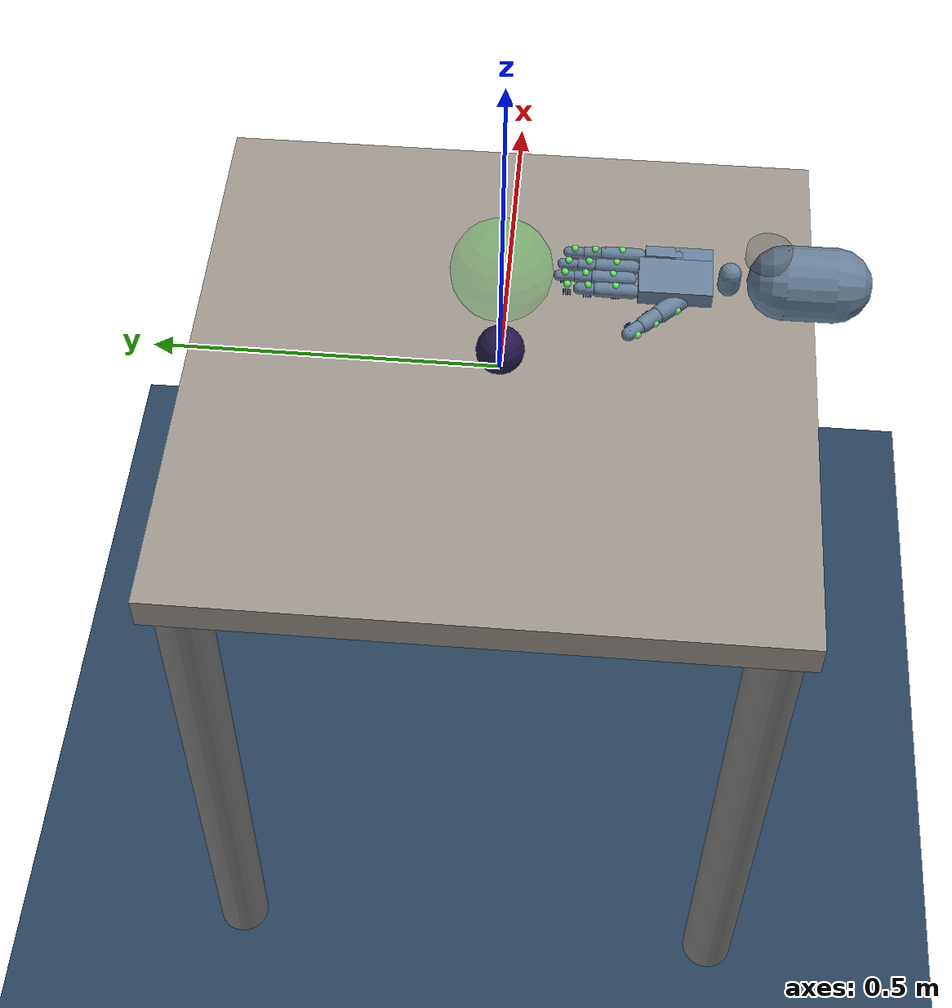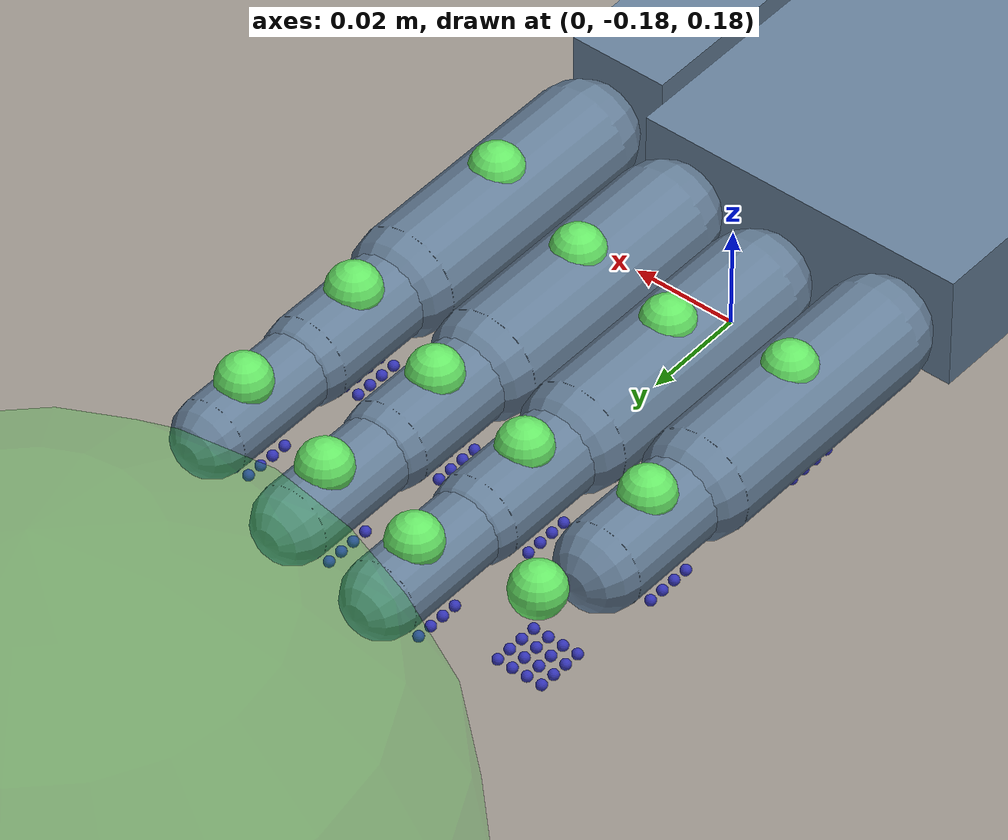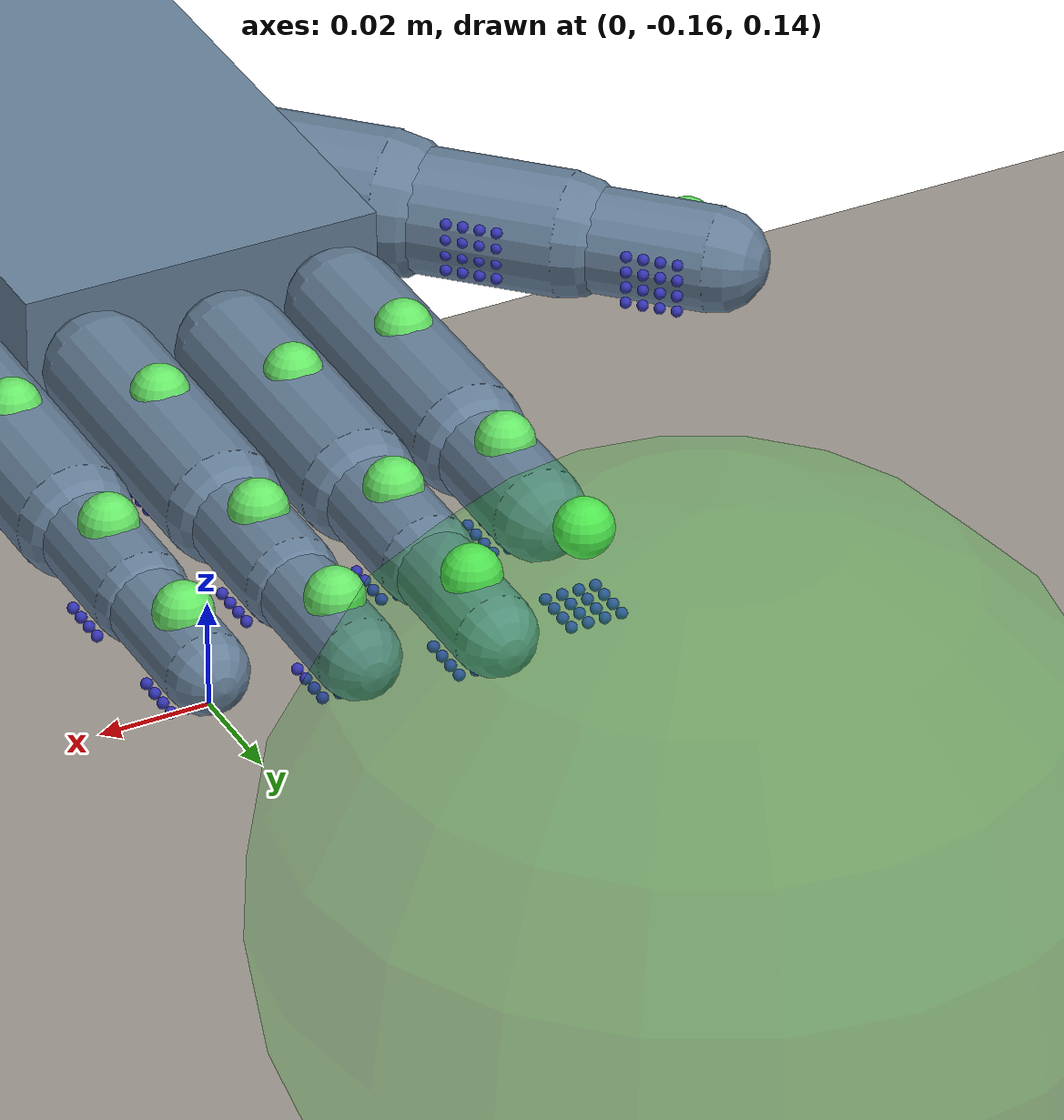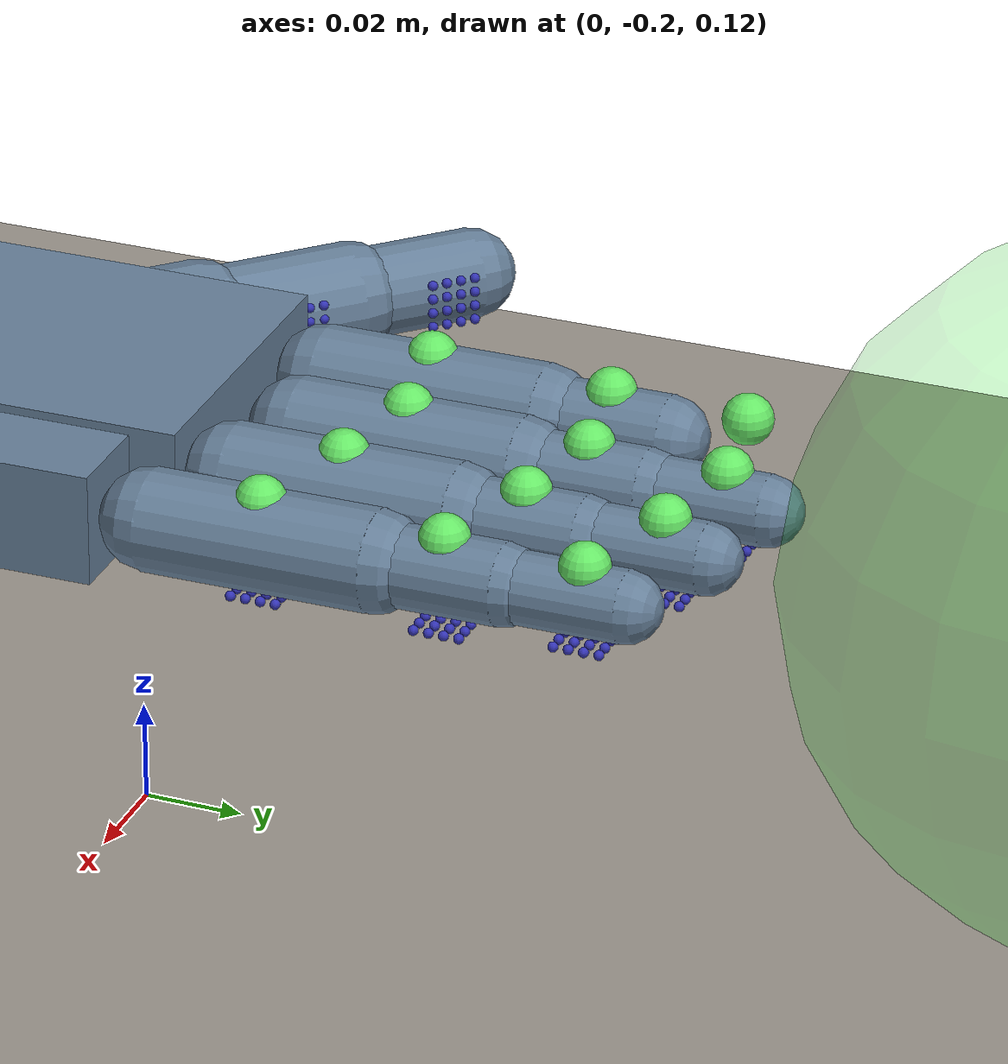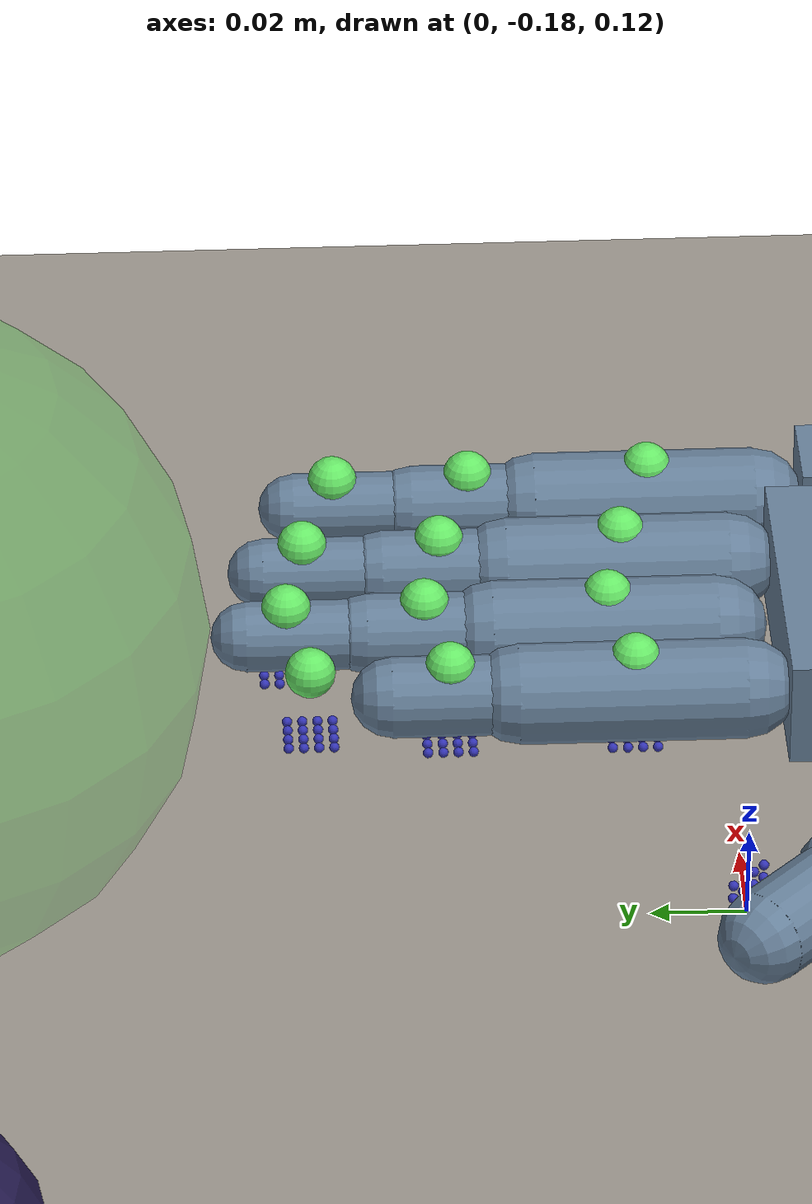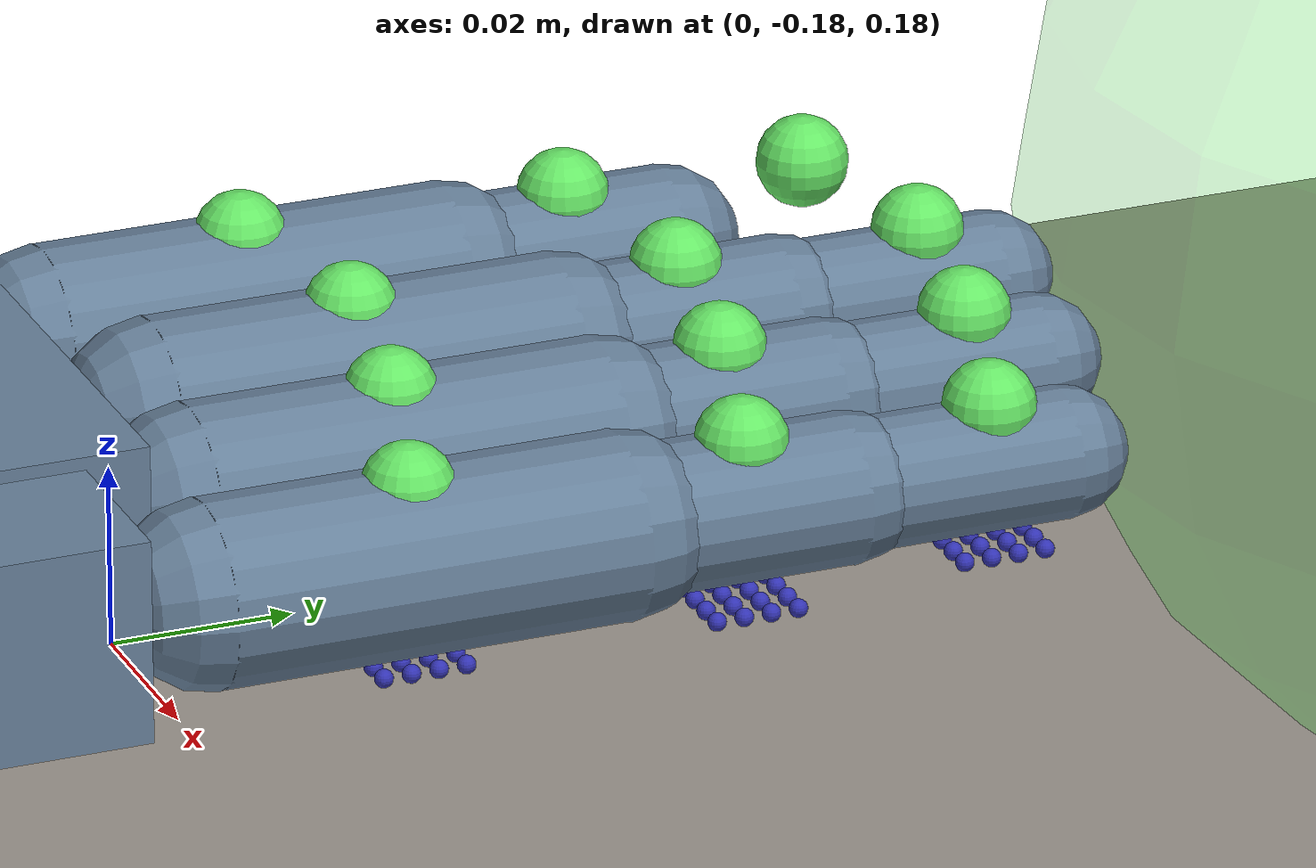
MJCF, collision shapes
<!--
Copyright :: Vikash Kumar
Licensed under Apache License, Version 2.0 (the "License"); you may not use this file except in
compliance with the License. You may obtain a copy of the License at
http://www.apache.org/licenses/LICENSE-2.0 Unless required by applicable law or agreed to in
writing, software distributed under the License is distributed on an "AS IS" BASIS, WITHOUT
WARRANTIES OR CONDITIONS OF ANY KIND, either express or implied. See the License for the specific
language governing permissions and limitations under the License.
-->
<mujoco model='ADROIT-relocate(v1.5)'>

    <!-- Added manually -->
    <visual>
		<scale framelength="3" framewidth="0.25" />
	</visual>
    <!-- Added manually -->

    <!-- ======= WORLD ======= -->
    <worldbody>
        <light directional='false' diffuse='.7 .7 .7' specular='0.03 0.03 0.03' pos='-1 -1.0 4.0'
            dir='1 1.0 -4' />
        <geom name='ground' size="1.5 1.5 0.25" pos="0 0 -1" type="plane" contype="1"
            conaffinity="0" material="groundplane" />
        <camera name="fixed" pos="0 -0.7 0.7" quat="0.92388 0.382683 0 0" />
        <!-- Camera for the VIL paper -->
        <camera name="vil_camera" pos="0 -1.2 1.2" quat="0.92388 0.382683 0 0" />

        <!-- ======= TABLE ======= -->
        <body name="table">
            <!-- Plane has better contacts -->
            <geom size="0.45 0.45 0.025" pos="0 0 -0.025" type="box" material="tablecube" />
            <geom size="0.04 0.5" pos="0.4 0.4 -0.501" quat="0 1 0 0" type="cylinder" contype="0"
                conaffinity="0" />
            <geom size="0.04 0.5" pos="-0.4 0.4 -0.501" quat="0 1 0 0" type="cylinder" contype="0"
                conaffinity="0" />
            <geom size="0.04 0.5" pos="0.4 -0.4 -0.501" quat="0 1 0 0" type="cylinder" contype="0"
                conaffinity="0" />
            <geom size="0.04 0.5" pos="-0.4 -0.4 -0.501" quat="0 1 0 0" type="cylinder" contype="0"
                conaffinity="0" />
        </body>

        <!-- ======= MOCAP ======= -->
        <body name="vive_tracker" pos="0 -0.35 0.25" mocap="true">
            <inertial pos="0 0 0" mass="0.064" diaginertia="1.70667e-05 1.70667e-05 1.70667e-05" />
            <geom size="0.03 0.01" type="cylinder" contype="0" conaffinity="0" group="3"
                rgba="0.3 0.3 0.3 0.3" />
        </body>

        <!-- ======= HAND ======= -->
        <body name="forearm" pos="0 -0.7 0.2" euler="-1.57 0 3.14">
            <inertial pos="0.001 -0.002 0.29" quat="0.982037 -0.0160006 0 -0.188007" mass="4"
                diaginertia="0.01 0.01 0.0075" />
            <joint name="ARTx" pos="0 0 0" axis="1 0 0" type="slide" range="-0.25 0.25" damping="20" />
            <joint name="ARTy" pos="0 0 0" axis="0 1 0" type="slide" range="0 0.2" damping="20" />
            <joint name="ARTz" pos="0 0 0" axis="0 0 1" type="slide" range="-0.3 0.5" damping="20" />
            <joint name="ARRx" pos="0 0 0" axis="1 0 0" range="-.75 .75" damping="20" />
            <joint name="ARRy" pos="0 0 0" axis="0 1 0" range="-.75 .75" damping="20" />
            <joint name="ARRz" pos="0 0 0" axis="0 0 1" range="-.75 .75" damping="20" />
            <geom name="V_forearm" class="D_Vizual" pos="0 -.01 .181" euler="0 0 -1.57"
                mesh="forearm_simple" />
            <geom name="C_forearm1" class="DC_Hand" size="0.05 0.033" pos="0 0 0.29" type="capsule"
                rgba="0.4 0.5 0.6 0.1" />
            <!-- ======= Adroit ======= -->
            <include file="DAPG_Adroit_v1.xml" />
        </body>

        <!-- ======= DESTINATION ======= -->
        <site name="target" pos="-0.007 0.0 0.2" size="0.07" rgba="0 1 0 0.125" />

        <!-- ======= OBJECT ======= -->
        <body name="Object" pos="-0.00 0.0 0.035" user="1001 0 2003 27 0 0 0.06 0 0">
            <inertial pos="0 0 0" mass="0.179594" diaginertia="8.80012e-05 8.80012e-05 8.80012e-05" />
            <joint name="OBJTx" pos="0 0 0" axis="1 0 0" type="slide" limited="false" damping="0" />
            <joint name="OBJTy" pos="0 0 0" axis="0 1 0" type="slide" limited="false" damping="0" />
            <joint name="OBJTz" pos="0 0 0" axis="0 0 1" type="slide" limited="false" damping="0" />
            <joint name="OBJRx" pos="0 0 0" axis="1 0 0" limited="false" damping="0" />
            <joint name="OBJRy" pos="0 0 0" axis="0 1 0" limited="false" damping="0" />
            <joint name="OBJRz" pos="0 0 0" axis="0 0 1" limited="false" damping="0" />
            <geom name="sphere" size="0.035" condim="4" material="MatWoodB" solref="0.02 1" solimp="0 0.95 0.0001" />
        </body>

        <!-- ======= DEBUG ======= -->
        <!-- Added manually -->
        <include file="DAPG_Adroit_debug.xml" />
        <!-- Added manually -->
    </worldbody>

    <actuator>
        <general name="A_ARTx" joint="ARTx" ctrlrange="-0.25 0.25" biastype="affine"
            gainprm="500 0 0" biasprm="0 -200 0" />
        <general name="A_ARTy" joint="ARTy" ctrlrange="0.0 0.2" biastype="affine" gainprm="500 0 0"
            biasprm="0 -200 0" />
        <general name="A_ARTz" joint="ARTz" ctrlrange="-0.3 0.5" biastype="affine" gainprm="500 0 0"
            biasprm="0 -200 0" />
        <general name="A_ARRx" joint="ARRx" ctrlrange="-.75 .75" biastype="affine" gainprm="500 0 0"
            biasprm="0 -200 0" />
        <general name="A_ARRy" joint="ARRy" ctrlrange="-.75 .75" biastype="affine" gainprm="500 0 0"
            biasprm="0 -200 0" />
        <general name="A_ARRz" joint="ARRz" ctrlrange="-.75 .75" biastype="affine" gainprm="500 0 0"
            biasprm="0 -200 0" />
    </actuator>

    <include file='DAPG_assets.xml' />

</mujoco>

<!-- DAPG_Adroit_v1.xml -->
<mujocoinclude>
    <!-- ======= Wrist ======= -->
    <!-- Modified manually -->
    <body name="wrist" pos="0 0 0.396">
        <!-- Modified manually -->
        <inertial pos="0.003 0.000 0.016" quat="0.504 0.496 0.495 0.504" mass="0.3" diaginertia="0.001 0.001 0.001" />
        <joint name="WRJ1" type="hinge" pos="0 0 0" axis="0 1 0" range="-0.524 0.175" damping=".5" armature=".005" user="1123" />
        <geom class="D_Vizual" name="V_wrist" mesh="wrist" />
        <geom class="DC_Hand" name="C_wrist" type="capsule" pos="0 0 0" quat=".707 .707 0 0" size=".015 .01" rgba=".4 .5 .6 .1" />

        <!-- ======= Palm ======= -->
        <body name="palm" pos="0 0 0.034">
            <inertial pos="0.006 -0.000 0.036" quat="0.716 0.044 0.075 0.693" mass="0.3" diaginertia="0.001 0.001 0.001" />
            <joint name="WRJ0" type="hinge" pos="0 0 0" axis="1 0 0" range="-0.785 0.611" damping=".5" armature=".005" user="1122" />
            <geom class="D_Vizual" name="V_palm" mesh="palm" />
            <geom class="DC_Hand" name="C_palm0" type="box" pos="0.011 0 0.038" size=".032 .0111 .049" rgba=".4 .5 .6 .1" />
            <geom class="DC_Hand" name="C_palm1" type="box" pos="-.032 0 0.014" size=".011 .0111 .025" rgba=".4 .5 .6 .1" />

            <!-- Added manually -->
            <site name="S_grasp" type="sphere" rgba="0 0 0 0" size="0.01" pos=".007 -.05 0.07"
                quat="0.0087 -0.6 -0.0034 -0.81  " />
            <site class="D_Touch" name="Tch_ffmetacarpal" size="0.009 0.004 0.006"
                pos="0.033 -.008 .078" />
            <site class="D_Touch" name="Tch_mfmetacarpal" size="0.009 0.004 0.014"
                pos="0.011 -.008 .074" />
            <site class="D_Touch" name="Tch_rfmetacarpal" size="0.009 0.004 0.016"
                pos="-0.011 -.008 .068" />
            <site class="D_Touch" name="Tch_thmetacarpal" size="0.008 0.004 0.015"
                pos="0.006 -.008 .042" euler="0 0.57 0" />
            <site class="D_Touch" name="Tch_palm" size="0.012 0.004 0.016" pos="-0.017 -.008 .024"
                euler="0 -1 0" />
            <!-- Added manually -->

            <!-- ======= First Finger ======= -->
            <body name="ffknuckle" pos="0.033 0 0.095">
                <inertial pos="-0.000 0.000 0.000" quat="0.520 0.854 0.006 -0.003" mass="0.008" diaginertia="0.00001 0.00001 0.00001" />
                <joint name="FFJ3" type="hinge" pos="0 0 0" axis="0 1 0" range="-0.436 0.436" user="1103" />
                <geom class="D_Vizual" name="V_ffknuckle" mesh="knuckle" />
                <!--Proximal-->
                <body name="ffproximal" pos="0 0 0">
                    <inertial pos="0.000 0.000 0.023" quat="0.707 -0.004 0.004 0.707" mass="0.014" diaginertia="0.00001 0.00001 0.00001" />
                    <joint name="FFJ2" type="hinge" pos="0 0 0" axis="1 0 0" range="0 1.571" user="1102" />
                    <geom class="D_Vizual" name="V_ffproximal" mesh="F3" />
                    <geom class="DC_Hand" name="C_ffproximal" type="capsule" pos="0 0 .0225" size=".01 .0225" contype="1" conaffinity="2" />
                    <site class="D_Touch" name="Tch_ffproximal" size="0.010 0.006 0.013" pos="0 -.004 .0225" />
                    <site name="ffproximal_touch" pos="0 0.008 0.022" euler="-1.571 0 0" />
                    <!--middle-->
                    <body name="ffmiddle" pos="0 0 0.045">
                        <inertial pos="-0.000 -0.000 0.011" quat="0.707 0.000 -0.000 0.707" mass="0.012" diaginertia="0.00001 0.00001 0.00001" />
                        <joint name="FFJ1" type="hinge" pos="0 0 0" axis="1 0 0" range="0 1.571" user="1101" />
                        <geom class="D_Vizual" name="V_ffmiddle" mesh="F2" />
                        <geom class="DC_Hand" name="C_ffmiddle" type="capsule" pos="0 0 .0125" size=".00805 .0125" contype="1" conaffinity="2" />
                        <site class="D_Touch" name="Tch_ffmiddle" size="0.009 0.005 0.013" pos="0 -.004 .0125" />
                        <site name="ffmiddle_touch" pos="0 0.007 0.0135" euler="-1.571 0 0" />
                        <!--distal-->
                        <body name="ffdistal" pos="0 0 0.025">
                            <inertial pos="0 -0.000 0.015" quat="0.707 -0.003 0.003 0.707" mass="0.010" diaginertia="0.00001 0.00001 0.00001" />
                            <joint name="FFJ0" type="hinge" pos="0 0 0" axis="1 0 0" range="0 1.571" user="1100" />
                            <geom class="D_Vizual" name="V_ffdistal" pos="0 0 .001" mesh="F1" />
                            <site name="S_fftip" pos="0.000 0 0.026" group="3" />
                            <site class="D_Touch" name="Tch_fftip" size="0.009 0.004 0.013" pos="0 -.004 .018" />
                            <site name="ffdistal_touch" pos="0 0.0065 0.016" euler="-1.571 0 0" />
                            <body name="ffdistal_panel_base" pos="0.0 -0.0085 0.016" quat="0.70710678 -0.70710678 0.0 0.0">
                                <body name="ffdistal_T_r0c0" pos="-0.0045000000000000005 -0.0045000000000000005 0.0">
                                    <geom type="sphere" size="0.001" rgba="0.2 0.2 0.7 0.5" contype="1" conaffinity="2" class="DC_Taxel" />
                                    <inertial mass="1e-05" diaginertia="1e-06 1e-06 1e-06" pos="0 0 0" />
                                    <joint type="slide" stiffness="1000.0" damping="0.0001" axis="0 0 1" name="ffdistal_J_r0c0" range="-0.001 0.001" />
                                    <site name="ffdistal_S_r0c0" pos="0 0 0" class="D_Array" />
                                </body>
                                <body name="ffdistal_T_r0c1" pos="-0.0015000000000000005 -0.0045000000000000005 0.0">
                                    <geom type="sphere" size="0.001" rgba="0.2 0.2 0.7 0.5" contype="1" conaffinity="2" class="DC_Taxel" />
                                    <inertial mass="1e-05" diaginertia="1e-06 1e-06 1e-06" pos="0 0 0" />
                                    <joint type="slide" stiffness="1000.0" damping="0.0001" axis="0 0 1" name="ffdistal_J_r0c1" range="-0.001 0.001" />
                                    <site name="ffdistal_S_r0c1" pos="0 0 0" class="D_Array" />
                                </body>
                                <body name="ffdistal_T_r0c2" pos="0.0014999999999999996 -0.0045000000000000005 0.0">
                                    <geom type="sphere" size="0.001" rgba="0.2 0.2 0.7 0.5" contype="1" conaffinity="2" class="DC_Taxel" />
                                    <inertial mass="1e-05" diaginertia="1e-06 1e-06 1e-06" pos="0 0 0" />
                                    <joint type="slide" stiffness="1000.0" damping="0.0001" axis="0 0 1" name="ffdistal_J_r0c2" range="-0.001 0.001" />
                                    <site name="ffdistal_S_r0c2" pos="0 0 0" class="D_Array" />
                                </body>
                                <body name="ffdistal_T_r0c3" pos="0.0045000000000000005 -0.0045000000000000005 0.0">
                                    <geom type="sphere" size="0.001" rgba="0.2 0.2 0.7 0.5" contype="1" conaffinity="2" class="DC_Taxel" />
                                    <inertial mass="1e-05" diaginertia="1e-06 1e-06 1e-06" pos="0 0 0" />
                                    <joint type="slide" stiffness="1000.0" damping="0.0001" axis="0 0 1" name="ffdistal_J_r0c3" range="-0.001 0.001" />
                                    <site name="ffdistal_S_r0c3" pos="0 0 0" class="D_Array" />
                                </body>
                                <body name="ffdistal_T_r1c0" pos="-0.0045000000000000005 -0.0015000000000000005 0.0">
                                    <geom type="sphere" size="0.001" rgba="0.2 0.2 0.7 0.5" contype="1" conaffinity="2" class="DC_Taxel" />
                                    <inertial mass="1e-05" diaginertia="1e-06 1e-06 1e-06" pos="0 0 0" />
                                    <joint type="slide" stiffness="1000.0" damping="0.0001" axis="0 0 1" name="ffdistal_J_r1c0" range="-0.001 0.001" />
                                    <site name="ffdistal_S_r1c0" pos="0 0 0" class="D_Array" />
                                </body>
                                <body name="ffdistal_T_r1c1" pos="-0.0015000000000000005 -0.0015000000000000005 0.0">
                                    <geom type="sphere" size="0.001" rgba="0.2 0.2 0.7 0.5" contype="1" conaffinity="2" class="DC_Taxel" />
                                    <inertial mass="1e-05" diaginertia="1e-06 1e-06 1e-06" pos="0 0 0" />
                                    <joint type="slide" stiffness="1000.0" damping="0.0001" axis="0 0 1" name="ffdistal_J_r1c1" range="-0.001 0.001" />
                                    <site name="ffdistal_S_r1c1" pos="0 0 0" class="D_Array" />
                                </body>
                                <body name="ffdistal_T_r1c2" pos="0.0014999999999999996 -0.0015000000000000005 0.0">
                                    <geom type="sphere" size="0.001" rgba="0.2 0.2 0.7 0.5" contype="1" conaffinity="2" class="DC_Taxel" />
                                    <inertial mass="1e-05" diaginertia="1e-06 1e-06 1e-06" pos="0 0 0" />
                                    <joint type="slide" stiffness="1000.0" damping="0.0001" axis="0 0 1" name="ffdistal_J_r1c2" range="-0.001 0.001" />
                                    <site name="ffdistal_S_r1c2" pos="0 0 0" class="D_Array" />
                                </body>
                                <body name="ffdistal_T_r1c3" pos="0.0045000000000000005 -0.0015000000000000005 0.0">
                                    <geom type="sphere" size="0.001" rgba="0.2 0.2 0.7 0.5" contype="1" conaffinity="2" class="DC_Taxel" />
                                    <inertial mass="1e-05" diaginertia="1e-06 1e-06 1e-06" pos="0 0 0" />
                                    <joint type="slide" stiffness="1000.0" damping="0.0001" axis="0 0 1" name="ffdistal_J_r1c3" range="-0.001 0.001" />
                                    <site name="ffdistal_S_r1c3" pos="0 0 0" class="D_Array" />
                                </body>
                                <body name="ffdistal_T_r2c0" pos="-0.0045000000000000005 0.0014999999999999996 0.0">
                                    <geom type="sphere" size="0.001" rgba="0.2 0.2 0.7 0.5" contype="1" conaffinity="2" class="DC_Taxel" />
                                    <inertial mass="1e-05" diaginertia="1e-06 1e-06 1e-06" pos="0 0 0" />
                                    <joint type="slide" stiffness="1000.0" damping="0.0001" axis="0 0 1" name="ffdistal_J_r2c0" range="-0.001 0.001" />
                                    <site name="ffdistal_S_r2c0" pos="0 0 0" class="D_Array" />
                                </body>
                                <body name="ffdistal_T_r2c1" pos="-0.0015000000000000005 0.0014999999999999996 0.0">
                                    <geom type="sphere" size="0.001" rgba="0.2 0.2 0.7 0.5" contype="1" conaffinity="2" class="DC_Taxel" />
                                    <inertial mass="1e-05" diaginertia="1e-06 1e-06 1e-06" pos="0 0 0" />
                                    <joint type="slide" stiffness="1000.0" damping="0.0001" axis="0 0 1" name="ffdistal_J_r2c1" range="-0.001 0.001" />
                                    <site name="ffdistal_S_r2c1" pos="0 0 0" class="D_Array" />
                                </body>
                                <body name="ffdistal_T_r2c2" pos="0.0014999999999999996 0.0014999999999999996 0.0">
                                    <geom type="sphere" size="0.001" rgba="0.2 0.2 0.7 0.5" contype="1" conaffinity="2" class="DC_Taxel" />
                                    <inertial mass="1e-05" diaginertia="1e-06 1e-06 1e-06" pos="0 0 0" />
                                    <joint type="slide" stiffness="1000.0" damping="0.0001" axis="0 0 1" name="ffdistal_J_r2c2" range="-0.001 0.001" />
                                    <site name="ffdistal_S_r2c2" pos="0 0 0" class="D_Array" />
                                </body>
                                <body name="ffdistal_T_r2c3" pos="0.0045000000000000005 0.0014999999999999996 0.0">
                                    <geom type="sphere" size="0.001" rgba="0.2 0.2 0.7 0.5" contype="1" conaffinity="2" class="DC_Taxel" />
                                    <inertial mass="1e-05" diaginertia="1e-06 1e-06 1e-06" pos="0 0 0" />
                                    <joint type="slide" stiffness="1000.0" damping="0.0001" axis="0 0 1" name="ffdistal_J_r2c3" range="-0.001 0.001" />
                                    <site name="ffdistal_S_r2c3" pos="0 0 0" class="D_Array" />
                                </body>
                                <body name="ffdistal_T_r3c0" pos="-0.0045000000000000005 0.0045000000000000005 0.0">
                                    <geom type="sphere" size="0.001" rgba="0.2 0.2 0.7 0.5" contype="1" conaffinity="2" class="DC_Taxel" />
                                    <inertial mass="1e-05" diaginertia="1e-06 1e-06 1e-06" pos="0 0 0" />
                                    <joint type="slide" stiffness="1000.0" damping="0.0001" axis="0 0 1" name="ffdistal_J_r3c0" range="-0.001 0.001" />
                                    <site name="ffdistal_S_r3c0" pos="0 0 0" class="D_Array" />
                                </body>
                                <body name="ffdistal_T_r3c1" pos="-0.0015000000000000005 0.0045000000000000005 0.0">
                                    <geom type="sphere" size="0.001" rgba="0.2 0.2 0.7 0.5" contype="1" conaffinity="2" class="DC_Taxel" />
                                    <inertial mass="1e-05" diaginertia="1e-06 1e-06 1e-06" pos="0 0 0" />
                                    <joint type="slide" stiffness="1000.0" damping="0.0001" axis="0 0 1" name="ffdistal_J_r3c1" range="-0.001 0.001" />
                                    <site name="ffdistal_S_r3c1" pos="0 0 0" class="D_Array" />
                                </body>
                                <body name="ffdistal_T_r3c2" pos="0.0014999999999999996 0.0045000000000000005 0.0">
                                    <geom type="sphere" size="0.001" rgba="0.2 0.2 0.7 0.5" contype="1" conaffinity="2" class="DC_Taxel" />
                                    <inertial mass="1e-05" diaginertia="1e-06 1e-06 1e-06" pos="0 0 0" />
                                    <joint type="slide" stiffness="1000.0" damping="0.0001" axis="0 0 1" name="ffdistal_J_r3c2" range="-0.001 0.001" />
                                    <site name="ffdistal_S_r3c2" pos="0 0 0" class="D_Array" />
                                </body>
                                <body name="ffdistal_T_r3c3" pos="0.0045000000000000005 0.0045000000000000005 0.0">
                                    <geom type="sphere" size="0.001" rgba="0.2 0.2 0.7 0.5" contype="1" conaffinity="2" class="DC_Taxel" />
                                    <inertial mass="1e-05" diaginertia="1e-06 1e-06 1e-06" pos="0 0 0" />
                                    <joint type="slide" stiffness="1000.0" damping="0.0001" axis="0 0 1" name="ffdistal_J_r3c3" range="-0.001 0.001" />
                                    <site name="ffdistal_S_r3c3" pos="0 0 0" class="D_Array" />
                                </body>
                            </body>
                        </body>
                        <body name="ffmiddle_panel_base" pos="0.0 -0.010500000000000002 0.0135" quat="0.70710678 -0.70710678 0.0 0.0">
                            <body name="ffmiddle_T_r0c0" pos="-0.0045000000000000005 -0.0045000000000000005 0.0">
                                <geom type="sphere" size="0.001" rgba="0.2 0.2 0.7 0.5" contype="1" conaffinity="2" class="DC_Taxel" />
                                <inertial mass="1e-05" diaginertia="1e-06 1e-06 1e-06" pos="0 0 0" />
                                <joint type="slide" stiffness="1000.0" damping="0.0001" axis="0 0 1" name="ffmiddle_J_r0c0" range="-0.001 0.001" />
                                <site name="ffmiddle_S_r0c0" pos="0 0 0" class="D_Array" />
                            </body>
                            <body name="ffmiddle_T_r0c1" pos="-0.0015000000000000005 -0.0045000000000000005 0.0">
                                <geom type="sphere" size="0.001" rgba="0.2 0.2 0.7 0.5" contype="1" conaffinity="2" class="DC_Taxel" />
                                <inertial mass="1e-05" diaginertia="1e-06 1e-06 1e-06" pos="0 0 0" />
                                <joint type="slide" stiffness="1000.0" damping="0.0001" axis="0 0 1" name="ffmiddle_J_r0c1" range="-0.001 0.001" />
                                <site name="ffmiddle_S_r0c1" pos="0 0 0" class="D_Array" />
                            </body>
                            <body name="ffmiddle_T_r0c2" pos="0.0014999999999999996 -0.0045000000000000005 0.0">
                                <geom type="sphere" size="0.001" rgba="0.2 0.2 0.7 0.5" contype="1" conaffinity="2" class="DC_Taxel" />
                                <inertial mass="1e-05" diaginertia="1e-06 1e-06 1e-06" pos="0 0 0" />
                                <joint type="slide" stiffness="1000.0" damping="0.0001" axis="0 0 1" name="ffmiddle_J_r0c2" range="-0.001 0.001" />
                                <site name="ffmiddle_S_r0c2" pos="0 0 0" class="D_Array" />
                            </body>
                            <body name="ffmiddle_T_r0c3" pos="0.0045000000000000005 -0.0045000000000000005 0.0">
                                <geom type="sphere" size="0.001" rgba="0.2 0.2 0.7 0.5" contype="1" conaffinity="2" class="DC_Taxel" />
                                <inertial mass="1e-05" diaginertia="1e-06 1e-06 1e-06" pos="0 0 0" />
                                <joint type="slide" stiffness="1000.0" damping="0.0001" axis="0 0 1" name="ffmiddle_J_r0c3" range="-0.001 0.001" />
                                <site name="ffmiddle_S_r0c3" pos="0 0 0" class="D_Array" />
                            </body>
                            <body name="ffmiddle_T_r1c0" pos="-0.0045000000000000005 -0.0015000000000000005 0.0">
                                <geom type="sphere" size="0.001" rgba="0.2 0.2 0.7 0.5" contype="1" conaffinity="2" class="DC_Taxel" />
                                <inertial mass="1e-05" diaginertia="1e-06 1e-06 1e-06" pos="0 0 0" />
                                <joint type="slide" stiffness="1000.0" damping="0.0001" axis="0 0 1" name="ffmiddle_J_r1c0" range="-0.001 0.001" />
                                <site name="ffmiddle_S_r1c0" pos="0 0 0" class="D_Array" />
                            </body>
                            <body name="ffmiddle_T_r1c1" pos="-0.0015000000000000005 -0.0015000000000000005 0.0">
                                <geom type="sphere" size="0.001" rgba="0.2 0.2 0.7 0.5" contype="1" conaffinity="2" class="DC_Taxel" />
                                <inertial mass="1e-05" diaginertia="1e-06 1e-06 1e-06" pos="0 0 0" />
                                <joint type="slide" stiffness="1000.0" damping="0.0001" axis="0 0 1" name="ffmiddle_J_r1c1" range="-0.001 0.001" />
                                <site name="ffmiddle_S_r1c1" pos="0 0 0" class="D_Array" />
                            </body>
                            <body name="ffmiddle_T_r1c2" pos="0.0014999999999999996 -0.0015000000000000005 0.0">
                                <geom type="sphere" size="0.001" rgba="0.2 0.2 0.7 0.5" contype="1" conaffinity="2" class="DC_Taxel" />
                                <inertial mass="1e-05" diaginertia="1e-06 1e-06 1e-06" pos="0 0 0" />
                                <joint type="slide" stiffness="1000.0" damping="0.0001" axis="0 0 1" name="ffmiddle_J_r1c2" range="-0.001 0.001" />
                                <site name="ffmiddle_S_r1c2" pos="0 0 0" class="D_Array" />
                            </body>
                            <body name="ffmiddle_T_r1c3" pos="0.0045000000000000005 -0.0015000000000000005 0.0">
                                <geom type="sphere" size="0.001" rgba="0.2 0.2 0.7 0.5" contype="1" conaffinity="2" class="DC_Taxel" />
                                <inertial mass="1e-05" diaginertia="1e-06 1e-06 1e-06" pos="0 0 0" />
                                <joint type="slide" stiffness="1000.0" damping="0.0001" axis="0 0 1" name="ffmiddle_J_r1c3" range="-0.001 0.001" />
                                <site name="ffmiddle_S_r1c3" pos="0 0 0" class="D_Array" />
                            </body>
                            <body name="ffmiddle_T_r2c0" pos="-0.0045000000000000005 0.0014999999999999996 0.0">
                                <geom type="sphere" size="0.001" rgba="0.2 0.2 0.7 0.5" contype="1" conaffinity="2" class="DC_Taxel" />
                                <inertial mass="1e-05" diaginertia="1e-06 1e-06 1e-06" pos="0 0 0" />
                                <joint type="slide" stiffness="1000.0" damping="0.0001" axis="0 0 1" name="ffmiddle_J_r2c0" range="-0.001 0.001" />
                                <site name="ffmiddle_S_r2c0" pos="0 0 0" class="D_Array" />
                            </body>
                            <body name="ffmiddle_T_r2c1" pos="-0.0015000000000000005 0.0014999999999999996 0.0">
                                <geom type="sphere" size="0.001" rgba="0.2 0.2 0.7 0.5" contype="1" conaffinity="2" class="DC_Taxel" />
                                <inertial mass="1e-05" diaginertia="1e-06 1e-06 1e-06" pos="0 0 0" />
                                <joint type="slide" stiffness="1000.0" damping="0.0001" axis="0 0 1" name="ffmiddle_J_r2c1" range="-0.001 0.001" />
                                <site name="ffmiddle_S_r2c1" pos="0 0 0" class="D_Array" />
                            </body>
                            <body name="ffmiddle_T_r2c2" pos="0.0014999999999999996 0.0014999999999999996 0.0">
                                <geom type="sphere" size="0.001" rgba="0.2 0.2 0.7 0.5" contype="1" conaffinity="2" class="DC_Taxel" />
                                <inertial mass="1e-05" diaginertia="1e-06 1e-06 1e-06" pos="0 0 0" />
                                <joint type="slide" stiffness="1000.0" damping="0.0001" axis="0 0 1" name="ffmiddle_J_r2c2" range="-0.001 0.001" />
                                <site name="ffmiddle_S_r2c2" pos="0 0 0" class="D_Array" />
                            </body>
                            <body name="ffmiddle_T_r2c3" pos="0.0045000000000000005 0.0014999999999999996 0.0">
                                <geom type="sphere" size="0.001" rgba="0.2 0.2 0.7 0.5" contype="1" conaffinity="2" class="DC_Taxel" />
                                <inertial mass="1e-05" diaginertia="1e-06 1e-06 1e-06" pos="0 0 0" />
                                <joint type="slide" stiffness="1000.0" damping="0.0001" axis="0 0 1" name="ffmiddle_J_r2c3" range="-0.001 0.001" />
                                <site name="ffmiddle_S_r2c3" pos="0 0 0" class="D_Array" />
                            </body>
                            <body name="ffmiddle_T_r3c0" pos="-0.0045000000000000005 0.0045000000000000005 0.0">
                                <geom type="sphere" size="0.001" rgba="0.2 0.2 0.7 0.5" contype="1" conaffinity="2" class="DC_Taxel" />
                                <inertial mass="1e-05" diaginertia="1e-06 1e-06 1e-06" pos="0 0 0" />
                                <joint type="slide" stiffness="1000.0" damping="0.0001" axis="0 0 1" name="ffmiddle_J_r3c0" range="-0.001 0.001" />
                                <site name="ffmiddle_S_r3c0" pos="0 0 0" class="D_Array" />
                            </body>
                            <body name="ffmiddle_T_r3c1" pos="-0.0015000000000000005 0.0045000000000000005 0.0">
                                <geom type="sphere" size="0.001" rgba="0.2 0.2 0.7 0.5" contype="1" conaffinity="2" class="DC_Taxel" />
                                <inertial mass="1e-05" diaginertia="1e-06 1e-06 1e-06" pos="0 0 0" />
                                <joint type="slide" stiffness="1000.0" damping="0.0001" axis="0 0 1" name="ffmiddle_J_r3c1" range="-0.001 0.001" />
                                <site name="ffmiddle_S_r3c1" pos="0 0 0" class="D_Array" />
                            </body>
                            <body name="ffmiddle_T_r3c2" pos="0.0014999999999999996 0.0045000000000000005 0.0">
                                <geom type="sphere" size="0.001" rgba="0.2 0.2 0.7 0.5" contype="1" conaffinity="2" class="DC_Taxel" />
                                <inertial mass="1e-05" diaginertia="1e-06 1e-06 1e-06" pos="0 0 0" />
                                <joint type="slide" stiffness="1000.0" damping="0.0001" axis="0 0 1" name="ffmiddle_J_r3c2" range="-0.001 0.001" />
                                <site name="ffmiddle_S_r3c2" pos="0 0 0" class="D_Array" />
                            </body>
                            <body name="ffmiddle_T_r3c3" pos="0.0045000000000000005 0.0045000000000000005 0.0">
                                <geom type="sphere" size="0.001" rgba="0.2 0.2 0.7 0.5" contype="1" conaffinity="2" class="DC_Taxel" />
                                <inertial mass="1e-05" diaginertia="1e-06 1e-06 1e-06" pos="0 0 0" />
                                <joint type="slide" stiffness="1000.0" damping="0.0001" axis="0 0 1" name="ffmiddle_J_r3c3" range="-0.001 0.001" />
                                <site name="ffmiddle_S_r3c3" pos="0 0 0" class="D_Array" />
                            </body>
                        </body>
                    </body>
                    <body name="ffproximal_panel_base" pos="0.0 -0.010500000000000002 0.022" quat="0.70710678 -0.70710678 0.0 0.0">
                        <body name="ffproximal_T_r0c0" pos="-0.0045000000000000005 -0.0045000000000000005 0.0">
                            <geom type="sphere" size="0.001" rgba="0.2 0.2 0.7 0.5" contype="1" conaffinity="2" class="DC_Taxel" />
                            <inertial mass="1e-05" diaginertia="1e-06 1e-06 1e-06" pos="0 0 0" />
                            <joint type="slide" stiffness="1000.0" damping="0.0001" axis="0 0 1" name="ffproximal_J_r0c0" range="-0.001 0.001" />
                            <site name="ffproximal_S_r0c0" pos="0 0 0" class="D_Array" />
                        </body>
                        <body name="ffproximal_T_r0c1" pos="-0.0015000000000000005 -0.0045000000000000005 0.0">
                            <geom type="sphere" size="0.001" rgba="0.2 0.2 0.7 0.5" contype="1" conaffinity="2" class="DC_Taxel" />
                            <inertial mass="1e-05" diaginertia="1e-06 1e-06 1e-06" pos="0 0 0" />
                            <joint type="slide" stiffness="1000.0" damping="0.0001" axis="0 0 1" name="ffproximal_J_r0c1" range="-0.001 0.001" />
                            <site name="ffproximal_S_r0c1" pos="0 0 0" class="D_Array" />
                        </body>
                        <body name="ffproximal_T_r0c2" pos="0.0014999999999999996 -0.0045000000000000005 0.0">
                            <geom type="sphere" size="0.001" rgba="0.2 0.2 0.7 0.5" contype="1" conaffinity="2" class="DC_Taxel" />
                            <inertial mass="1e-05" diaginertia="1e-06 1e-06 1e-06" pos="0 0 0" />
                            <joint type="slide" stiffness="1000.0" damping="0.0001" axis="0 0 1" name="ffproximal_J_r0c2" range="-0.001 0.001" />
                            <site name="ffproximal_S_r0c2" pos="0 0 0" class="D_Array" />
                        </body>
                        <body name="ffproximal_T_r0c3" pos="0.0045000000000000005 -0.0045000000000000005 0.0">
                            <geom type="sphere" size="0.001" rgba="0.2 0.2 0.7 0.5" contype="1" conaffinity="2" class="DC_Taxel" />
                            <inertial mass="1e-05" diaginertia="1e-06 1e-06 1e-06" pos="0 0 0" />
                            <joint type="slide" stiffness="1000.0" damping="0.0001" axis="0 0 1" name="ffproximal_J_r0c3" range="-0.001 0.001" />
                            <site name="ffproximal_S_r0c3" pos="0 0 0" class="D_Array" />
                        </body>
                        <body name="ffproximal_T_r1c0" pos="-0.0045000000000000005 -0.0015000000000000005 0.0">
                            <geom type="sphere" size="0.001" rgba="0.2 0.2 0.7 0.5" contype="1" conaffinity="2" class="DC_Taxel" />
                            <inertial mass="1e-05" diaginertia="1e-06 1e-06 1e-06" pos="0 0 0" />
                            <joint type="slide" stiffness="1000.0" damping="0.0001" axis="0 0 1" name="ffproximal_J_r1c0" range="-0.001 0.001" />
                            <site name="ffproximal_S_r1c0" pos="0 0 0" class="D_Array" />
                        </body>
                        <body name="ffproximal_T_r1c1" pos="-0.0015000000000000005 -0.0015000000000000005 0.0">
                            <geom type="sphere" size="0.001" rgba="0.2 0.2 0.7 0.5" contype="1" conaffinity="2" class="DC_Taxel" />
                            <inertial mass="1e-05" diaginertia="1e-06 1e-06 1e-06" pos="0 0 0" />
                            <joint type="slide" stiffness="1000.0" damping="0.0001" axis="0 0 1" name="ffproximal_J_r1c1" range="-0.001 0.001" />
                            <site name="ffproximal_S_r1c1" pos="0 0 0" class="D_Array" />
                        </body>
                        <body name="ffproximal_T_r1c2" pos="0.0014999999999999996 -0.0015000000000000005 0.0">
                            <geom type="sphere" size="0.001" rgba="0.2 0.2 0.7 0.5" contype="1" conaffinity="2" class="DC_Taxel" />
                            <inertial mass="1e-05" diaginertia="1e-06 1e-06 1e-06" pos="0 0 0" />
                            <joint type="slide" stiffness="1000.0" damping="0.0001" axis="0 0 1" name="ffproximal_J_r1c2" range="-0.001 0.001" />
                            <site name="ffproximal_S_r1c2" pos="0 0 0" class="D_Array" />
                        </body>
                        <body name="ffproximal_T_r1c3" pos="0.0045000000000000005 -0.0015000000000000005 0.0">
                            <geom type="sphere" size="0.001" rgba="0.2 0.2 0.7 0.5" contype="1" conaffinity="2" class="DC_Taxel" />
                            <inertial mass="1e-05" diaginertia="1e-06 1e-06 1e-06" pos="0 0 0" />
                            <joint type="slide" stiffness="1000.0" damping="0.0001" axis="0 0 1" name="ffproximal_J_r1c3" range="-0.001 0.001" />
                            <site name="ffproximal_S_r1c3" pos="0 0 0" class="D_Array" />
                        </body>
                        <body name="ffproximal_T_r2c0" pos="-0.0045000000000000005 0.0014999999999999996 0.0">
                            <geom type="sphere" size="0.001" rgba="0.2 0.2 0.7 0.5" contype="1" conaffinity="2" class="DC_Taxel" />
                            <inertial mass="1e-05" diaginertia="1e-06 1e-06 1e-06" pos="0 0 0" />
                            <joint type="slide" stiffness="1000.0" damping="0.0001" axis="0 0 1" name="ffproximal_J_r2c0" range="-0.001 0.001" />
                            <site name="ffproximal_S_r2c0" pos="0 0 0" class="D_Array" />
                        </body>
                        <body name="ffproximal_T_r2c1" pos="-0.0015000000000000005 0.0014999999999999996 0.0">
                            <geom type="sphere" size="0.001" rgba="0.2 0.2 0.7 0.5" contype="1" conaffinity="2" class="DC_Taxel" />
                            <inertial mass="1e-05" diaginertia="1e-06 1e-06 1e-06" pos="0 0 0" />
                            <joint type="slide" stiffness="1000.0" damping="0.0001" axis="0 0 1" name="ffproximal_J_r2c1" range="-0.001 0.001" />
                            <site name="ffproximal_S_r2c1" pos="0 0 0" class="D_Array" />
                        </body>
                        <body name="ffproximal_T_r2c2" pos="0.0014999999999999996 0.0014999999999999996 0.0">
                            <geom type="sphere" size="0.001" rgba="0.2 0.2 0.7 0.5" contype="1" conaffinity="2" class="DC_Taxel" />
                            <inertial mass="1e-05" diaginertia="1e-06 1e-06 1e-06" pos="0 0 0" />
                            <joint type="slide" stiffness="1000.0" damping="0.0001" axis="0 0 1" name="ffproximal_J_r2c2" range="-0.001 0.001" />
                            <site name="ffproximal_S_r2c2" pos="0 0 0" class="D_Array" />
                        </body>
                        <body name="ffproximal_T_r2c3" pos="0.0045000000000000005 0.0014999999999999996 0.0">
                            <geom type="sphere" size="0.001" rgba="0.2 0.2 0.7 0.5" contype="1" conaffinity="2" class="DC_Taxel" />
                            <inertial mass="1e-05" diaginertia="1e-06 1e-06 1e-06" pos="0 0 0" />
                            <joint type="slide" stiffness="1000.0" damping="0.0001" axis="0 0 1" name="ffproximal_J_r2c3" range="-0.001 0.001" />
                            <site name="ffproximal_S_r2c3" pos="0 0 0" class="D_Array" />
                        </body>
                        <body name="ffproximal_T_r3c0" pos="-0.0045000000000000005 0.0045000000000000005 0.0">
                            <geom type="sphere" size="0.001" rgba="0.2 0.2 0.7 0.5" contype="1" conaffinity="2" class="DC_Taxel" />
                            <inertial mass="1e-05" diaginertia="1e-06 1e-06 1e-06" pos="0 0 0" />
                            <joint type="slide" stiffness="1000.0" damping="0.0001" axis="0 0 1" name="ffproximal_J_r3c0" range="-0.001 0.001" />
                            <site name="ffproximal_S_r3c0" pos="0 0 0" class="D_Array" />
                        </body>
                        <body name="ffproximal_T_r3c1" pos="-0.0015000000000000005 0.0045000000000000005 0.0">
                            <geom type="sphere" size="0.001" rgba="0.2 0.2 0.7 0.5" contype="1" conaffinity="2" class="DC_Taxel" />
                            <inertial mass="1e-05" diaginertia="1e-06 1e-06 1e-06" pos="0 0 0" />
                            <joint type="slide" stiffness="1000.0" damping="0.0001" axis="0 0 1" name="ffproximal_J_r3c1" range="-0.001 0.001" />
                            <site name="ffproximal_S_r3c1" pos="0 0 0" class="D_Array" />
                        </body>
                        <body name="ffproximal_T_r3c2" pos="0.0014999999999999996 0.0045000000000000005 0.0">
                            <geom type="sphere" size="0.001" rgba="0.2 0.2 0.7 0.5" contype="1" conaffinity="2" class="DC_Taxel" />
                            <inertial mass="1e-05" diaginertia="1e-06 1e-06 1e-06" pos="0 0 0" />
                            <joint type="slide" stiffness="1000.0" damping="0.0001" axis="0 0 1" name="ffproximal_J_r3c2" range="-0.001 0.001" />
                            <site name="ffproximal_S_r3c2" pos="0 0 0" class="D_Array" />
                        </body>
                        <body name="ffproximal_T_r3c3" pos="0.0045000000000000005 0.0045000000000000005 0.0">
                            <geom type="sphere" size="0.001" rgba="0.2 0.2 0.7 0.5" contype="1" conaffinity="2" class="DC_Taxel" />
                            <inertial mass="1e-05" diaginertia="1e-06 1e-06 1e-06" pos="0 0 0" />
                            <joint type="slide" stiffness="1000.0" damping="0.0001" axis="0 0 1" name="ffproximal_J_r3c3" range="-0.001 0.001" />
                            <site name="ffproximal_S_r3c3" pos="0 0 0" class="D_Array" />
                        </body>
                    </body>
                </body>
            </body> <!--First
				Finger End-->

            <!-- ======= Middle Finger ======= -->
            <body name="mfknuckle" pos="0.011 0 0.099">
                <inertial pos="-0.000 0.000 0.000" quat="0.520 0.854 0.006 -0.003" mass="0.008" diaginertia="0.00001 0.00001 0.00001" />
                <joint name="MFJ3" type="hinge" pos="0 0 0" axis="0 1 0" range="-0.436 0.436" user="1107" />
                <geom class="D_Vizual" name="V_mfknuckle" mesh="knuckle" />
                <!--Proximal-->
                <body name="mfproximal" pos="0 0 0">
                    <inertial pos="0.000 0.000 0.023" quat="0.707 -0.004 0.004 0.707" mass="0.014" diaginertia="0.00001 0.00001 0.00001" />
                    <joint name="MFJ2" type="hinge" pos="0 0 0" axis="1 0 0" range="0 1.571" user="1106" />
                    <geom class="D_Vizual" name="V_mfproximal" mesh="F3" />
                    <geom class="DC_Hand" name="C_mfproximal" type="capsule" pos="0 0 .0225" size=".01 .0225" contype="1" conaffinity="2" />
                    <site class="D_Touch" name="Tch_mfproximal" size="0.010 0.006 0.013" pos="0 -.004 .0225" />
                    <site name="mfproximal_touch" pos="0 0.008 0.022" euler="-1.571 0 0" />
                    <!--Middle-->
                    <body name="mfmiddle" pos="0 0 0.045">
                        <inertial pos="-0.000 -0.000 0.012" quat="0.707 0.000 -0.000 0.707" mass="0.012" diaginertia="0.00001 0.00001 0.00001" />
                        <joint name="MFJ1" type="hinge" pos="0 0 0" axis="1 0 0" range="0 1.571" user="1105" />
                        <geom class="D_Vizual" name="V_mfmiddle" mesh="F2" />
                        <geom class="DC_Hand" name="C_mfmiddle" type="capsule" pos="0 0 .0125" size=".00805 .0125" contype="1" conaffinity="2" />
                        <site class="D_Touch" name="Tch_mfmiddle" size="0.009 0.005 0.013" pos="0 -.004 .0125" />
                        <site name="mfmiddle_touch" pos="0 0.007 0.0135" euler="-1.571 0 0" />
                        <!--Distal-->
                        <body name="mfdistal" pos="0 0 0.025">
                            <inertial pos="0 -0.000 0.015" quat="0.707 -0.003 0.003 0.707" mass="0.010" diaginertia="0.00001 0.00001 0.00001" />
                            <joint name="MFJ0" type="hinge" pos="0 0 0" axis="1 0 0" range="0 1.571" user="1104" />
                            <geom class="D_Vizual" name="V_mfdistal" mesh="F1" />
                            <geom class="DC_Hand" name="C_mfdistal" type="capsule" pos="0 0 .012" size=".00705 .012" condim="4" contype="1"
                                conaffinity="2" />
                            <site name="S_mftip" pos="0.000 0 0.026" group="3" />
                            <site class="D_Touch" name="Tch_mftip" size="0.009 0.004 0.013" pos="0 -.004 .018" />
                            <site name="mfdistal_touch" pos="0 0.0065 0.016" euler="-1.571 0 0" />
                            <body name="mfdistal_panel_base" pos="0.0 -0.0085 0.016" quat="0.70710678 -0.70710678 0.0 0.0">
                                <body name="mfdistal_T_r0c0" pos="-0.0045000000000000005 -0.0045000000000000005 0.0">
                                    <geom type="sphere" size="0.001" rgba="0.2 0.2 0.7 0.5" contype="1" conaffinity="2" class="DC_Taxel" />
                                    <inertial mass="1e-05" diaginertia="1e-06 1e-06 1e-06" pos="0 0 0" />
                                    <joint type="slide" stiffness="1000.0" damping="0.0001" axis="0 0 1" name="mfdistal_J_r0c0" range="-0.001 0.001" />
                                    <site name="mfdistal_S_r0c0" pos="0 0 0" class="D_Array" />
                                </body>
                                <body name="mfdistal_T_r0c1" pos="-0.0015000000000000005 -0.0045000000000000005 0.0">
                                    <geom type="sphere" size="0.001" rgba="0.2 0.2 0.7 0.5" contype="1" conaffinity="2" class="DC_Taxel" />
                                    <inertial mass="1e-05" diaginertia="1e-06 1e-06 1e-06" pos="0 0 0" />
                                    <joint type="slide" stiffness="1000.0" damping="0.0001" axis="0 0 1" name="mfdistal_J_r0c1" range="-0.001 0.001" />
                                    <site name="mfdistal_S_r0c1" pos="0 0 0" class="D_Array" />
                                </body>
                                <body name="mfdistal_T_r0c2" pos="0.0014999999999999996 -0.0045000000000000005 0.0">
                                    <geom type="sphere" size="0.001" rgba="0.2 0.2 0.7 0.5" contype="1" conaffinity="2" class="DC_Taxel" />
                                    <inertial mass="1e-05" diaginertia="1e-06 1e-06 1e-06" pos="0 0 0" />
                                    <joint type="slide" stiffness="1000.0" damping="0.0001" axis="0 0 1" name="mfdistal_J_r0c2" range="-0.001 0.001" />
                                    <site name="mfdistal_S_r0c2" pos="0 0 0" class="D_Array" />
                                </body>
                                <body name="mfdistal_T_r0c3" pos="0.0045000000000000005 -0.0045000000000000005 0.0">
                                    <geom type="sphere" size="0.001" rgba="0.2 0.2 0.7 0.5" contype="1" conaffinity="2" class="DC_Taxel" />
                                    <inertial mass="1e-05" diaginertia="1e-06 1e-06 1e-06" pos="0 0 0" />
                                    <joint type="slide" stiffness="1000.0" damping="0.0001" axis="0 0 1" name="mfdistal_J_r0c3" range="-0.001 0.001" />
                                    <site name="mfdistal_S_r0c3" pos="0 0 0" class="D_Array" />
                                </body>
                                <body name="mfdistal_T_r1c0" pos="-0.0045000000000000005 -0.0015000000000000005 0.0">
                                    <geom type="sphere" size="0.001" rgba="0.2 0.2 0.7 0.5" contype="1" conaffinity="2" class="DC_Taxel" />
                                    <inertial mass="1e-05" diaginertia="1e-06 1e-06 1e-06" pos="0 0 0" />
                                    <joint type="slide" stiffness="1000.0" damping="0.0001" axis="0 0 1" name="mfdistal_J_r1c0" range="-0.001 0.001" />
                                    <site name="mfdistal_S_r1c0" pos="0 0 0" class="D_Array" />
                                </body>
                                <body name="mfdistal_T_r1c1" pos="-0.0015000000000000005 -0.0015000000000000005 0.0">
                                    <geom type="sphere" size="0.001" rgba="0.2 0.2 0.7 0.5" contype="1" conaffinity="2" class="DC_Taxel" />
                                    <inertial mass="1e-05" diaginertia="1e-06 1e-06 1e-06" pos="0 0 0" />
                                    <joint type="slide" stiffness="1000.0" damping="0.0001" axis="0 0 1" name="mfdistal_J_r1c1" range="-0.001 0.001" />
                                    <site name="mfdistal_S_r1c1" pos="0 0 0" class="D_Array" />
                                </body>
                                <body name="mfdistal_T_r1c2" pos="0.0014999999999999996 -0.0015000000000000005 0.0">
                                    <geom type="sphere" size="0.001" rgba="0.2 0.2 0.7 0.5" contype="1" conaffinity="2" class="DC_Taxel" />
                                    <inertial mass="1e-05" diaginertia="1e-06 1e-06 1e-06" pos="0 0 0" />
                                    <joint type="slide" stiffness="1000.0" damping="0.0001" axis="0 0 1" name="mfdistal_J_r1c2" range="-0.001 0.001" />
                                    <site name="mfdistal_S_r1c2" pos="0 0 0" class="D_Array" />
                                </body>
                                <body name="mfdistal_T_r1c3" pos="0.0045000000000000005 -0.0015000000000000005 0.0">
                                    <geom type="sphere" size="0.001" rgba="0.2 0.2 0.7 0.5" contype="1" conaffinity="2" class="DC_Taxel" />
                                    <inertial mass="1e-05" diaginertia="1e-06 1e-06 1e-06" pos="0 0 0" />
                                    <joint type="slide" stiffness="1000.0" damping="0.0001" axis="0 0 1" name="mfdistal_J_r1c3" range="-0.001 0.001" />
                                    <site name="mfdistal_S_r1c3" pos="0 0 0" class="D_Array" />
                                </body>
                                <body name="mfdistal_T_r2c0" pos="-0.0045000000000000005 0.0014999999999999996 0.0">
                                    <geom type="sphere" size="0.001" rgba="0.2 0.2 0.7 0.5" contype="1" conaffinity="2" class="DC_Taxel" />
                                    <inertial mass="1e-05" diaginertia="1e-06 1e-06 1e-06" pos="0 0 0" />
                                    <joint type="slide" stiffness="1000.0" damping="0.0001" axis="0 0 1" name="mfdistal_J_r2c0" range="-0.001 0.001" />
                                    <site name="mfdistal_S_r2c0" pos="0 0 0" class="D_Array" />
                                </body>
                                <body name="mfdistal_T_r2c1" pos="-0.0015000000000000005 0.0014999999999999996 0.0">
                                    <geom type="sphere" size="0.001" rgba="0.2 0.2 0.7 0.5" contype="1" conaffinity="2" class="DC_Taxel" />
                                    <inertial mass="1e-05" diaginertia="1e-06 1e-06 1e-06" pos="0 0 0" />
                                    <joint type="slide" stiffness="1000.0" damping="0.0001" axis="0 0 1" name="mfdistal_J_r2c1" range="-0.001 0.001" />
                                    <site name="mfdistal_S_r2c1" pos="0 0 0" class="D_Array" />
                                </body>
                                <body name="mfdistal_T_r2c2" pos="0.0014999999999999996 0.0014999999999999996 0.0">
                                    <geom type="sphere" size="0.001" rgba="0.2 0.2 0.7 0.5" contype="1" conaffinity="2" class="DC_Taxel" />
                                    <inertial mass="1e-05" diaginertia="1e-06 1e-06 1e-06" pos="0 0 0" />
                                    <joint type="slide" stiffness="1000.0" damping="0.0001" axis="0 0 1" name="mfdistal_J_r2c2" range="-0.001 0.001" />
                                    <site name="mfdistal_S_r2c2" pos="0 0 0" class="D_Array" />
                                </body>
                                <body name="mfdistal_T_r2c3" pos="0.0045000000000000005 0.0014999999999999996 0.0">
                                    <geom type="sphere" size="0.001" rgba="0.2 0.2 0.7 0.5" contype="1" conaffinity="2" class="DC_Taxel" />
                                    <inertial mass="1e-05" diaginertia="1e-06 1e-06 1e-06" pos="0 0 0" />
                                    <joint type="slide" stiffness="1000.0" damping="0.0001" axis="0 0 1" name="mfdistal_J_r2c3" range="-0.001 0.001" />
                                    <site name="mfdistal_S_r2c3" pos="0 0 0" class="D_Array" />
                                </body>
                                <body name="mfdistal_T_r3c0" pos="-0.0045000000000000005 0.0045000000000000005 0.0">
                                    <geom type="sphere" size="0.001" rgba="0.2 0.2 0.7 0.5" contype="1" conaffinity="2" class="DC_Taxel" />
                                    <inertial mass="1e-05" diaginertia="1e-06 1e-06 1e-06" pos="0 0 0" />
                                    <joint type="slide" stiffness="1000.0" damping="0.0001" axis="0 0 1" name="mfdistal_J_r3c0" range="-0.001 0.001" />
                                    <site name="mfdistal_S_r3c0" pos="0 0 0" class="D_Array" />
                                </body>
                                <body name="mfdistal_T_r3c1" pos="-0.0015000000000000005 0.0045000000000000005 0.0">
                                    <geom type="sphere" size="0.001" rgba="0.2 0.2 0.7 0.5" contype="1" conaffinity="2" class="DC_Taxel" />
                                    <inertial mass="1e-05" diaginertia="1e-06 1e-06 1e-06" pos="0 0 0" />
                                    <joint type="slide" stiffness="1000.0" damping="0.0001" axis="0 0 1" name="mfdistal_J_r3c1" range="-0.001 0.001" />
                                    <site name="mfdistal_S_r3c1" pos="0 0 0" class="D_Array" />
                                </body>
                                <body name="mfdistal_T_r3c2" pos="0.0014999999999999996 0.0045000000000000005 0.0">
                                    <geom type="sphere" size="0.001" rgba="0.2 0.2 0.7 0.5" contype="1" conaffinity="2" class="DC_Taxel" />
                                    <inertial mass="1e-05" diaginertia="1e-06 1e-06 1e-06" pos="0 0 0" />
                                    <joint type="slide" stiffness="1000.0" damping="0.0001" axis="0 0 1" name="mfdistal_J_r3c2" range="-0.001 0.001" />
                                    <site name="mfdistal_S_r3c2" pos="0 0 0" class="D_Array" />
                                </body>
                                <body name="mfdistal_T_r3c3" pos="0.0045000000000000005 0.0045000000000000005 0.0">
                                    <geom type="sphere" size="0.001" rgba="0.2 0.2 0.7 0.5" contype="1" conaffinity="2" class="DC_Taxel" />
                                    <inertial mass="1e-05" diaginertia="1e-06 1e-06 1e-06" pos="0 0 0" />
                                    <joint type="slide" stiffness="1000.0" damping="0.0001" axis="0 0 1" name="mfdistal_J_r3c3" range="-0.001 0.001" />
                                    <site name="mfdistal_S_r3c3" pos="0 0 0" class="D_Array" />
                                </body>
                            </body>
                        </body>
                        <body name="mfmiddle_panel_base" pos="0.0 -0.010500000000000002 0.0135" quat="0.70710678 -0.70710678 0.0 0.0">
                            <body name="mfmiddle_T_r0c0" pos="-0.0045000000000000005 -0.0045000000000000005 0.0">
                                <geom type="sphere" size="0.001" rgba="0.2 0.2 0.7 0.5" contype="1" conaffinity="2" class="DC_Taxel" />
                                <inertial mass="1e-05" diaginertia="1e-06 1e-06 1e-06" pos="0 0 0" />
                                <joint type="slide" stiffness="1000.0" damping="0.0001" axis="0 0 1" name="mfmiddle_J_r0c0" range="-0.001 0.001" />
                                <site name="mfmiddle_S_r0c0" pos="0 0 0" class="D_Array" />
                            </body>
                            <body name="mfmiddle_T_r0c1" pos="-0.0015000000000000005 -0.0045000000000000005 0.0">
                                <geom type="sphere" size="0.001" rgba="0.2 0.2 0.7 0.5" contype="1" conaffinity="2" class="DC_Taxel" />
                                <inertial mass="1e-05" diaginertia="1e-06 1e-06 1e-06" pos="0 0 0" />
                                <joint type="slide" stiffness="1000.0" damping="0.0001" axis="0 0 1" name="mfmiddle_J_r0c1" range="-0.001 0.001" />
                                <site name="mfmiddle_S_r0c1" pos="0 0 0" class="D_Array" />
                            </body>
                            <body name="mfmiddle_T_r0c2" pos="0.0014999999999999996 -0.0045000000000000005 0.0">
                                <geom type="sphere" size="0.001" rgba="0.2 0.2 0.7 0.5" contype="1" conaffinity="2" class="DC_Taxel" />
                                <inertial mass="1e-05" diaginertia="1e-06 1e-06 1e-06" pos="0 0 0" />
                                <joint type="slide" stiffness="1000.0" damping="0.0001" axis="0 0 1" name="mfmiddle_J_r0c2" range="-0.001 0.001" />
                                <site name="mfmiddle_S_r0c2" pos="0 0 0" class="D_Array" />
                            </body>
                            <body name="mfmiddle_T_r0c3" pos="0.0045000000000000005 -0.0045000000000000005 0.0">
                                <geom type="sphere" size="0.001" rgba="0.2 0.2 0.7 0.5" contype="1" conaffinity="2" class="DC_Taxel" />
                                <inertial mass="1e-05" diaginertia="1e-06 1e-06 1e-06" pos="0 0 0" />
                                <joint type="slide" stiffness="1000.0" damping="0.0001" axis="0 0 1" name="mfmiddle_J_r0c3" range="-0.001 0.001" />
                                <site name="mfmiddle_S_r0c3" pos="0 0 0" class="D_Array" />
                            </body>
                            <body name="mfmiddle_T_r1c0" pos="-0.0045000000000000005 -0.0015000000000000005 0.0">
                                <geom type="sphere" size="0.001" rgba="0.2 0.2 0.7 0.5" contype="1" conaffinity="2" class="DC_Taxel" />
                                <inertial mass="1e-05" diaginertia="1e-06 1e-06 1e-06" pos="0 0 0" />
                                <joint type="slide" stiffness="1000.0" damping="0.0001" axis="0 0 1" name="mfmiddle_J_r1c0" range="-0.001 0.001" />
                                <site name="mfmiddle_S_r1c0" pos="0 0 0" class="D_Array" />
                            </body>
                            <body name="mfmiddle_T_r1c1" pos="-0.0015000000000000005 -0.0015000000000000005 0.0">
                                <geom type="sphere" size="0.001" rgba="0.2 0.2 0.7 0.5" contype="1" conaffinity="2" class="DC_Taxel" />
                                <inertial mass="1e-05" diaginertia="1e-06 1e-06 1e-06" pos="0 0 0" />
                                <joint type="slide" stiffness="1000.0" damping="0.0001" axis="0 0 1" name="mfmiddle_J_r1c1" range="-0.001 0.001" />
                                <site name="mfmiddle_S_r1c1" pos="0 0 0" class="D_Array" />
                            </body>
                            <body name="mfmiddle_T_r1c2" pos="0.0014999999999999996 -0.0015000000000000005 0.0">
                                <geom type="sphere" size="0.001" rgba="0.2 0.2 0.7 0.5" contype="1" conaffinity="2" class="DC_Taxel" />
                                <inertial mass="1e-05" diaginertia="1e-06 1e-06 1e-06" pos="0 0 0" />
                                <joint type="slide" stiffness="1000.0" damping="0.0001" axis="0 0 1" name="mfmiddle_J_r1c2" range="-0.001 0.001" />
                                <site name="mfmiddle_S_r1c2" pos="0 0 0" class="D_Array" />
                            </body>
                            <body name="mfmiddle_T_r1c3" pos="0.0045000000000000005 -0.0015000000000000005 0.0">
                                <geom type="sphere" size="0.001" rgba="0.2 0.2 0.7 0.5" contype="1" conaffinity="2" class="DC_Taxel" />
                                <inertial mass="1e-05" diaginertia="1e-06 1e-06 1e-06" pos="0 0 0" />
                                <joint type="slide" stiffness="1000.0" damping="0.0001" axis="0 0 1" name="mfmiddle_J_r1c3" range="-0.001 0.001" />
                                <site name="mfmiddle_S_r1c3" pos="0 0 0" class="D_Array" />
                            </body>
                            <body name="mfmiddle_T_r2c0" pos="-0.0045000000000000005 0.0014999999999999996 0.0">
                                <geom type="sphere" size="0.001" rgba="0.2 0.2 0.7 0.5" contype="1" conaffinity="2" class="DC_Taxel" />
                                <inertial mass="1e-05" diaginertia="1e-06 1e-06 1e-06" pos="0 0 0" />
                                <joint type="slide" stiffness="1000.0" damping="0.0001" axis="0 0 1" name="mfmiddle_J_r2c0" range="-0.001 0.001" />
                                <site name="mfmiddle_S_r2c0" pos="0 0 0" class="D_Array" />
                            </body>
                            <body name="mfmiddle_T_r2c1" pos="-0.0015000000000000005 0.0014999999999999996 0.0">
                                <geom type="sphere" size="0.001" rgba="0.2 0.2 0.7 0.5" contype="1" conaffinity="2" class="DC_Taxel" />
                                <inertial mass="1e-05" diaginertia="1e-06 1e-06 1e-06" pos="0 0 0" />
                                <joint type="slide" stiffness="1000.0" damping="0.0001" axis="0 0 1" name="mfmiddle_J_r2c1" range="-0.001 0.001" />
                                <site name="mfmiddle_S_r2c1" pos="0 0 0" class="D_Array" />
                            </body>
                            <body name="mfmiddle_T_r2c2" pos="0.0014999999999999996 0.0014999999999999996 0.0">
                                <geom type="sphere" size="0.001" rgba="0.2 0.2 0.7 0.5" contype="1" conaffinity="2" class="DC_Taxel" />
                                <inertial mass="1e-05" diaginertia="1e-06 1e-06 1e-06" pos="0 0 0" />
                                <joint type="slide" stiffness="1000.0" damping="0.0001" axis="0 0 1" name="mfmiddle_J_r2c2" range="-0.001 0.001" />
                                <site name="mfmiddle_S_r2c2" pos="0 0 0" class="D_Array" />
                            </body>
                            <body name="mfmiddle_T_r2c3" pos="0.0045000000000000005 0.0014999999999999996 0.0">
                                <geom type="sphere" size="0.001" rgba="0.2 0.2 0.7 0.5" contype="1" conaffinity="2" class="DC_Taxel" />
                                <inertial mass="1e-05" diaginertia="1e-06 1e-06 1e-06" pos="0 0 0" />
                                <joint type="slide" stiffness="1000.0" damping="0.0001" axis="0 0 1" name="mfmiddle_J_r2c3" range="-0.001 0.001" />
                                <site name="mfmiddle_S_r2c3" pos="0 0 0" class="D_Array" />
                            </body>
                            <body name="mfmiddle_T_r3c0" pos="-0.0045000000000000005 0.0045000000000000005 0.0">
                                <geom type="sphere" size="0.001" rgba="0.2 0.2 0.7 0.5" contype="1" conaffinity="2" class="DC_Taxel" />
                                <inertial mass="1e-05" diaginertia="1e-06 1e-06 1e-06" pos="0 0 0" />
                                <joint type="slide" stiffness="1000.0" damping="0.0001" axis="0 0 1" name="mfmiddle_J_r3c0" range="-0.001 0.001" />
                                <site name="mfmiddle_S_r3c0" pos="0 0 0" class="D_Array" />
                            </body>
                            <body name="mfmiddle_T_r3c1" pos="-0.0015000000000000005 0.0045000000000000005 0.0">
                                <geom type="sphere" size="0.001" rgba="0.2 0.2 0.7 0.5" contype="1" conaffinity="2" class="DC_Taxel" />
                                <inertial mass="1e-05" diaginertia="1e-06 1e-06 1e-06" pos="0 0 0" />
                                <joint type="slide" stiffness="1000.0" damping="0.0001" axis="0 0 1" name="mfmiddle_J_r3c1" range="-0.001 0.001" />
                                <site name="mfmiddle_S_r3c1" pos="0 0 0" class="D_Array" />
                            </body>
                            <body name="mfmiddle_T_r3c2" pos="0.0014999999999999996 0.0045000000000000005 0.0">
                                <geom type="sphere" size="0.001" rgba="0.2 0.2 0.7 0.5" contype="1" conaffinity="2" class="DC_Taxel" />
                                <inertial mass="1e-05" diaginertia="1e-06 1e-06 1e-06" pos="0 0 0" />
                                <joint type="slide" stiffness="1000.0" damping="0.0001" axis="0 0 1" name="mfmiddle_J_r3c2" range="-0.001 0.001" />
                                <site name="mfmiddle_S_r3c2" pos="0 0 0" class="D_Array" />
                            </body>
                            <body name="mfmiddle_T_r3c3" pos="0.0045000000000000005 0.0045000000000000005 0.0">
                                <geom type="sphere" size="0.001" rgba="0.2 0.2 0.7 0.5" contype="1" conaffinity="2" class="DC_Taxel" />
                                <inertial mass="1e-05" diaginertia="1e-06 1e-06 1e-06" pos="0 0 0" />
                                <joint type="slide" stiffness="1000.0" damping="0.0001" axis="0 0 1" name="mfmiddle_J_r3c3" range="-0.001 0.001" />
                                <site name="mfmiddle_S_r3c3" pos="0 0 0" class="D_Array" />
                            </body>
                        </body>
                    </body>
                    <body name="mfproximal_panel_base" pos="0.0 -0.010500000000000002 0.022" quat="0.70710678 -0.70710678 0.0 0.0">
                        <body name="mfproximal_T_r0c0" pos="-0.0045000000000000005 -0.0045000000000000005 0.0">
                            <geom type="sphere" size="0.001" rgba="0.2 0.2 0.7 0.5" contype="1" conaffinity="2" class="DC_Taxel" />
                            <inertial mass="1e-05" diaginertia="1e-06 1e-06 1e-06" pos="0 0 0" />
                            <joint type="slide" stiffness="1000.0" damping="0.0001" axis="0 0 1" name="mfproximal_J_r0c0" range="-0.001 0.001" />
                            <site name="mfproximal_S_r0c0" pos="0 0 0" class="D_Array" />
                        </body>
                        <body name="mfproximal_T_r0c1" pos="-0.0015000000000000005 -0.0045000000000000005 0.0">
                            <geom type="sphere" size="0.001" rgba="0.2 0.2 0.7 0.5" contype="1" conaffinity="2" class="DC_Taxel" />
                            <inertial mass="1e-05" diaginertia="1e-06 1e-06 1e-06" pos="0 0 0" />
                            <joint type="slide" stiffness="1000.0" damping="0.0001" axis="0 0 1" name="mfproximal_J_r0c1" range="-0.001 0.001" />
                            <site name="mfproximal_S_r0c1" pos="0 0 0" class="D_Array" />
                        </body>
                        <body name="mfproximal_T_r0c2" pos="0.0014999999999999996 -0.0045000000000000005 0.0">
                            <geom type="sphere" size="0.001" rgba="0.2 0.2 0.7 0.5" contype="1" conaffinity="2" class="DC_Taxel" />
                            <inertial mass="1e-05" diaginertia="1e-06 1e-06 1e-06" pos="0 0 0" />
                            <joint type="slide" stiffness="1000.0" damping="0.0001" axis="0 0 1" name="mfproximal_J_r0c2" range="-0.001 0.001" />
                            <site name="mfproximal_S_r0c2" pos="0 0 0" class="D_Array" />
                        </body>
                        <body name="mfproximal_T_r0c3" pos="0.0045000000000000005 -0.0045000000000000005 0.0">
                            <geom type="sphere" size="0.001" rgba="0.2 0.2 0.7 0.5" contype="1" conaffinity="2" class="DC_Taxel" />
                            <inertial mass="1e-05" diaginertia="1e-06 1e-06 1e-06" pos="0 0 0" />
                            <joint type="slide" stiffness="1000.0" damping="0.0001" axis="0 0 1" name="mfproximal_J_r0c3" range="-0.001 0.001" />
                            <site name="mfproximal_S_r0c3" pos="0 0 0" class="D_Array" />
                        </body>
                        <body name="mfproximal_T_r1c0" pos="-0.0045000000000000005 -0.0015000000000000005 0.0">
                            <geom type="sphere" size="0.001" rgba="0.2 0.2 0.7 0.5" contype="1" conaffinity="2" class="DC_Taxel" />
                            <inertial mass="1e-05" diaginertia="1e-06 1e-06 1e-06" pos="0 0 0" />
                            <joint type="slide" stiffness="1000.0" damping="0.0001" axis="0 0 1" name="mfproximal_J_r1c0" range="-0.001 0.001" />
                            <site name="mfproximal_S_r1c0" pos="0 0 0" class="D_Array" />
                        </body>
                        <body name="mfproximal_T_r1c1" pos="-0.0015000000000000005 -0.0015000000000000005 0.0">
                            <geom type="sphere" size="0.001" rgba="0.2 0.2 0.7 0.5" contype="1" conaffinity="2" class="DC_Taxel" />
                            <inertial mass="1e-05" diaginertia="1e-06 1e-06 1e-06" pos="0 0 0" />
                            <joint type="slide" stiffness="1000.0" damping="0.0001" axis="0 0 1" name="mfproximal_J_r1c1" range="-0.001 0.001" />
                            <site name="mfproximal_S_r1c1" pos="0 0 0" class="D_Array" />
                        </body>
                        <body name="mfproximal_T_r1c2" pos="0.0014999999999999996 -0.0015000000000000005 0.0">
                            <geom type="sphere" size="0.001" rgba="0.2 0.2 0.7 0.5" contype="1" conaffinity="2" class="DC_Taxel" />
                            <inertial mass="1e-05" diaginertia="1e-06 1e-06 1e-06" pos="0 0 0" />
                            <joint type="slide" stiffness="1000.0" damping="0.0001" axis="0 0 1" name="mfproximal_J_r1c2" range="-0.001 0.001" />
                            <site name="mfproximal_S_r1c2" pos="0 0 0" class="D_Array" />
                        </body>
                        <body name="mfproximal_T_r1c3" pos="0.0045000000000000005 -0.0015000000000000005 0.0">
                            <geom type="sphere" size="0.001" rgba="0.2 0.2 0.7 0.5" contype="1" conaffinity="2" class="DC_Taxel" />
                            <inertial mass="1e-05" diaginertia="1e-06 1e-06 1e-06" pos="0 0 0" />
                            <joint type="slide" stiffness="1000.0" damping="0.0001" axis="0 0 1" name="mfproximal_J_r1c3" range="-0.001 0.001" />
                            <site name="mfproximal_S_r1c3" pos="0 0 0" class="D_Array" />
                        </body>
                        <body name="mfproximal_T_r2c0" pos="-0.0045000000000000005 0.0014999999999999996 0.0">
                            <geom type="sphere" size="0.001" rgba="0.2 0.2 0.7 0.5" contype="1" conaffinity="2" class="DC_Taxel" />
                            <inertial mass="1e-05" diaginertia="1e-06 1e-06 1e-06" pos="0 0 0" />
                            <joint type="slide" stiffness="1000.0" damping="0.0001" axis="0 0 1" name="mfproximal_J_r2c0" range="-0.001 0.001" />
                            <site name="mfproximal_S_r2c0" pos="0 0 0" class="D_Array" />
                        </body>
                        <body name="mfproximal_T_r2c1" pos="-0.0015000000000000005 0.0014999999999999996 0.0">
                            <geom type="sphere" size="0.001" rgba="0.2 0.2 0.7 0.5" contype="1" conaffinity="2" class="DC_Taxel" />
                            <inertial mass="1e-05" diaginertia="1e-06 1e-06 1e-06" pos="0 0 0" />
                            <joint type="slide" stiffness="1000.0" damping="0.0001" axis="0 0 1" name="mfproximal_J_r2c1" range="-0.001 0.001" />
                            <site name="mfproximal_S_r2c1" pos="0 0 0" class="D_Array" />
                        </body>
                        <body name="mfproximal_T_r2c2" pos="0.0014999999999999996 0.0014999999999999996 0.0">
                            <geom type="sphere" size="0.001" rgba="0.2 0.2 0.7 0.5" contype="1" conaffinity="2" class="DC_Taxel" />
                            <inertial mass="1e-05" diaginertia="1e-06 1e-06 1e-06" pos="0 0 0" />
                            <joint type="slide" stiffness="1000.0" damping="0.0001" axis="0 0 1" name="mfproximal_J_r2c2" range="-0.001 0.001" />
                            <site name="mfproximal_S_r2c2" pos="0 0 0" class="D_Array" />
                        </body>
                        <body name="mfproximal_T_r2c3" pos="0.0045000000000000005 0.0014999999999999996 0.0">
                            <geom type="sphere" size="0.001" rgba="0.2 0.2 0.7 0.5" contype="1" conaffinity="2" class="DC_Taxel" />
                            <inertial mass="1e-05" diaginertia="1e-06 1e-06 1e-06" pos="0 0 0" />
                            <joint type="slide" stiffness="1000.0" damping="0.0001" axis="0 0 1" name="mfproximal_J_r2c3" range="-0.001 0.001" />
                            <site name="mfproximal_S_r2c3" pos="0 0 0" class="D_Array" />
                        </body>
                        <body name="mfproximal_T_r3c0" pos="-0.0045000000000000005 0.0045000000000000005 0.0">
                            <geom type="sphere" size="0.001" rgba="0.2 0.2 0.7 0.5" contype="1" conaffinity="2" class="DC_Taxel" />
                            <inertial mass="1e-05" diaginertia="1e-06 1e-06 1e-06" pos="0 0 0" />
                            <joint type="slide" stiffness="1000.0" damping="0.0001" axis="0 0 1" name="mfproximal_J_r3c0" range="-0.001 0.001" />
                            <site name="mfproximal_S_r3c0" pos="0 0 0" class="D_Array" />
                        </body>
                        <body name="mfproximal_T_r3c1" pos="-0.0015000000000000005 0.0045000000000000005 0.0">
                            <geom type="sphere" size="0.001" rgba="0.2 0.2 0.7 0.5" contype="1" conaffinity="2" class="DC_Taxel" />
                            <inertial mass="1e-05" diaginertia="1e-06 1e-06 1e-06" pos="0 0 0" />
                            <joint type="slide" stiffness="1000.0" damping="0.0001" axis="0 0 1" name="mfproximal_J_r3c1" range="-0.001 0.001" />
                            <site name="mfproximal_S_r3c1" pos="0 0 0" class="D_Array" />
                        </body>
                        <body name="mfproximal_T_r3c2" pos="0.0014999999999999996 0.0045000000000000005 0.0">
                            <geom type="sphere" size="0.001" rgba="0.2 0.2 0.7 0.5" contype="1" conaffinity="2" class="DC_Taxel" />
                            <inertial mass="1e-05" diaginertia="1e-06 1e-06 1e-06" pos="0 0 0" />
                            <joint type="slide" stiffness="1000.0" damping="0.0001" axis="0 0 1" name="mfproximal_J_r3c2" range="-0.001 0.001" />
                            <site name="mfproximal_S_r3c2" pos="0 0 0" class="D_Array" />
                        </body>
                        <body name="mfproximal_T_r3c3" pos="0.0045000000000000005 0.0045000000000000005 0.0">
                            <geom type="sphere" size="0.001" rgba="0.2 0.2 0.7 0.5" contype="1" conaffinity="2" class="DC_Taxel" />
                            <inertial mass="1e-05" diaginertia="1e-06 1e-06 1e-06" pos="0 0 0" />
                            <joint type="slide" stiffness="1000.0" damping="0.0001" axis="0 0 1" name="mfproximal_J_r3c3" range="-0.001 0.001" />
                            <site name="mfproximal_S_r3c3" pos="0 0 0" class="D_Array" />
                        </body>
                    </body>
                </body>
            </body> <!--Middle
				Finger End-->

            <!-- ======= Ring Finger ======= -->
            <body name="rfknuckle" pos="-0.011 0 0.095">
                <inertial pos="-0.000 0.000 0.000" quat="0.520 0.854 0.006 -0.003" mass="0.008" diaginertia="0.00001 0.00001 0.00001" />
                <joint name="RFJ3" type="hinge" pos="0 0 0" axis="0 1 0" range="-0.436 0.436" user="1111" />
                <geom class="D_Vizual" name="V_rfknuckle" mesh="knuckle" />
                <!--Proximal-->
                <body name="rfproximal" pos="0 0 0">
                    <inertial pos="0.000 0.000 0.023" quat="0.707 -0.004 0.004 0.707" mass="0.014" diaginertia="0.00001 0.00001 0.00001" />
                    <joint name="RFJ2" type="hinge" pos="0 0 0" axis="1 0 0" range="0 1.571" user="1110" />
                    <geom class="D_Vizual" name="V_rfproximal" mesh="F3" />
                    <geom class="DC_Hand" name="C_rfproximal" type="capsule" pos="0 0 .0225" size=".01 .0225" contype="1" conaffinity="2" />
                    <site class="D_Touch" name="Tch_rfproximal" size="0.010 0.006 0.013" pos="0 -.004 .0225" />
                    <site name="rfproximal_touch" pos="0 0.008 0.022" euler="-1.571 0 0" />
                    <!--Middle-->
                    <body name="rfmiddle" pos="0 0 0.045">
                        <inertial pos="-0.000 -0.000 0.012" quat="0.707 0.000 -0.000 0.707" mass="0.012" diaginertia="0.00001 0.00001 0.00001" />
                        <joint name="RFJ1" type="hinge" pos="0 0 0" axis="1 0 0" range="0 1.571" user="1109" />
                        <geom class="D_Vizual" name="V_rfmiddle" mesh="F2" />
                        <geom class="DC_Hand" name="C_rfmiddle" type="capsule" pos="0 0 .0125" size=".00805 .0125" contype="1" conaffinity="2" />
                        <site class="D_Touch" name="Tch_rfmiddle" size="0.009 0.005 0.013" pos="0 -.004 .0125" />
                        <site name="rfmiddle_touch" pos="0 0.007 0.0135" euler="-1.571 0 0" />
                        <!--Distal-->
                        <body name="rfdistal" pos="0 0 0.025">
                            <inertial pos="0 -0.000 0.015" quat="0.707 -0.003 0.003 0.707" mass="0.010" diaginertia="0.00001 0.00001 0.00001" />
                            <joint name="RFJ0" type="hinge" pos="0 0 0" axis="1 0 0" range="0 1.571" user="1108" />
                            <geom class="D_Vizual" name="V_rfdistal" mesh="F1" pos="0 0 .001" />
                            <geom class="DC_Hand" name="C_rfdistal" type="capsule" pos="0 0 .012" size=".00705 .012" condim="4" contype="1"
                                conaffinity="2" />
                            <site name="S_rftip" pos="0.000 0 0.026" group="3" />
                            <site class="D_Touch" name="Tch_rftip" size="0.009 0.004 0.013" pos="0 -.004 .018" />
                            <site name="rfdistal_touch" pos="0 0.0065 0.016" euler="-1.571 0 0" />
                            <body name="rfdistal_panel_base" pos="0.0 -0.0085 0.016" quat="0.70710678 -0.70710678 0.0 0.0">
                                <body name="rfdistal_T_r0c0" pos="-0.0045000000000000005 -0.0045000000000000005 0.0">
                                    <geom type="sphere" size="0.001" rgba="0.2 0.2 0.7 0.5" contype="1" conaffinity="2" class="DC_Taxel" />
                                    <inertial mass="1e-05" diaginertia="1e-06 1e-06 1e-06" pos="0 0 0" />
                                    <joint type="slide" stiffness="1000.0" damping="0.0001" axis="0 0 1" name="rfdistal_J_r0c0" range="-0.001 0.001" />
                                    <site name="rfdistal_S_r0c0" pos="0 0 0" class="D_Array" />
                                </body>
                                <body name="rfdistal_T_r0c1" pos="-0.0015000000000000005 -0.0045000000000000005 0.0">
                                    <geom type="sphere" size="0.001" rgba="0.2 0.2 0.7 0.5" contype="1" conaffinity="2" class="DC_Taxel" />
                                    <inertial mass="1e-05" diaginertia="1e-06 1e-06 1e-06" pos="0 0 0" />
                                    <joint type="slide" stiffness="1000.0" damping="0.0001" axis="0 0 1" name="rfdistal_J_r0c1" range="-0.001 0.001" />
                                    <site name="rfdistal_S_r0c1" pos="0 0 0" class="D_Array" />
                                </body>
                                <body name="rfdistal_T_r0c2" pos="0.0014999999999999996 -0.0045000000000000005 0.0">
                                    <geom type="sphere" size="0.001" rgba="0.2 0.2 0.7 0.5" contype="1" conaffinity="2" class="DC_Taxel" />
                                    <inertial mass="1e-05" diaginertia="1e-06 1e-06 1e-06" pos="0 0 0" />
                                    <joint type="slide" stiffness="1000.0" damping="0.0001" axis="0 0 1" name="rfdistal_J_r0c2" range="-0.001 0.001" />
                                    <site name="rfdistal_S_r0c2" pos="0 0 0" class="D_Array" />
                                </body>
                                <body name="rfdistal_T_r0c3" pos="0.0045000000000000005 -0.0045000000000000005 0.0">
                                    <geom type="sphere" size="0.001" rgba="0.2 0.2 0.7 0.5" contype="1" conaffinity="2" class="DC_Taxel" />
                                    <inertial mass="1e-05" diaginertia="1e-06 1e-06 1e-06" pos="0 0 0" />
                                    <joint type="slide" stiffness="1000.0" damping="0.0001" axis="0 0 1" name="rfdistal_J_r0c3" range="-0.001 0.001" />
                                    <site name="rfdistal_S_r0c3" pos="0 0 0" class="D_Array" />
                                </body>
                                <body name="rfdistal_T_r1c0" pos="-0.0045000000000000005 -0.0015000000000000005 0.0">
                                    <geom type="sphere" size="0.001" rgba="0.2 0.2 0.7 0.5" contype="1" conaffinity="2" class="DC_Taxel" />
                                    <inertial mass="1e-05" diaginertia="1e-06 1e-06 1e-06" pos="0 0 0" />
                                    <joint type="slide" stiffness="1000.0" damping="0.0001" axis="0 0 1" name="rfdistal_J_r1c0" range="-0.001 0.001" />
                                    <site name="rfdistal_S_r1c0" pos="0 0 0" class="D_Array" />
                                </body>
                                <body name="rfdistal_T_r1c1" pos="-0.0015000000000000005 -0.0015000000000000005 0.0">
                                    <geom type="sphere" size="0.001" rgba="0.2 0.2 0.7 0.5" contype="1" conaffinity="2" class="DC_Taxel" />
                                    <inertial mass="1e-05" diaginertia="1e-06 1e-06 1e-06" pos="0 0 0" />
                                    <joint type="slide" stiffness="1000.0" damping="0.0001" axis="0 0 1" name="rfdistal_J_r1c1" range="-0.001 0.001" />
                                    <site name="rfdistal_S_r1c1" pos="0 0 0" class="D_Array" />
                                </body>
                                <body name="rfdistal_T_r1c2" pos="0.0014999999999999996 -0.0015000000000000005 0.0">
                                    <geom type="sphere" size="0.001" rgba="0.2 0.2 0.7 0.5" contype="1" conaffinity="2" class="DC_Taxel" />
                                    <inertial mass="1e-05" diaginertia="1e-06 1e-06 1e-06" pos="0 0 0" />
                                    <joint type="slide" stiffness="1000.0" damping="0.0001" axis="0 0 1" name="rfdistal_J_r1c2" range="-0.001 0.001" />
                                    <site name="rfdistal_S_r1c2" pos="0 0 0" class="D_Array" />
                                </body>
                                <body name="rfdistal_T_r1c3" pos="0.0045000000000000005 -0.0015000000000000005 0.0">
                                    <geom type="sphere" size="0.001" rgba="0.2 0.2 0.7 0.5" contype="1" conaffinity="2" class="DC_Taxel" />
                                    <inertial mass="1e-05" diaginertia="1e-06 1e-06 1e-06" pos="0 0 0" />
                                    <joint type="slide" stiffness="1000.0" damping="0.0001" axis="0 0 1" name="rfdistal_J_r1c3" range="-0.001 0.001" />
                                    <site name="rfdistal_S_r1c3" pos="0 0 0" class="D_Array" />
                                </body>
                                <body name="rfdistal_T_r2c0" pos="-0.0045000000000000005 0.0014999999999999996 0.0">
                                    <geom type="sphere" size="0.001" rgba="0.2 0.2 0.7 0.5" contype="1" conaffinity="2" class="DC_Taxel" />
                                    <inertial mass="1e-05" diaginertia="1e-06 1e-06 1e-06" pos="0 0 0" />
                                    <joint type="slide" stiffness="1000.0" damping="0.0001" axis="0 0 1" name="rfdistal_J_r2c0" range="-0.001 0.001" />
                                    <site name="rfdistal_S_r2c0" pos="0 0 0" class="D_Array" />
                                </body>
                                <body name="rfdistal_T_r2c1" pos="-0.0015000000000000005 0.0014999999999999996 0.0">
                                    <geom type="sphere" size="0.001" rgba="0.2 0.2 0.7 0.5" contype="1" conaffinity="2" class="DC_Taxel" />
                                    <inertial mass="1e-05" diaginertia="1e-06 1e-06 1e-06" pos="0 0 0" />
                                    <joint type="slide" stiffness="1000.0" damping="0.0001" axis="0 0 1" name="rfdistal_J_r2c1" range="-0.001 0.001" />
                                    <site name="rfdistal_S_r2c1" pos="0 0 0" class="D_Array" />
                                </body>
                                <body name="rfdistal_T_r2c2" pos="0.0014999999999999996 0.0014999999999999996 0.0">
                                    <geom type="sphere" size="0.001" rgba="0.2 0.2 0.7 0.5" contype="1" conaffinity="2" class="DC_Taxel" />
                                    <inertial mass="1e-05" diaginertia="1e-06 1e-06 1e-06" pos="0 0 0" />
                                    <joint type="slide" stiffness="1000.0" damping="0.0001" axis="0 0 1" name="rfdistal_J_r2c2" range="-0.001 0.001" />
                                    <site name="rfdistal_S_r2c2" pos="0 0 0" class="D_Array" />
                                </body>
                                <body name="rfdistal_T_r2c3" pos="0.0045000000000000005 0.0014999999999999996 0.0">
                                    <geom type="sphere" size="0.001" rgba="0.2 0.2 0.7 0.5" contype="1" conaffinity="2" class="DC_Taxel" />
                                    <inertial mass="1e-05" diaginertia="1e-06 1e-06 1e-06" pos="0 0 0" />
                                    <joint type="slide" stiffness="1000.0" damping="0.0001" axis="0 0 1" name="rfdistal_J_r2c3" range="-0.001 0.001" />
                                    <site name="rfdistal_S_r2c3" pos="0 0 0" class="D_Array" />
                                </body>
                                <body name="rfdistal_T_r3c0" pos="-0.0045000000000000005 0.0045000000000000005 0.0">
                                    <geom type="sphere" size="0.001" rgba="0.2 0.2 0.7 0.5" contype="1" conaffinity="2" class="DC_Taxel" />
                                    <inertial mass="1e-05" diaginertia="1e-06 1e-06 1e-06" pos="0 0 0" />
                                    <joint type="slide" stiffness="1000.0" damping="0.0001" axis="0 0 1" name="rfdistal_J_r3c0" range="-0.001 0.001" />
                                    <site name="rfdistal_S_r3c0" pos="0 0 0" class="D_Array" />
                                </body>
                                <body name="rfdistal_T_r3c1" pos="-0.0015000000000000005 0.0045000000000000005 0.0">
                                    <geom type="sphere" size="0.001" rgba="0.2 0.2 0.7 0.5" contype="1" conaffinity="2" class="DC_Taxel" />
                                    <inertial mass="1e-05" diaginertia="1e-06 1e-06 1e-06" pos="0 0 0" />
                                    <joint type="slide" stiffness="1000.0" damping="0.0001" axis="0 0 1" name="rfdistal_J_r3c1" range="-0.001 0.001" />
                                    <site name="rfdistal_S_r3c1" pos="0 0 0" class="D_Array" />
                                </body>
                                <body name="rfdistal_T_r3c2" pos="0.0014999999999999996 0.0045000000000000005 0.0">
                                    <geom type="sphere" size="0.001" rgba="0.2 0.2 0.7 0.5" contype="1" conaffinity="2" class="DC_Taxel" />
                                    <inertial mass="1e-05" diaginertia="1e-06 1e-06 1e-06" pos="0 0 0" />
                                    <joint type="slide" stiffness="1000.0" damping="0.0001" axis="0 0 1" name="rfdistal_J_r3c2" range="-0.001 0.001" />
                                    <site name="rfdistal_S_r3c2" pos="0 0 0" class="D_Array" />
                                </body>
                                <body name="rfdistal_T_r3c3" pos="0.0045000000000000005 0.0045000000000000005 0.0">
                                    <geom type="sphere" size="0.001" rgba="0.2 0.2 0.7 0.5" contype="1" conaffinity="2" class="DC_Taxel" />
                                    <inertial mass="1e-05" diaginertia="1e-06 1e-06 1e-06" pos="0 0 0" />
                                    <joint type="slide" stiffness="1000.0" damping="0.0001" axis="0 0 1" name="rfdistal_J_r3c3" range="-0.001 0.001" />
                                    <site name="rfdistal_S_r3c3" pos="0 0 0" class="D_Array" />
                                </body>
                            </body>
                        </body>
                        <body name="rfmiddle_panel_base" pos="0.0 -0.010500000000000002 0.0135" quat="0.70710678 -0.70710678 0.0 0.0">
                            <body name="rfmiddle_T_r0c0" pos="-0.0045000000000000005 -0.0045000000000000005 0.0">
                                <geom type="sphere" size="0.001" rgba="0.2 0.2 0.7 0.5" contype="1" conaffinity="2" class="DC_Taxel" />
                                <inertial mass="1e-05" diaginertia="1e-06 1e-06 1e-06" pos="0 0 0" />
                                <joint type="slide" stiffness="1000.0" damping="0.0001" axis="0 0 1" name="rfmiddle_J_r0c0" range="-0.001 0.001" />
                                <site name="rfmiddle_S_r0c0" pos="0 0 0" class="D_Array" />
                            </body>
                            <body name="rfmiddle_T_r0c1" pos="-0.0015000000000000005 -0.0045000000000000005 0.0">
                                <geom type="sphere" size="0.001" rgba="0.2 0.2 0.7 0.5" contype="1" conaffinity="2" class="DC_Taxel" />
                                <inertial mass="1e-05" diaginertia="1e-06 1e-06 1e-06" pos="0 0 0" />
                                <joint type="slide" stiffness="1000.0" damping="0.0001" axis="0 0 1" name="rfmiddle_J_r0c1" range="-0.001 0.001" />
                                <site name="rfmiddle_S_r0c1" pos="0 0 0" class="D_Array" />
                            </body>
                            <body name="rfmiddle_T_r0c2" pos="0.0014999999999999996 -0.0045000000000000005 0.0">
                                <geom type="sphere" size="0.001" rgba="0.2 0.2 0.7 0.5" contype="1" conaffinity="2" class="DC_Taxel" />
                                <inertial mass="1e-05" diaginertia="1e-06 1e-06 1e-06" pos="0 0 0" />
                                <joint type="slide" stiffness="1000.0" damping="0.0001" axis="0 0 1" name="rfmiddle_J_r0c2" range="-0.001 0.001" />
                                <site name="rfmiddle_S_r0c2" pos="0 0 0" class="D_Array" />
                            </body>
                            <body name="rfmiddle_T_r0c3" pos="0.0045000000000000005 -0.0045000000000000005 0.0">
                                <geom type="sphere" size="0.001" rgba="0.2 0.2 0.7 0.5" contype="1" conaffinity="2" class="DC_Taxel" />
                                <inertial mass="1e-05" diaginertia="1e-06 1e-06 1e-06" pos="0 0 0" />
                                <joint type="slide" stiffness="1000.0" damping="0.0001" axis="0 0 1" name="rfmiddle_J_r0c3" range="-0.001 0.001" />
                                <site name="rfmiddle_S_r0c3" pos="0 0 0" class="D_Array" />
                            </body>
                            <body name="rfmiddle_T_r1c0" pos="-0.0045000000000000005 -0.0015000000000000005 0.0">
                                <geom type="sphere" size="0.001" rgba="0.2 0.2 0.7 0.5" contype="1" conaffinity="2" class="DC_Taxel" />
                                <inertial mass="1e-05" diaginertia="1e-06 1e-06 1e-06" pos="0 0 0" />
                                <joint type="slide" stiffness="1000.0" damping="0.0001" axis="0 0 1" name="rfmiddle_J_r1c0" range="-0.001 0.001" />
                                <site name="rfmiddle_S_r1c0" pos="0 0 0" class="D_Array" />
                            </body>
                            <body name="rfmiddle_T_r1c1" pos="-0.0015000000000000005 -0.0015000000000000005 0.0">
                                <geom type="sphere" size="0.001" rgba="0.2 0.2 0.7 0.5" contype="1" conaffinity="2" class="DC_Taxel" />
                                <inertial mass="1e-05" diaginertia="1e-06 1e-06 1e-06" pos="0 0 0" />
                                <joint type="slide" stiffness="1000.0" damping="0.0001" axis="0 0 1" name="rfmiddle_J_r1c1" range="-0.001 0.001" />
                                <site name="rfmiddle_S_r1c1" pos="0 0 0" class="D_Array" />
                            </body>
                            <body name="rfmiddle_T_r1c2" pos="0.0014999999999999996 -0.0015000000000000005 0.0">
                                <geom type="sphere" size="0.001" rgba="0.2 0.2 0.7 0.5" contype="1" conaffinity="2" class="DC_Taxel" />
                                <inertial mass="1e-05" diaginertia="1e-06 1e-06 1e-06" pos="0 0 0" />
                                <joint type="slide" stiffness="1000.0" damping="0.0001" axis="0 0 1" name="rfmiddle_J_r1c2" range="-0.001 0.001" />
                                <site name="rfmiddle_S_r1c2" pos="0 0 0" class="D_Array" />
                            </body>
                            <body name="rfmiddle_T_r1c3" pos="0.0045000000000000005 -0.0015000000000000005 0.0">
                                <geom type="sphere" size="0.001" rgba="0.2 0.2 0.7 0.5" contype="1" conaffinity="2" class="DC_Taxel" />
                                <inertial mass="1e-05" diaginertia="1e-06 1e-06 1e-06" pos="0 0 0" />
                                <joint type="slide" stiffness="1000.0" damping="0.0001" axis="0 0 1" name="rfmiddle_J_r1c3" range="-0.001 0.001" />
                                <site name="rfmiddle_S_r1c3" pos="0 0 0" class="D_Array" />
                            </body>
                            <body name="rfmiddle_T_r2c0" pos="-0.0045000000000000005 0.0014999999999999996 0.0">
                                <geom type="sphere" size="0.001" rgba="0.2 0.2 0.7 0.5" contype="1" conaffinity="2" class="DC_Taxel" />
                                <inertial mass="1e-05" diaginertia="1e-06 1e-06 1e-06" pos="0 0 0" />
                                <joint type="slide" stiffness="1000.0" damping="0.0001" axis="0 0 1" name="rfmiddle_J_r2c0" range="-0.001 0.001" />
                                <site name="rfmiddle_S_r2c0" pos="0 0 0" class="D_Array" />
                            </body>
                            <body name="rfmiddle_T_r2c1" pos="-0.0015000000000000005 0.0014999999999999996 0.0">
                                <geom type="sphere" size="0.001" rgba="0.2 0.2 0.7 0.5" contype="1" conaffinity="2" class="DC_Taxel" />
                                <inertial mass="1e-05" diaginertia="1e-06 1e-06 1e-06" pos="0 0 0" />
                                <joint type="slide" stiffness="1000.0" damping="0.0001" axis="0 0 1" name="rfmiddle_J_r2c1" range="-0.001 0.001" />
                                <site name="rfmiddle_S_r2c1" pos="0 0 0" class="D_Array" />
                            </body>
                            <body name="rfmiddle_T_r2c2" pos="0.0014999999999999996 0.0014999999999999996 0.0">
                                <geom type="sphere" size="0.001" rgba="0.2 0.2 0.7 0.5" contype="1" conaffinity="2" class="DC_Taxel" />
                                <inertial mass="1e-05" diaginertia="1e-06 1e-06 1e-06" pos="0 0 0" />
                                <joint type="slide" stiffness="1000.0" damping="0.0001" axis="0 0 1" name="rfmiddle_J_r2c2" range="-0.001 0.001" />
                                <site name="rfmiddle_S_r2c2" pos="0 0 0" class="D_Array" />
                            </body>
                            <body name="rfmiddle_T_r2c3" pos="0.0045000000000000005 0.0014999999999999996 0.0">
                                <geom type="sphere" size="0.001" rgba="0.2 0.2 0.7 0.5" contype="1" conaffinity="2" class="DC_Taxel" />
                                <inertial mass="1e-05" diaginertia="1e-06 1e-06 1e-06" pos="0 0 0" />
                                <joint type="slide" stiffness="1000.0" damping="0.0001" axis="0 0 1" name="rfmiddle_J_r2c3" range="-0.001 0.001" />
                                <site name="rfmiddle_S_r2c3" pos="0 0 0" class="D_Array" />
                            </body>
                            <body name="rfmiddle_T_r3c0" pos="-0.0045000000000000005 0.0045000000000000005 0.0">
                                <geom type="sphere" size="0.001" rgba="0.2 0.2 0.7 0.5" contype="1" conaffinity="2" class="DC_Taxel" />
                                <inertial mass="1e-05" diaginertia="1e-06 1e-06 1e-06" pos="0 0 0" />
                                <joint type="slide" stiffness="1000.0" damping="0.0001" axis="0 0 1" name="rfmiddle_J_r3c0" range="-0.001 0.001" />
                                <site name="rfmiddle_S_r3c0" pos="0 0 0" class="D_Array" />
                            </body>
                            <body name="rfmiddle_T_r3c1" pos="-0.0015000000000000005 0.0045000000000000005 0.0">
                                <geom type="sphere" size="0.001" rgba="0.2 0.2 0.7 0.5" contype="1" conaffinity="2" class="DC_Taxel" />
                                <inertial mass="1e-05" diaginertia="1e-06 1e-06 1e-06" pos="0 0 0" />
                                <joint type="slide" stiffness="1000.0" damping="0.0001" axis="0 0 1" name="rfmiddle_J_r3c1" range="-0.001 0.001" />
                                <site name="rfmiddle_S_r3c1" pos="0 0 0" class="D_Array" />
                            </body>
                            <body name="rfmiddle_T_r3c2" pos="0.0014999999999999996 0.0045000000000000005 0.0">
                                <geom type="sphere" size="0.001" rgba="0.2 0.2 0.7 0.5" contype="1" conaffinity="2" class="DC_Taxel" />
                                <inertial mass="1e-05" diaginertia="1e-06 1e-06 1e-06" pos="0 0 0" />
                                <joint type="slide" stiffness="1000.0" damping="0.0001" axis="0 0 1" name="rfmiddle_J_r3c2" range="-0.001 0.001" />
                                <site name="rfmiddle_S_r3c2" pos="0 0 0" class="D_Array" />
                            </body>
                            <body name="rfmiddle_T_r3c3" pos="0.0045000000000000005 0.0045000000000000005 0.0">
                                <geom type="sphere" size="0.001" rgba="0.2 0.2 0.7 0.5" contype="1" conaffinity="2" class="DC_Taxel" />
                                <inertial mass="1e-05" diaginertia="1e-06 1e-06 1e-06" pos="0 0 0" />
                                <joint type="slide" stiffness="1000.0" damping="0.0001" axis="0 0 1" name="rfmiddle_J_r3c3" range="-0.001 0.001" />
                                <site name="rfmiddle_S_r3c3" pos="0 0 0" class="D_Array" />
                            </body>
                        </body>
                    </body>
                    <body name="rfproximal_panel_base" pos="0.0 -0.010500000000000002 0.022" quat="0.70710678 -0.70710678 0.0 0.0">
                        <body name="rfproximal_T_r0c0" pos="-0.0045000000000000005 -0.0045000000000000005 0.0">
                            <geom type="sphere" size="0.001" rgba="0.2 0.2 0.7 0.5" contype="1" conaffinity="2" class="DC_Taxel" />
                            <inertial mass="1e-05" diaginertia="1e-06 1e-06 1e-06" pos="0 0 0" />
                            <joint type="slide" stiffness="1000.0" damping="0.0001" axis="0 0 1" name="rfproximal_J_r0c0" range="-0.001 0.001" />
                            <site name="rfproximal_S_r0c0" pos="0 0 0" class="D_Array" />
                        </body>
                        <body name="rfproximal_T_r0c1" pos="-0.0015000000000000005 -0.0045000000000000005 0.0">
                            <geom type="sphere" size="0.001" rgba="0.2 0.2 0.7 0.5" contype="1" conaffinity="2" class="DC_Taxel" />
                            <inertial mass="1e-05" diaginertia="1e-06 1e-06 1e-06" pos="0 0 0" />
                            <joint type="slide" stiffness="1000.0" damping="0.0001" axis="0 0 1" name="rfproximal_J_r0c1" range="-0.001 0.001" />
                            <site name="rfproximal_S_r0c1" pos="0 0 0" class="D_Array" />
                        </body>
                        <body name="rfproximal_T_r0c2" pos="0.0014999999999999996 -0.0045000000000000005 0.0">
                            <geom type="sphere" size="0.001" rgba="0.2 0.2 0.7 0.5" contype="1" conaffinity="2" class="DC_Taxel" />
                            <inertial mass="1e-05" diaginertia="1e-06 1e-06 1e-06" pos="0 0 0" />
                            <joint type="slide" stiffness="1000.0" damping="0.0001" axis="0 0 1" name="rfproximal_J_r0c2" range="-0.001 0.001" />
                            <site name="rfproximal_S_r0c2" pos="0 0 0" class="D_Array" />
                        </body>
                        <body name="rfproximal_T_r0c3" pos="0.0045000000000000005 -0.0045000000000000005 0.0">
                            <geom type="sphere" size="0.001" rgba="0.2 0.2 0.7 0.5" contype="1" conaffinity="2" class="DC_Taxel" />
                            <inertial mass="1e-05" diaginertia="1e-06 1e-06 1e-06" pos="0 0 0" />
                            <joint type="slide" stiffness="1000.0" damping="0.0001" axis="0 0 1" name="rfproximal_J_r0c3" range="-0.001 0.001" />
                            <site name="rfproximal_S_r0c3" pos="0 0 0" class="D_Array" />
                        </body>
                        <body name="rfproximal_T_r1c0" pos="-0.0045000000000000005 -0.0015000000000000005 0.0">
                            <geom type="sphere" size="0.001" rgba="0.2 0.2 0.7 0.5" contype="1" conaffinity="2" class="DC_Taxel" />
                            <inertial mass="1e-05" diaginertia="1e-06 1e-06 1e-06" pos="0 0 0" />
                            <joint type="slide" stiffness="1000.0" damping="0.0001" axis="0 0 1" name="rfproximal_J_r1c0" range="-0.001 0.001" />
                            <site name="rfproximal_S_r1c0" pos="0 0 0" class="D_Array" />
                        </body>
                        <body name="rfproximal_T_r1c1" pos="-0.0015000000000000005 -0.0015000000000000005 0.0">
                            <geom type="sphere" size="0.001" rgba="0.2 0.2 0.7 0.5" contype="1" conaffinity="2" class="DC_Taxel" />
                            <inertial mass="1e-05" diaginertia="1e-06 1e-06 1e-06" pos="0 0 0" />
                            <joint type="slide" stiffness="1000.0" damping="0.0001" axis="0 0 1" name="rfproximal_J_r1c1" range="-0.001 0.001" />
                            <site name="rfproximal_S_r1c1" pos="0 0 0" class="D_Array" />
                        </body>
                        <body name="rfproximal_T_r1c2" pos="0.0014999999999999996 -0.0015000000000000005 0.0">
                            <geom type="sphere" size="0.001" rgba="0.2 0.2 0.7 0.5" contype="1" conaffinity="2" class="DC_Taxel" />
                            <inertial mass="1e-05" diaginertia="1e-06 1e-06 1e-06" pos="0 0 0" />
                            <joint type="slide" stiffness="1000.0" damping="0.0001" axis="0 0 1" name="rfproximal_J_r1c2" range="-0.001 0.001" />
                            <site name="rfproximal_S_r1c2" pos="0 0 0" class="D_Array" />
                        </body>
                        <body name="rfproximal_T_r1c3" pos="0.0045000000000000005 -0.0015000000000000005 0.0">
                            <geom type="sphere" size="0.001" rgba="0.2 0.2 0.7 0.5" contype="1" conaffinity="2" class="DC_Taxel" />
                            <inertial mass="1e-05" diaginertia="1e-06 1e-06 1e-06" pos="0 0 0" />
                            <joint type="slide" stiffness="1000.0" damping="0.0001" axis="0 0 1" name="rfproximal_J_r1c3" range="-0.001 0.001" />
                            <site name="rfproximal_S_r1c3" pos="0 0 0" class="D_Array" />
                        </body>
                        <body name="rfproximal_T_r2c0" pos="-0.0045000000000000005 0.0014999999999999996 0.0">
                            <geom type="sphere" size="0.001" rgba="0.2 0.2 0.7 0.5" contype="1" conaffinity="2" class="DC_Taxel" />
                            <inertial mass="1e-05" diaginertia="1e-06 1e-06 1e-06" pos="0 0 0" />
                            <joint type="slide" stiffness="1000.0" damping="0.0001" axis="0 0 1" name="rfproximal_J_r2c0" range="-0.001 0.001" />
                            <site name="rfproximal_S_r2c0" pos="0 0 0" class="D_Array" />
                        </body>
                        <body name="rfproximal_T_r2c1" pos="-0.0015000000000000005 0.0014999999999999996 0.0">
                            <geom type="sphere" size="0.001" rgba="0.2 0.2 0.7 0.5" contype="1" conaffinity="2" class="DC_Taxel" />
                            <inertial mass="1e-05" diaginertia="1e-06 1e-06 1e-06" pos="0 0 0" />
                            <joint type="slide" stiffness="1000.0" damping="0.0001" axis="0 0 1" name="rfproximal_J_r2c1" range="-0.001 0.001" />
                            <site name="rfproximal_S_r2c1" pos="0 0 0" class="D_Array" />
                        </body>
                        <body name="rfproximal_T_r2c2" pos="0.0014999999999999996 0.0014999999999999996 0.0">
                            <geom type="sphere" size="0.001" rgba="0.2 0.2 0.7 0.5" contype="1" conaffinity="2" class="DC_Taxel" />
                            <inertial mass="1e-05" diaginertia="1e-06 1e-06 1e-06" pos="0 0 0" />
                            <joint type="slide" stiffness="1000.0" damping="0.0001" axis="0 0 1" name="rfproximal_J_r2c2" range="-0.001 0.001" />
                            <site name="rfproximal_S_r2c2" pos="0 0 0" class="D_Array" />
                        </body>
                        <body name="rfproximal_T_r2c3" pos="0.0045000000000000005 0.0014999999999999996 0.0">
                            <geom type="sphere" size="0.001" rgba="0.2 0.2 0.7 0.5" contype="1" conaffinity="2" class="DC_Taxel" />
                            <inertial mass="1e-05" diaginertia="1e-06 1e-06 1e-06" pos="0 0 0" />
                            <joint type="slide" stiffness="1000.0" damping="0.0001" axis="0 0 1" name="rfproximal_J_r2c3" range="-0.001 0.001" />
                            <site name="rfproximal_S_r2c3" pos="0 0 0" class="D_Array" />
                        </body>
                        <body name="rfproximal_T_r3c0" pos="-0.0045000000000000005 0.0045000000000000005 0.0">
                            <geom type="sphere" size="0.001" rgba="0.2 0.2 0.7 0.5" contype="1" conaffinity="2" class="DC_Taxel" />
                            <inertial mass="1e-05" diaginertia="1e-06 1e-06 1e-06" pos="0 0 0" />
                            <joint type="slide" stiffness="1000.0" damping="0.0001" axis="0 0 1" name="rfproximal_J_r3c0" range="-0.001 0.001" />
                            <site name="rfproximal_S_r3c0" pos="0 0 0" class="D_Array" />
                        </body>
                        <body name="rfproximal_T_r3c1" pos="-0.0015000000000000005 0.0045000000000000005 0.0">
                            <geom type="sphere" size="0.001" rgba="0.2 0.2 0.7 0.5" contype="1" conaffinity="2" class="DC_Taxel" />
                            <inertial mass="1e-05" diaginertia="1e-06 1e-06 1e-06" pos="0 0 0" />
                            <joint type="slide" stiffness="1000.0" damping="0.0001" axis="0 0 1" name="rfproximal_J_r3c1" range="-0.001 0.001" />
                            <site name="rfproximal_S_r3c1" pos="0 0 0" class="D_Array" />
                        </body>
                        <body name="rfproximal_T_r3c2" pos="0.0014999999999999996 0.0045000000000000005 0.0">
                            <geom type="sphere" size="0.001" rgba="0.2 0.2 0.7 0.5" contype="1" conaffinity="2" class="DC_Taxel" />
                            <inertial mass="1e-05" diaginertia="1e-06 1e-06 1e-06" pos="0 0 0" />
                            <joint type="slide" stiffness="1000.0" damping="0.0001" axis="0 0 1" name="rfproximal_J_r3c2" range="-0.001 0.001" />
                            <site name="rfproximal_S_r3c2" pos="0 0 0" class="D_Array" />
                        </body>
                        <body name="rfproximal_T_r3c3" pos="0.0045000000000000005 0.0045000000000000005 0.0">
                            <geom type="sphere" size="0.001" rgba="0.2 0.2 0.7 0.5" contype="1" conaffinity="2" class="DC_Taxel" />
                            <inertial mass="1e-05" diaginertia="1e-06 1e-06 1e-06" pos="0 0 0" />
                            <joint type="slide" stiffness="1000.0" damping="0.0001" axis="0 0 1" name="rfproximal_J_r3c3" range="-0.001 0.001" />
                            <site name="rfproximal_S_r3c3" pos="0 0 0" class="D_Array" />
                        </body>
                    </body>
                </body>
            </body> <!--Ring
				Finger End-->

            <!-- ======= Little Finger ======= -->
            <body name="lfmetacarpal" pos="-0.017 0 0.044">
                <inertial pos="-0.014 0.001 0.014" quat="0.709 -0.092 -0.063 0.696" mass="0.075" diaginertia="0.00001 0.00001 0.00001" />
                <joint name="LFJ4" type="hinge" pos="0 0 0" axis="0.571 0 0.821" range="0 0.698" user="1116" />
                <geom class="D_Vizual" name="V_lfmetacarpal" pos="-0.016 0.000 -0.023" mesh="lfmetacarpal" />
                <geom class="DC_Hand" name="C_lfmetacarpal" type="box" pos="-.0165 0 0.01" size=".0095 .0111 .025" rgba=".4 .5 .6 .2" />
                <site class="D_Touch" name="Tch_lfmetacarpal" pos="-.0165 0 0.015" size=".0095 .0111 .02" />
                <!--Knuckle-->
                <body name="lfknuckle" pos="-0.017 0 0.044">
                    <inertial pos="-0.000 0.000 0.000" quat="0.520 0.854 0.006 -0.003" mass="0.008" diaginertia="0.00001 0.00001 0.00001" />
                    <joint name="LFJ3" type="hinge" pos="0 0 0" axis="0 1 0" range="-0.436 0.436" user="1115" />
                    <geom class="D_Vizual" name="V_lfknuckle" mesh="knuckle" />
                    <!--Proximal-->
                    <body name="lfproximal" pos="0 0 0">
                        <inertial pos="0.000 0.000 0.023" quat="0.707 -0.004 0.004 0.707" mass="0.014" diaginertia="0.00001 0.00001 0.00001" />
                        <joint name="LFJ2" type="hinge" pos="0 0 0" axis="1 0 0" range="0 1.571" user="1114" />
                        <geom class="D_Vizual" name="V_lfproximal" mesh="F3" />
                        <geom class="DC_Hand" name="C_lfproximal" type="capsule" pos="0 0 .0225" size=".01 .0225" contype="1" conaffinity="2" />
                        <site class="D_Touch" name="Tch_lfproximal" size="0.010 0.006 0.013" pos="0 -.004 .0225" />
                        <site name="lfproximal_touch" pos="0 0.008 0.022" euler="-1.571 0 0" />
                        <!--Middle-->
                        <body name="lfmiddle" pos="0 0 0.045">
                            <inertial pos="-0.000 -0.000 0.012" quat="0.707 0.000 -0.000 0.707" mass="0.012" diaginertia="0.00001 0.00001 0.00001" />
                            <joint name="LFJ1" type="hinge" pos="0 0 0" axis="1 0 0" range="0 1.571" user="1113" />
                            <geom class="D_Vizual" name="V_lfmiddle" mesh="F2" />
                            <geom class="DC_Hand" name="C_lfmiddle" type="capsule" pos="0 0 .0125" size=".00805 .0125" contype="1" conaffinity="2" />
                            <site class="D_Touch" name="Tch_lfmiddle" size="0.009 0.005 0.013" pos="0 -.004 .0125" />
                            <site name="lfmiddle_touch" pos="0 0.007 0.0135" euler="-1.571 0 0" />
                            <!--Distal-->
                            <body name="lfdistal" pos="0 0 0.025">
                                <inertial pos="0 -0.000 0.015" quat="0.707 -0.003 0.003 0.707" mass="0.010" diaginertia="0.00001 0.00001 0.00001" />
                                <joint name="LFJ0" type="hinge" pos="0 0 0" axis="1 0 0" range="0 1.571" user="1112" />
                                <geom class="D_Vizual" name="V_lfdistal" mesh="F1" pos="0 0 .001" />
                                <geom class="DC_Hand" name="C_lfdistal" type="capsule" pos="0 0 .012" size=".00705 .012" condim="4" contype="1"
                                    conaffinity="2" />
                                <site name="S_lftip" pos="0.000 0 0.026" group="3" />
                                <site class="D_Touch" name="Tch_lftip" size="0.009 0.004 0.013" pos="0 -.004 .018" />
                                <site name="lfdistal_touch" pos="0 0.0065 0.016" euler="-1.571 0 0" />
                                <body name="lfdistal_panel_base" pos="0.0 -0.0085 0.016" quat="0.70710678 -0.70710678 0.0 0.0">
                                    <body name="lfdistal_T_r0c0" pos="-0.0045000000000000005 -0.0045000000000000005 0.0">
                                        <geom type="sphere" size="0.001" rgba="0.2 0.2 0.7 0.5" contype="1" conaffinity="2" class="DC_Taxel" />
                                        <inertial mass="1e-05" diaginertia="1e-06 1e-06 1e-06" pos="0 0 0" />
                                        <joint type="slide" stiffness="1000.0" damping="0.0001" axis="0 0 1" name="lfdistal_J_r0c0"
                                            range="-0.001 0.001" />
                                        <site name="lfdistal_S_r0c0" pos="0 0 0" class="D_Array" />
                                    </body>
                                    <body name="lfdistal_T_r0c1" pos="-0.0015000000000000005 -0.0045000000000000005 0.0">
                                        <geom type="sphere" size="0.001" rgba="0.2 0.2 0.7 0.5" contype="1" conaffinity="2" class="DC_Taxel" />
                                        <inertial mass="1e-05" diaginertia="1e-06 1e-06 1e-06" pos="0 0 0" />
                                        <joint type="slide" stiffness="1000.0" damping="0.0001" axis="0 0 1" name="lfdistal_J_r0c1"
                                            range="-0.001 0.001" />
                                        <site name="lfdistal_S_r0c1" pos="0 0 0" class="D_Array" />
                                    </body>
                                    <body name="lfdistal_T_r0c2" pos="0.0014999999999999996 -0.0045000000000000005 0.0">
                                        <geom type="sphere" size="0.001" rgba="0.2 0.2 0.7 0.5" contype="1" conaffinity="2" class="DC_Taxel" />
                                        <inertial mass="1e-05" diaginertia="1e-06 1e-06 1e-06" pos="0 0 0" />
                                        <joint type="slide" stiffness="1000.0" damping="0.0001" axis="0 0 1" name="lfdistal_J_r0c2"
                                            range="-0.001 0.001" />
                                        <site name="lfdistal_S_r0c2" pos="0 0 0" class="D_Array" />
                                    </body>
                                    <body name="lfdistal_T_r0c3" pos="0.0045000000000000005 -0.0045000000000000005 0.0">
                                        <geom type="sphere" size="0.001" rgba="0.2 0.2 0.7 0.5" contype="1" conaffinity="2" class="DC_Taxel" />
                                        <inertial mass="1e-05" diaginertia="1e-06 1e-06 1e-06" pos="0 0 0" />
                                        <joint type="slide" stiffness="1000.0" damping="0.0001" axis="0 0 1" name="lfdistal_J_r0c3"
                                            range="-0.001 0.001" />
                                        <site name="lfdistal_S_r0c3" pos="0 0 0" class="D_Array" />
                                    </body>
                                    <body name="lfdistal_T_r1c0" pos="-0.0045000000000000005 -0.0015000000000000005 0.0">
                                        <geom type="sphere" size="0.001" rgba="0.2 0.2 0.7 0.5" contype="1" conaffinity="2" class="DC_Taxel" />
                                        <inertial mass="1e-05" diaginertia="1e-06 1e-06 1e-06" pos="0 0 0" />
                                        <joint type="slide" stiffness="1000.0" damping="0.0001" axis="0 0 1" name="lfdistal_J_r1c0"
                                            range="-0.001 0.001" />
                                        <site name="lfdistal_S_r1c0" pos="0 0 0" class="D_Array" />
                                    </body>
                                    <body name="lfdistal_T_r1c1" pos="-0.0015000000000000005 -0.0015000000000000005 0.0">
                                        <geom type="sphere" size="0.001" rgba="0.2 0.2 0.7 0.5" contype="1" conaffinity="2" class="DC_Taxel" />
                                        <inertial mass="1e-05" diaginertia="1e-06 1e-06 1e-06" pos="0 0 0" />
                                        <joint type="slide" stiffness="1000.0" damping="0.0001" axis="0 0 1" name="lfdistal_J_r1c1"
                                            range="-0.001 0.001" />
                                        <site name="lfdistal_S_r1c1" pos="0 0 0" class="D_Array" />
                                    </body>
                                    <body name="lfdistal_T_r1c2" pos="0.0014999999999999996 -0.0015000000000000005 0.0">
                                        <geom type="sphere" size="0.001" rgba="0.2 0.2 0.7 0.5" contype="1" conaffinity="2" class="DC_Taxel" />
                                        <inertial mass="1e-05" diaginertia="1e-06 1e-06 1e-06" pos="0 0 0" />
                                        <joint type="slide" stiffness="1000.0" damping="0.0001" axis="0 0 1" name="lfdistal_J_r1c2"
                                            range="-0.001 0.001" />
                                        <site name="lfdistal_S_r1c2" pos="0 0 0" class="D_Array" />
                                    </body>
                                    <body name="lfdistal_T_r1c3" pos="0.0045000000000000005 -0.0015000000000000005 0.0">
                                        <geom type="sphere" size="0.001" rgba="0.2 0.2 0.7 0.5" contype="1" conaffinity="2" class="DC_Taxel" />
                                        <inertial mass="1e-05" diaginertia="1e-06 1e-06 1e-06" pos="0 0 0" />
                                        <joint type="slide" stiffness="1000.0" damping="0.0001" axis="0 0 1" name="lfdistal_J_r1c3"
                                            range="-0.001 0.001" />
                                        <site name="lfdistal_S_r1c3" pos="0 0 0" class="D_Array" />
                                    </body>
                                    <body name="lfdistal_T_r2c0" pos="-0.0045000000000000005 0.0014999999999999996 0.0">
                                        <geom type="sphere" size="0.001" rgba="0.2 0.2 0.7 0.5" contype="1" conaffinity="2" class="DC_Taxel" />
                                        <inertial mass="1e-05" diaginertia="1e-06 1e-06 1e-06" pos="0 0 0" />
                                        <joint type="slide" stiffness="1000.0" damping="0.0001" axis="0 0 1" name="lfdistal_J_r2c0"
                                            range="-0.001 0.001" />
                                        <site name="lfdistal_S_r2c0" pos="0 0 0" class="D_Array" />
                                    </body>
                                    <body name="lfdistal_T_r2c1" pos="-0.0015000000000000005 0.0014999999999999996 0.0">
                                        <geom type="sphere" size="0.001" rgba="0.2 0.2 0.7 0.5" contype="1" conaffinity="2" class="DC_Taxel" />
                                        <inertial mass="1e-05" diaginertia="1e-06 1e-06 1e-06" pos="0 0 0" />
                                        <joint type="slide" stiffness="1000.0" damping="0.0001" axis="0 0 1" name="lfdistal_J_r2c1"
                                            range="-0.001 0.001" />
                                        <site name="lfdistal_S_r2c1" pos="0 0 0" class="D_Array" />
                                    </body>
                                    <body name="lfdistal_T_r2c2" pos="0.0014999999999999996 0.0014999999999999996 0.0">
                                        <geom type="sphere" size="0.001" rgba="0.2 0.2 0.7 0.5" contype="1" conaffinity="2" class="DC_Taxel" />
                                        <inertial mass="1e-05" diaginertia="1e-06 1e-06 1e-06" pos="0 0 0" />
                                        <joint type="slide" stiffness="1000.0" damping="0.0001" axis="0 0 1" name="lfdistal_J_r2c2"
                                            range="-0.001 0.001" />
                                        <site name="lfdistal_S_r2c2" pos="0 0 0" class="D_Array" />
                                    </body>
                                    <body name="lfdistal_T_r2c3" pos="0.0045000000000000005 0.0014999999999999996 0.0">
                                        <geom type="sphere" size="0.001" rgba="0.2 0.2 0.7 0.5" contype="1" conaffinity="2" class="DC_Taxel" />
                                        <inertial mass="1e-05" diaginertia="1e-06 1e-06 1e-06" pos="0 0 0" />
                                        <joint type="slide" stiffness="1000.0" damping="0.0001" axis="0 0 1" name="lfdistal_J_r2c3"
                                            range="-0.001 0.001" />
                                        <site name="lfdistal_S_r2c3" pos="0 0 0" class="D_Array" />
                                    </body>
                                    <body name="lfdistal_T_r3c0" pos="-0.0045000000000000005 0.0045000000000000005 0.0">
                                        <geom type="sphere" size="0.001" rgba="0.2 0.2 0.7 0.5" contype="1" conaffinity="2" class="DC_Taxel" />
                                        <inertial mass="1e-05" diaginertia="1e-06 1e-06 1e-06" pos="0 0 0" />
                                        <joint type="slide" stiffness="1000.0" damping="0.0001" axis="0 0 1" name="lfdistal_J_r3c0"
                                            range="-0.001 0.001" />
                                        <site name="lfdistal_S_r3c0" pos="0 0 0" class="D_Array" />
                                    </body>
                                    <body name="lfdistal_T_r3c1" pos="-0.0015000000000000005 0.0045000000000000005 0.0">
                                        <geom type="sphere" size="0.001" rgba="0.2 0.2 0.7 0.5" contype="1" conaffinity="2" class="DC_Taxel" />
                                        <inertial mass="1e-05" diaginertia="1e-06 1e-06 1e-06" pos="0 0 0" />
                                        <joint type="slide" stiffness="1000.0" damping="0.0001" axis="0 0 1" name="lfdistal_J_r3c1"
                                            range="-0.001 0.001" />
                                        <site name="lfdistal_S_r3c1" pos="0 0 0" class="D_Array" />
                                    </body>
                                    <body name="lfdistal_T_r3c2" pos="0.0014999999999999996 0.0045000000000000005 0.0">
                                        <geom type="sphere" size="0.001" rgba="0.2 0.2 0.7 0.5" contype="1" conaffinity="2" class="DC_Taxel" />
                                        <inertial mass="1e-05" diaginertia="1e-06 1e-06 1e-06" pos="0 0 0" />
                                        <joint type="slide" stiffness="1000.0" damping="0.0001" axis="0 0 1" name="lfdistal_J_r3c2"
                                            range="-0.001 0.001" />
                                        <site name="lfdistal_S_r3c2" pos="0 0 0" class="D_Array" />
                                    </body>
                                    <body name="lfdistal_T_r3c3" pos="0.0045000000000000005 0.0045000000000000005 0.0">
                                        <geom type="sphere" size="0.001" rgba="0.2 0.2 0.7 0.5" contype="1" conaffinity="2" class="DC_Taxel" />
                                        <inertial mass="1e-05" diaginertia="1e-06 1e-06 1e-06" pos="0 0 0" />
                                        <joint type="slide" stiffness="1000.0" damping="0.0001" axis="0 0 1" name="lfdistal_J_r3c3"
                                            range="-0.001 0.001" />
                                        <site name="lfdistal_S_r3c3" pos="0 0 0" class="D_Array" />
                                    </body>
                                </body>
                            </body>
                            <body name="lfmiddle_panel_base" pos="0.0 -0.010500000000000002 0.0135" quat="0.70710678 -0.70710678 0.0 0.0">
                                <body name="lfmiddle_T_r0c0" pos="-0.0045000000000000005 -0.0045000000000000005 0.0">
                                    <geom type="sphere" size="0.001" rgba="0.2 0.2 0.7 0.5" contype="1" conaffinity="2" class="DC_Taxel" />
                                    <inertial mass="1e-05" diaginertia="1e-06 1e-06 1e-06" pos="0 0 0" />
                                    <joint type="slide" stiffness="1000.0" damping="0.0001" axis="0 0 1" name="lfmiddle_J_r0c0" range="-0.001 0.001" />
                                    <site name="lfmiddle_S_r0c0" pos="0 0 0" class="D_Array" />
                                </body>
                                <body name="lfmiddle_T_r0c1" pos="-0.0015000000000000005 -0.0045000000000000005 0.0">
                                    <geom type="sphere" size="0.001" rgba="0.2 0.2 0.7 0.5" contype="1" conaffinity="2" class="DC_Taxel" />
                                    <inertial mass="1e-05" diaginertia="1e-06 1e-06 1e-06" pos="0 0 0" />
                                    <joint type="slide" stiffness="1000.0" damping="0.0001" axis="0 0 1" name="lfmiddle_J_r0c1" range="-0.001 0.001" />
                                    <site name="lfmiddle_S_r0c1" pos="0 0 0" class="D_Array" />
                                </body>
                                <body name="lfmiddle_T_r0c2" pos="0.0014999999999999996 -0.0045000000000000005 0.0">
                                    <geom type="sphere" size="0.001" rgba="0.2 0.2 0.7 0.5" contype="1" conaffinity="2" class="DC_Taxel" />
                                    <inertial mass="1e-05" diaginertia="1e-06 1e-06 1e-06" pos="0 0 0" />
                                    <joint type="slide" stiffness="1000.0" damping="0.0001" axis="0 0 1" name="lfmiddle_J_r0c2" range="-0.001 0.001" />
                                    <site name="lfmiddle_S_r0c2" pos="0 0 0" class="D_Array" />
                                </body>
                                <body name="lfmiddle_T_r0c3" pos="0.0045000000000000005 -0.0045000000000000005 0.0">
                                    <geom type="sphere" size="0.001" rgba="0.2 0.2 0.7 0.5" contype="1" conaffinity="2" class="DC_Taxel" />
                                    <inertial mass="1e-05" diaginertia="1e-06 1e-06 1e-06" pos="0 0 0" />
                                    <joint type="slide" stiffness="1000.0" damping="0.0001" axis="0 0 1" name="lfmiddle_J_r0c3" range="-0.001 0.001" />
                                    <site name="lfmiddle_S_r0c3" pos="0 0 0" class="D_Array" />
                                </body>
                                <body name="lfmiddle_T_r1c0" pos="-0.0045000000000000005 -0.0015000000000000005 0.0">
                                    <geom type="sphere" size="0.001" rgba="0.2 0.2 0.7 0.5" contype="1" conaffinity="2" class="DC_Taxel" />
                                    <inertial mass="1e-05" diaginertia="1e-06 1e-06 1e-06" pos="0 0 0" />
                                    <joint type="slide" stiffness="1000.0" damping="0.0001" axis="0 0 1" name="lfmiddle_J_r1c0" range="-0.001 0.001" />
                                    <site name="lfmiddle_S_r1c0" pos="0 0 0" class="D_Array" />
                                </body>
                                <body name="lfmiddle_T_r1c1" pos="-0.0015000000000000005 -0.0015000000000000005 0.0">
                                    <geom type="sphere" size="0.001" rgba="0.2 0.2 0.7 0.5" contype="1" conaffinity="2" class="DC_Taxel" />
                                    <inertial mass="1e-05" diaginertia="1e-06 1e-06 1e-06" pos="0 0 0" />
                                    <joint type="slide" stiffness="1000.0" damping="0.0001" axis="0 0 1" name="lfmiddle_J_r1c1" range="-0.001 0.001" />
                                    <site name="lfmiddle_S_r1c1" pos="0 0 0" class="D_Array" />
                                </body>
                                <body name="lfmiddle_T_r1c2" pos="0.0014999999999999996 -0.0015000000000000005 0.0">
                                    <geom type="sphere" size="0.001" rgba="0.2 0.2 0.7 0.5" contype="1" conaffinity="2" class="DC_Taxel" />
                                    <inertial mass="1e-05" diaginertia="1e-06 1e-06 1e-06" pos="0 0 0" />
                                    <joint type="slide" stiffness="1000.0" damping="0.0001" axis="0 0 1" name="lfmiddle_J_r1c2" range="-0.001 0.001" />
                                    <site name="lfmiddle_S_r1c2" pos="0 0 0" class="D_Array" />
                                </body>
                                <body name="lfmiddle_T_r1c3" pos="0.0045000000000000005 -0.0015000000000000005 0.0">
                                    <geom type="sphere" size="0.001" rgba="0.2 0.2 0.7 0.5" contype="1" conaffinity="2" class="DC_Taxel" />
                                    <inertial mass="1e-05" diaginertia="1e-06 1e-06 1e-06" pos="0 0 0" />
                                    <joint type="slide" stiffness="1000.0" damping="0.0001" axis="0 0 1" name="lfmiddle_J_r1c3" range="-0.001 0.001" />
                                    <site name="lfmiddle_S_r1c3" pos="0 0 0" class="D_Array" />
                                </body>
                                <body name="lfmiddle_T_r2c0" pos="-0.0045000000000000005 0.0014999999999999996 0.0">
                                    <geom type="sphere" size="0.001" rgba="0.2 0.2 0.7 0.5" contype="1" conaffinity="2" class="DC_Taxel" />
                                    <inertial mass="1e-05" diaginertia="1e-06 1e-06 1e-06" pos="0 0 0" />
                                    <joint type="slide" stiffness="1000.0" damping="0.0001" axis="0 0 1" name="lfmiddle_J_r2c0" range="-0.001 0.001" />
                                    <site name="lfmiddle_S_r2c0" pos="0 0 0" class="D_Array" />
                                </body>
                                <body name="lfmiddle_T_r2c1" pos="-0.0015000000000000005 0.0014999999999999996 0.0">
                                    <geom type="sphere" size="0.001" rgba="0.2 0.2 0.7 0.5" contype="1" conaffinity="2" class="DC_Taxel" />
                                    <inertial mass="1e-05" diaginertia="1e-06 1e-06 1e-06" pos="0 0 0" />
                                    <joint type="slide" stiffness="1000.0" damping="0.0001" axis="0 0 1" name="lfmiddle_J_r2c1" range="-0.001 0.001" />
                                    <site name="lfmiddle_S_r2c1" pos="0 0 0" class="D_Array" />
                                </body>
                                <body name="lfmiddle_T_r2c2" pos="0.0014999999999999996 0.0014999999999999996 0.0">
                                    <geom type="sphere" size="0.001" rgba="0.2 0.2 0.7 0.5" contype="1" conaffinity="2" class="DC_Taxel" />
                                    <inertial mass="1e-05" diaginertia="1e-06 1e-06 1e-06" pos="0 0 0" />
                                    <joint type="slide" stiffness="1000.0" damping="0.0001" axis="0 0 1" name="lfmiddle_J_r2c2" range="-0.001 0.001" />
                                    <site name="lfmiddle_S_r2c2" pos="0 0 0" class="D_Array" />
                                </body>
                                <body name="lfmiddle_T_r2c3" pos="0.0045000000000000005 0.0014999999999999996 0.0">
                                    <geom type="sphere" size="0.001" rgba="0.2 0.2 0.7 0.5" contype="1" conaffinity="2" class="DC_Taxel" />
                                    <inertial mass="1e-05" diaginertia="1e-06 1e-06 1e-06" pos="0 0 0" />
                                    <joint type="slide" stiffness="1000.0" damping="0.0001" axis="0 0 1" name="lfmiddle_J_r2c3" range="-0.001 0.001" />
                                    <site name="lfmiddle_S_r2c3" pos="0 0 0" class="D_Array" />
                                </body>
                                <body name="lfmiddle_T_r3c0" pos="-0.0045000000000000005 0.0045000000000000005 0.0">
                                    <geom type="sphere" size="0.001" rgba="0.2 0.2 0.7 0.5" contype="1" conaffinity="2" class="DC_Taxel" />
                                    <inertial mass="1e-05" diaginertia="1e-06 1e-06 1e-06" pos="0 0 0" />
                                    <joint type="slide" stiffness="1000.0" damping="0.0001" axis="0 0 1" name="lfmiddle_J_r3c0" range="-0.001 0.001" />
                                    <site name="lfmiddle_S_r3c0" pos="0 0 0" class="D_Array" />
                                </body>
                                <body name="lfmiddle_T_r3c1" pos="-0.0015000000000000005 0.0045000000000000005 0.0">
                                    <geom type="sphere" size="0.001" rgba="0.2 0.2 0.7 0.5" contype="1" conaffinity="2" class="DC_Taxel" />
                                    <inertial mass="1e-05" diaginertia="1e-06 1e-06 1e-06" pos="0 0 0" />
                                    <joint type="slide" stiffness="1000.0" damping="0.0001" axis="0 0 1" name="lfmiddle_J_r3c1" range="-0.001 0.001" />
                                    <site name="lfmiddle_S_r3c1" pos="0 0 0" class="D_Array" />
                                </body>
                                <body name="lfmiddle_T_r3c2" pos="0.0014999999999999996 0.0045000000000000005 0.0">
                                    <geom type="sphere" size="0.001" rgba="0.2 0.2 0.7 0.5" contype="1" conaffinity="2" class="DC_Taxel" />
                                    <inertial mass="1e-05" diaginertia="1e-06 1e-06 1e-06" pos="0 0 0" />
                                    <joint type="slide" stiffness="1000.0" damping="0.0001" axis="0 0 1" name="lfmiddle_J_r3c2" range="-0.001 0.001" />
                                    <site name="lfmiddle_S_r3c2" pos="0 0 0" class="D_Array" />
                                </body>
                                <body name="lfmiddle_T_r3c3" pos="0.0045000000000000005 0.0045000000000000005 0.0">
                                    <geom type="sphere" size="0.001" rgba="0.2 0.2 0.7 0.5" contype="1" conaffinity="2" class="DC_Taxel" />
                                    <inertial mass="1e-05" diaginertia="1e-06 1e-06 1e-06" pos="0 0 0" />
                                    <joint type="slide" stiffness="1000.0" damping="0.0001" axis="0 0 1" name="lfmiddle_J_r3c3" range="-0.001 0.001" />
                                    <site name="lfmiddle_S_r3c3" pos="0 0 0" class="D_Array" />
                                </body>
                            </body>
                        </body>
                        <body name="lfproximal_panel_base" pos="0.0 -0.010500000000000002 0.022" quat="0.70710678 -0.70710678 0.0 0.0">
                            <body name="lfproximal_T_r0c0" pos="-0.0045000000000000005 -0.0045000000000000005 0.0">
                                <geom type="sphere" size="0.001" rgba="0.2 0.2 0.7 0.5" contype="1" conaffinity="2" class="DC_Taxel" />
                                <inertial mass="1e-05" diaginertia="1e-06 1e-06 1e-06" pos="0 0 0" />
                                <joint type="slide" stiffness="1000.0" damping="0.0001" axis="0 0 1" name="lfproximal_J_r0c0" range="-0.001 0.001" />
                                <site name="lfproximal_S_r0c0" pos="0 0 0" class="D_Array" />
                            </body>
                            <body name="lfproximal_T_r0c1" pos="-0.0015000000000000005 -0.0045000000000000005 0.0">
                                <geom type="sphere" size="0.001" rgba="0.2 0.2 0.7 0.5" contype="1" conaffinity="2" class="DC_Taxel" />
                                <inertial mass="1e-05" diaginertia="1e-06 1e-06 1e-06" pos="0 0 0" />
                                <joint type="slide" stiffness="1000.0" damping="0.0001" axis="0 0 1" name="lfproximal_J_r0c1" range="-0.001 0.001" />
                                <site name="lfproximal_S_r0c1" pos="0 0 0" class="D_Array" />
                            </body>
                            <body name="lfproximal_T_r0c2" pos="0.0014999999999999996 -0.0045000000000000005 0.0">
                                <geom type="sphere" size="0.001" rgba="0.2 0.2 0.7 0.5" contype="1" conaffinity="2" class="DC_Taxel" />
                                <inertial mass="1e-05" diaginertia="1e-06 1e-06 1e-06" pos="0 0 0" />
                                <joint type="slide" stiffness="1000.0" damping="0.0001" axis="0 0 1" name="lfproximal_J_r0c2" range="-0.001 0.001" />
                                <site name="lfproximal_S_r0c2" pos="0 0 0" class="D_Array" />
                            </body>
                            <body name="lfproximal_T_r0c3" pos="0.0045000000000000005 -0.0045000000000000005 0.0">
                                <geom type="sphere" size="0.001" rgba="0.2 0.2 0.7 0.5" contype="1" conaffinity="2" class="DC_Taxel" />
                                <inertial mass="1e-05" diaginertia="1e-06 1e-06 1e-06" pos="0 0 0" />
                                <joint type="slide" stiffness="1000.0" damping="0.0001" axis="0 0 1" name="lfproximal_J_r0c3" range="-0.001 0.001" />
                                <site name="lfproximal_S_r0c3" pos="0 0 0" class="D_Array" />
                            </body>
                            <body name="lfproximal_T_r1c0" pos="-0.0045000000000000005 -0.0015000000000000005 0.0">
                                <geom type="sphere" size="0.001" rgba="0.2 0.2 0.7 0.5" contype="1" conaffinity="2" class="DC_Taxel" />
                                <inertial mass="1e-05" diaginertia="1e-06 1e-06 1e-06" pos="0 0 0" />
                                <joint type="slide" stiffness="1000.0" damping="0.0001" axis="0 0 1" name="lfproximal_J_r1c0" range="-0.001 0.001" />
                                <site name="lfproximal_S_r1c0" pos="0 0 0" class="D_Array" />
                            </body>
                            <body name="lfproximal_T_r1c1" pos="-0.0015000000000000005 -0.0015000000000000005 0.0">
                                <geom type="sphere" size="0.001" rgba="0.2 0.2 0.7 0.5" contype="1" conaffinity="2" class="DC_Taxel" />
                                <inertial mass="1e-05" diaginertia="1e-06 1e-06 1e-06" pos="0 0 0" />
                                <joint type="slide" stiffness="1000.0" damping="0.0001" axis="0 0 1" name="lfproximal_J_r1c1" range="-0.001 0.001" />
                                <site name="lfproximal_S_r1c1" pos="0 0 0" class="D_Array" />
                            </body>
                            <body name="lfproximal_T_r1c2" pos="0.0014999999999999996 -0.0015000000000000005 0.0">
                                <geom type="sphere" size="0.001" rgba="0.2 0.2 0.7 0.5" contype="1" conaffinity="2" class="DC_Taxel" />
                                <inertial mass="1e-05" diaginertia="1e-06 1e-06 1e-06" pos="0 0 0" />
                                <joint type="slide" stiffness="1000.0" damping="0.0001" axis="0 0 1" name="lfproximal_J_r1c2" range="-0.001 0.001" />
                                <site name="lfproximal_S_r1c2" pos="0 0 0" class="D_Array" />
                            </body>
                            <body name="lfproximal_T_r1c3" pos="0.0045000000000000005 -0.0015000000000000005 0.0">
                                <geom type="sphere" size="0.001" rgba="0.2 0.2 0.7 0.5" contype="1" conaffinity="2" class="DC_Taxel" />
                                <inertial mass="1e-05" diaginertia="1e-06 1e-06 1e-06" pos="0 0 0" />
                                <joint type="slide" stiffness="1000.0" damping="0.0001" axis="0 0 1" name="lfproximal_J_r1c3" range="-0.001 0.001" />
                                <site name="lfproximal_S_r1c3" pos="0 0 0" class="D_Array" />
                            </body>
                            <body name="lfproximal_T_r2c0" pos="-0.0045000000000000005 0.0014999999999999996 0.0">
                                <geom type="sphere" size="0.001" rgba="0.2 0.2 0.7 0.5" contype="1" conaffinity="2" class="DC_Taxel" />
                                <inertial mass="1e-05" diaginertia="1e-06 1e-06 1e-06" pos="0 0 0" />
                                <joint type="slide" stiffness="1000.0" damping="0.0001" axis="0 0 1" name="lfproximal_J_r2c0" range="-0.001 0.001" />
                                <site name="lfproximal_S_r2c0" pos="0 0 0" class="D_Array" />
                            </body>
                            <body name="lfproximal_T_r2c1" pos="-0.0015000000000000005 0.0014999999999999996 0.0">
                                <geom type="sphere" size="0.001" rgba="0.2 0.2 0.7 0.5" contype="1" conaffinity="2" class="DC_Taxel" />
                                <inertial mass="1e-05" diaginertia="1e-06 1e-06 1e-06" pos="0 0 0" />
                                <joint type="slide" stiffness="1000.0" damping="0.0001" axis="0 0 1" name="lfproximal_J_r2c1" range="-0.001 0.001" />
                                <site name="lfproximal_S_r2c1" pos="0 0 0" class="D_Array" />
                            </body>
                            <body name="lfproximal_T_r2c2" pos="0.0014999999999999996 0.0014999999999999996 0.0">
                                <geom type="sphere" size="0.001" rgba="0.2 0.2 0.7 0.5" contype="1" conaffinity="2" class="DC_Taxel" />
                                <inertial mass="1e-05" diaginertia="1e-06 1e-06 1e-06" pos="0 0 0" />
                                <joint type="slide" stiffness="1000.0" damping="0.0001" axis="0 0 1" name="lfproximal_J_r2c2" range="-0.001 0.001" />
                                <site name="lfproximal_S_r2c2" pos="0 0 0" class="D_Array" />
                            </body>
                            <body name="lfproximal_T_r2c3" pos="0.0045000000000000005 0.0014999999999999996 0.0">
                                <geom type="sphere" size="0.001" rgba="0.2 0.2 0.7 0.5" contype="1" conaffinity="2" class="DC_Taxel" />
                                <inertial mass="1e-05" diaginertia="1e-06 1e-06 1e-06" pos="0 0 0" />
                                <joint type="slide" stiffness="1000.0" damping="0.0001" axis="0 0 1" name="lfproximal_J_r2c3" range="-0.001 0.001" />
                                <site name="lfproximal_S_r2c3" pos="0 0 0" class="D_Array" />
                            </body>
                            <body name="lfproximal_T_r3c0" pos="-0.0045000000000000005 0.0045000000000000005 0.0">
                                <geom type="sphere" size="0.001" rgba="0.2 0.2 0.7 0.5" contype="1" conaffinity="2" class="DC_Taxel" />
                                <inertial mass="1e-05" diaginertia="1e-06 1e-06 1e-06" pos="0 0 0" />
                                <joint type="slide" stiffness="1000.0" damping="0.0001" axis="0 0 1" name="lfproximal_J_r3c0" range="-0.001 0.001" />
                                <site name="lfproximal_S_r3c0" pos="0 0 0" class="D_Array" />
                            </body>
                            <body name="lfproximal_T_r3c1" pos="-0.0015000000000000005 0.0045000000000000005 0.0">
                                <geom type="sphere" size="0.001" rgba="0.2 0.2 0.7 0.5" contype="1" conaffinity="2" class="DC_Taxel" />
                                <inertial mass="1e-05" diaginertia="1e-06 1e-06 1e-06" pos="0 0 0" />
                                <joint type="slide" stiffness="1000.0" damping="0.0001" axis="0 0 1" name="lfproximal_J_r3c1" range="-0.001 0.001" />
                                <site name="lfproximal_S_r3c1" pos="0 0 0" class="D_Array" />
                            </body>
                            <body name="lfproximal_T_r3c2" pos="0.0014999999999999996 0.0045000000000000005 0.0">
                                <geom type="sphere" size="0.001" rgba="0.2 0.2 0.7 0.5" contype="1" conaffinity="2" class="DC_Taxel" />
                                <inertial mass="1e-05" diaginertia="1e-06 1e-06 1e-06" pos="0 0 0" />
                                <joint type="slide" stiffness="1000.0" damping="0.0001" axis="0 0 1" name="lfproximal_J_r3c2" range="-0.001 0.001" />
                                <site name="lfproximal_S_r3c2" pos="0 0 0" class="D_Array" />
                            </body>
                            <body name="lfproximal_T_r3c3" pos="0.0045000000000000005 0.0045000000000000005 0.0">
                                <geom type="sphere" size="0.001" rgba="0.2 0.2 0.7 0.5" contype="1" conaffinity="2" class="DC_Taxel" />
                                <inertial mass="1e-05" diaginertia="1e-06 1e-06 1e-06" pos="0 0 0" />
                                <joint type="slide" stiffness="1000.0" damping="0.0001" axis="0 0 1" name="lfproximal_J_r3c3" range="-0.001 0.001" />
                                <site name="lfproximal_S_r3c3" pos="0 0 0" class="D_Array" />
                            </body>
                        </body>
                    </body>
                </body>
            </body> <!--Little
				Finger End-->

            <!-- ======= Thumb Finger ======= -->
            <body name="thbase" pos="0.034 -0.009 0.029" axisangle="0  1 0  0.785">
                <inertial pos="0 0 0" mass="0.010" diaginertia="0.00001 0.00001 0.00001" />
                <joint name="THJ4" type="hinge" pos="0 0 0" axis="0 0 -1" range="-1.047 1.047" user="1121" />
                <geom class="D_Vizual" name="V_thbase" type="box" group="1" pos="0 0 0" size="0.001 0.001 0.001" />
                <!--Proximal-->
                <body name="thproximal" pos="0 0 0">
                    <inertial pos="-0.000 -0.000 0.017" quat="0.982 -0.000 0.001 0.191" mass="0.016" diaginertia="0.00001 0.00001 0.00001" />
                    <joint name="THJ3" type="hinge" pos="0 0 0" axis="1 0 0" range="0 1.309" user="1120" />
                    <geom class="D_Vizual" name="V_thproximal" mesh="TH3_z" />
                    <geom class="DC_Hand" name="C_thproximal" type="capsule" pos="0 0 .019" size=".013 .019" rgba=".4 .5 .6 .1" contype="1"
                        conaffinity="2" />
                    <site class="D_Touch" name="Tch_thproximal" size="0.005 0.011 0.016" pos="-.007 0 0.019" />
                    <site name="thproximal_touch" pos="0.011 0 0.018" euler="0 1.571 0" />
                    <!--Hub-->
                    <body name="thhub" pos="0 0 0.038">
                        <inertial pos="0 0 0" mass="0.002" diaginertia="0.00001 0.00001 0.00001" />
                        <joint name="THJ2" type="hinge" pos="0 0 0" axis="1 0 0" range="-0.262 0.262" user="1119" />
                        <geom class="D_Vizual" name="V_thhub" type="box" group="1" pos="0 0 0" size="0.001 0.001 0.001" />
                        <!--Middle-->
                        <body name="thmiddle" pos="0 0 0">
                            <inertial pos="0.000 -0.000 0.016" quat="1.000 -0.001 -0.007 0.003" mass="0.016" diaginertia="0.00001 0.00001 0.00001" />
                            <joint name="THJ1" type="hinge" pos="0 0 0" axis="0 1 0" range="-0.524 0.524" user="1118" />
                            <geom class="D_Vizual" name="V_thmiddle" mesh="TH2_z" />
                            <geom class="DC_Hand" name="C_thmiddle" type="capsule" pos="0 0 .016" size=".011 .016" contype="1" conaffinity="2" />
                            <site class="D_Touch" name="Tch_thmiddle" size="0.005 0.011 0.016" pos="-.006 0 0.016" />
                            <site name="thmiddle_touch" pos="0.009 0 0.018" euler="0 1.571 0" />
                            <!--Distal-->
                            <body name="thdistal" pos="0 0 0.032">
                                <inertial pos="0.000 -0.000 0.016" quat="0.999 -0.005 -0.047 0.005" mass="0.016" diaginertia="0.00001 0.00001 0.00001" />
                                <joint name="THJ0" type="hinge" pos="0 0 0" axis="0 1 0" range="-1.571 0" user="1117" />
                                <geom class="D_Vizual" name="V_thdistal" mesh="TH1_z" />
                                <geom class="DC_Hand" name="C_thdistal" type="capsule" pos="0 0 .013" size=".00918 .013" condim="4" contype="1"
                                    conaffinity="2" />
                                <site name="S_thtip" pos="0.000 0 0.0275" group="3" />
                                <site class="D_Touch" name="Tch_thtip" size="0.005 0.011 0.016" pos="-.005 0 0.02" />
                                <site name="thdistal_touch" pos="0.009 0 0.018" euler="0 1.571 0" />
                                <body name="thdistal_panel_base" pos="-0.011000000000000001 0.0 0.018" quat="-0.5 0.5 -0.5 0.5">
                                    <body name="thdistal_T_r0c0" pos="-0.0045000000000000005 -0.0045000000000000005 0.0">
                                        <geom type="sphere" size="0.001" rgba="0.2 0.2 0.7 0.5" contype="1" conaffinity="2" class="DC_Taxel" />
                                        <inertial mass="1e-05" diaginertia="1e-06 1e-06 1e-06" pos="0 0 0" />
                                        <joint type="slide" stiffness="1000.0" damping="0.0001" axis="0 0 1" name="thdistal_J_r0c0"
                                            range="-0.001 0.001" />
                                        <site name="thdistal_S_r0c0" pos="0 0 0" class="D_Array" />
                                    </body>
                                    <body name="thdistal_T_r0c1" pos="-0.0015000000000000005 -0.0045000000000000005 0.0">
                                        <geom type="sphere" size="0.001" rgba="0.2 0.2 0.7 0.5" contype="1" conaffinity="2" class="DC_Taxel" />
                                        <inertial mass="1e-05" diaginertia="1e-06 1e-06 1e-06" pos="0 0 0" />
                                        <joint type="slide" stiffness="1000.0" damping="0.0001" axis="0 0 1" name="thdistal_J_r0c1"
                                            range="-0.001 0.001" />
                                        <site name="thdistal_S_r0c1" pos="0 0 0" class="D_Array" />
                                    </body>
                                    <body name="thdistal_T_r0c2" pos="0.0014999999999999996 -0.0045000000000000005 0.0">
                                        <geom type="sphere" size="0.001" rgba="0.2 0.2 0.7 0.5" contype="1" conaffinity="2" class="DC_Taxel" />
                                        <inertial mass="1e-05" diaginertia="1e-06 1e-06 1e-06" pos="0 0 0" />
                                        <joint type="slide" stiffness="1000.0" damping="0.0001" axis="0 0 1" name="thdistal_J_r0c2"
                                            range="-0.001 0.001" />
                                        <site name="thdistal_S_r0c2" pos="0 0 0" class="D_Array" />
                                    </body>
                                    <body name="thdistal_T_r0c3" pos="0.0045000000000000005 -0.0045000000000000005 0.0">
                                        <geom type="sphere" size="0.001" rgba="0.2 0.2 0.7 0.5" contype="1" conaffinity="2" class="DC_Taxel" />
                                        <inertial mass="1e-05" diaginertia="1e-06 1e-06 1e-06" pos="0 0 0" />
                                        <joint type="slide" stiffness="1000.0" damping="0.0001" axis="0 0 1" name="thdistal_J_r0c3"
                                            range="-0.001 0.001" />
                                        <site name="thdistal_S_r0c3" pos="0 0 0" class="D_Array" />
                                    </body>
                                    <body name="thdistal_T_r1c0" pos="-0.0045000000000000005 -0.0015000000000000005 0.0">
                                        <geom type="sphere" size="0.001" rgba="0.2 0.2 0.7 0.5" contype="1" conaffinity="2" class="DC_Taxel" />
                                        <inertial mass="1e-05" diaginertia="1e-06 1e-06 1e-06" pos="0 0 0" />
                                        <joint type="slide" stiffness="1000.0" damping="0.0001" axis="0 0 1" name="thdistal_J_r1c0"
                                            range="-0.001 0.001" />
                                        <site name="thdistal_S_r1c0" pos="0 0 0" class="D_Array" />
                                    </body>
                                    <body name="thdistal_T_r1c1" pos="-0.0015000000000000005 -0.0015000000000000005 0.0">
                                        <geom type="sphere" size="0.001" rgba="0.2 0.2 0.7 0.5" contype="1" conaffinity="2" class="DC_Taxel" />
                                        <inertial mass="1e-05" diaginertia="1e-06 1e-06 1e-06" pos="0 0 0" />
                                        <joint type="slide" stiffness="1000.0" damping="0.0001" axis="0 0 1" name="thdistal_J_r1c1"
                                            range="-0.001 0.001" />
                                        <site name="thdistal_S_r1c1" pos="0 0 0" class="D_Array" />
                                    </body>
                                    <body name="thdistal_T_r1c2" pos="0.0014999999999999996 -0.0015000000000000005 0.0">
                                        <geom type="sphere" size="0.001" rgba="0.2 0.2 0.7 0.5" contype="1" conaffinity="2" class="DC_Taxel" />
                                        <inertial mass="1e-05" diaginertia="1e-06 1e-06 1e-06" pos="0 0 0" />
                                        <joint type="slide" stiffness="1000.0" damping="0.0001" axis="0 0 1" name="thdistal_J_r1c2"
                                            range="-0.001 0.001" />
                                        <site name="thdistal_S_r1c2" pos="0 0 0" class="D_Array" />
                                    </body>
                                    <body name="thdistal_T_r1c3" pos="0.0045000000000000005 -0.0015000000000000005 0.0">
                                        <geom type="sphere" size="0.001" rgba="0.2 0.2 0.7 0.5" contype="1" conaffinity="2" class="DC_Taxel" />
                                        <inertial mass="1e-05" diaginertia="1e-06 1e-06 1e-06" pos="0 0 0" />
                                        <joint type="slide" stiffness="1000.0" damping="0.0001" axis="0 0 1" name="thdistal_J_r1c3"
                                            range="-0.001 0.001" />
                                        <site name="thdistal_S_r1c3" pos="0 0 0" class="D_Array" />
                                    </body>
                                    <body name="thdistal_T_r2c0" pos="-0.0045000000000000005 0.0014999999999999996 0.0">
                                        <geom type="sphere" size="0.001" rgba="0.2 0.2 0.7 0.5" contype="1" conaffinity="2" class="DC_Taxel" />
                                        <inertial mass="1e-05" diaginertia="1e-06 1e-06 1e-06" pos="0 0 0" />
                                        <joint type="slide" stiffness="1000.0" damping="0.0001" axis="0 0 1" name="thdistal_J_r2c0"
                                            range="-0.001 0.001" />
                                        <site name="thdistal_S_r2c0" pos="0 0 0" class="D_Array" />
                                    </body>
                                    <body name="thdistal_T_r2c1" pos="-0.0015000000000000005 0.0014999999999999996 0.0">
                                        <geom type="sphere" size="0.001" rgba="0.2 0.2 0.7 0.5" contype="1" conaffinity="2" class="DC_Taxel" />
                                        <inertial mass="1e-05" diaginertia="1e-06 1e-06 1e-06" pos="0 0 0" />
                                        <joint type="slide" stiffness="1000.0" damping="0.0001" axis="0 0 1" name="thdistal_J_r2c1"
                                            range="-0.001 0.001" />
                                        <site name="thdistal_S_r2c1" pos="0 0 0" class="D_Array" />
                                    </body>
                                    <body name="thdistal_T_r2c2" pos="0.0014999999999999996 0.0014999999999999996 0.0">
                                        <geom type="sphere" size="0.001" rgba="0.2 0.2 0.7 0.5" contype="1" conaffinity="2" class="DC_Taxel" />
                                        <inertial mass="1e-05" diaginertia="1e-06 1e-06 1e-06" pos="0 0 0" />
                                        <joint type="slide" stiffness="1000.0" damping="0.0001" axis="0 0 1" name="thdistal_J_r2c2"
                                            range="-0.001 0.001" />
                                        <site name="thdistal_S_r2c2" pos="0 0 0" class="D_Array" />
                                    </body>
                                    <body name="thdistal_T_r2c3" pos="0.0045000000000000005 0.0014999999999999996 0.0">
                                        <geom type="sphere" size="0.001" rgba="0.2 0.2 0.7 0.5" contype="1" conaffinity="2" class="DC_Taxel" />
                                        <inertial mass="1e-05" diaginertia="1e-06 1e-06 1e-06" pos="0 0 0" />
                                        <joint type="slide" stiffness="1000.0" damping="0.0001" axis="0 0 1" name="thdistal_J_r2c3"
                                            range="-0.001 0.001" />
                                        <site name="thdistal_S_r2c3" pos="0 0 0" class="D_Array" />
                                    </body>
                                    <body name="thdistal_T_r3c0" pos="-0.0045000000000000005 0.0045000000000000005 0.0">
                                        <geom type="sphere" size="0.001" rgba="0.2 0.2 0.7 0.5" contype="1" conaffinity="2" class="DC_Taxel" />
                                        <inertial mass="1e-05" diaginertia="1e-06 1e-06 1e-06" pos="0 0 0" />
                                        <joint type="slide" stiffness="1000.0" damping="0.0001" axis="0 0 1" name="thdistal_J_r3c0"
                                            range="-0.001 0.001" />
                                        <site name="thdistal_S_r3c0" pos="0 0 0" class="D_Array" />
                                    </body>
                                    <body name="thdistal_T_r3c1" pos="-0.0015000000000000005 0.0045000000000000005 0.0">
                                        <geom type="sphere" size="0.001" rgba="0.2 0.2 0.7 0.5" contype="1" conaffinity="2" class="DC_Taxel" />
                                        <inertial mass="1e-05" diaginertia="1e-06 1e-06 1e-06" pos="0 0 0" />
                                        <joint type="slide" stiffness="1000.0" damping="0.0001" axis="0 0 1" name="thdistal_J_r3c1"
                                            range="-0.001 0.001" />
                                        <site name="thdistal_S_r3c1" pos="0 0 0" class="D_Array" />
                                    </body>
                                    <body name="thdistal_T_r3c2" pos="0.0014999999999999996 0.0045000000000000005 0.0">
                                        <geom type="sphere" size="0.001" rgba="0.2 0.2 0.7 0.5" contype="1" conaffinity="2" class="DC_Taxel" />
                                        <inertial mass="1e-05" diaginertia="1e-06 1e-06 1e-06" pos="0 0 0" />
                                        <joint type="slide" stiffness="1000.0" damping="0.0001" axis="0 0 1" name="thdistal_J_r3c2"
                                            range="-0.001 0.001" />
                                        <site name="thdistal_S_r3c2" pos="0 0 0" class="D_Array" />
                                    </body>
                                    <body name="thdistal_T_r3c3" pos="0.0045000000000000005 0.0045000000000000005 0.0">
                                        <geom type="sphere" size="0.001" rgba="0.2 0.2 0.7 0.5" contype="1" conaffinity="2" class="DC_Taxel" />
                                        <inertial mass="1e-05" diaginertia="1e-06 1e-06 1e-06" pos="0 0 0" />
                                        <joint type="slide" stiffness="1000.0" damping="0.0001" axis="0 0 1" name="thdistal_J_r3c3"
                                            range="-0.001 0.001" />
                                        <site name="thdistal_S_r3c3" pos="0 0 0" class="D_Array" />
                                    </body>
                                </body>
                            </body>
                            <body name="thmiddle_panel_base" pos="-0.0105 0.0 0.018" quat="-0.5 0.5 -0.5 0.5">
                                <body name="thmiddle_T_r0c0" pos="-0.0045000000000000005 -0.0045000000000000005 0.0">
                                    <geom type="sphere" size="0.001" rgba="0.2 0.2 0.7 0.5" contype="1" conaffinity="2" class="DC_Taxel" />
                                    <inertial mass="1e-05" diaginertia="1e-06 1e-06 1e-06" pos="0 0 0" />
                                    <joint type="slide" stiffness="1000.0" damping="0.0001" axis="0 0 1" name="thmiddle_J_r0c0" range="-0.001 0.001" />
                                    <site name="thmiddle_S_r0c0" pos="0 0 0" class="D_Array" />
                                </body>
                                <body name="thmiddle_T_r0c1" pos="-0.0015000000000000005 -0.0045000000000000005 0.0">
                                    <geom type="sphere" size="0.001" rgba="0.2 0.2 0.7 0.5" contype="1" conaffinity="2" class="DC_Taxel" />
                                    <inertial mass="1e-05" diaginertia="1e-06 1e-06 1e-06" pos="0 0 0" />
                                    <joint type="slide" stiffness="1000.0" damping="0.0001" axis="0 0 1" name="thmiddle_J_r0c1" range="-0.001 0.001" />
                                    <site name="thmiddle_S_r0c1" pos="0 0 0" class="D_Array" />
                                </body>
                                <body name="thmiddle_T_r0c2" pos="0.0014999999999999996 -0.0045000000000000005 0.0">
                                    <geom type="sphere" size="0.001" rgba="0.2 0.2 0.7 0.5" contype="1" conaffinity="2" class="DC_Taxel" />
                                    <inertial mass="1e-05" diaginertia="1e-06 1e-06 1e-06" pos="0 0 0" />
                                    <joint type="slide" stiffness="1000.0" damping="0.0001" axis="0 0 1" name="thmiddle_J_r0c2" range="-0.001 0.001" />
                                    <site name="thmiddle_S_r0c2" pos="0 0 0" class="D_Array" />
                                </body>
                                <body name="thmiddle_T_r0c3" pos="0.0045000000000000005 -0.0045000000000000005 0.0">
                                    <geom type="sphere" size="0.001" rgba="0.2 0.2 0.7 0.5" contype="1" conaffinity="2" class="DC_Taxel" />
                                    <inertial mass="1e-05" diaginertia="1e-06 1e-06 1e-06" pos="0 0 0" />
                                    <joint type="slide" stiffness="1000.0" damping="0.0001" axis="0 0 1" name="thmiddle_J_r0c3" range="-0.001 0.001" />
                                    <site name="thmiddle_S_r0c3" pos="0 0 0" class="D_Array" />
                                </body>
                                <body name="thmiddle_T_r1c0" pos="-0.0045000000000000005 -0.0015000000000000005 0.0">
                                    <geom type="sphere" size="0.001" rgba="0.2 0.2 0.7 0.5" contype="1" conaffinity="2" class="DC_Taxel" />
                                    <inertial mass="1e-05" diaginertia="1e-06 1e-06 1e-06" pos="0 0 0" />
                                    <joint type="slide" stiffness="1000.0" damping="0.0001" axis="0 0 1" name="thmiddle_J_r1c0" range="-0.001 0.001" />
                                    <site name="thmiddle_S_r1c0" pos="0 0 0" class="D_Array" />
                                </body>
                                <body name="thmiddle_T_r1c1" pos="-0.0015000000000000005 -0.0015000000000000005 0.0">
                                    <geom type="sphere" size="0.001" rgba="0.2 0.2 0.7 0.5" contype="1" conaffinity="2" class="DC_Taxel" />
                                    <inertial mass="1e-05" diaginertia="1e-06 1e-06 1e-06" pos="0 0 0" />
                                    <joint type="slide" stiffness="1000.0" damping="0.0001" axis="0 0 1" name="thmiddle_J_r1c1" range="-0.001 0.001" />
                                    <site name="thmiddle_S_r1c1" pos="0 0 0" class="D_Array" />
                                </body>
                                <body name="thmiddle_T_r1c2" pos="0.0014999999999999996 -0.0015000000000000005 0.0">
                                    <geom type="sphere" size="0.001" rgba="0.2 0.2 0.7 0.5" contype="1" conaffinity="2" class="DC_Taxel" />
                                    <inertial mass="1e-05" diaginertia="1e-06 1e-06 1e-06" pos="0 0 0" />
                                    <joint type="slide" stiffness="1000.0" damping="0.0001" axis="0 0 1" name="thmiddle_J_r1c2" range="-0.001 0.001" />
                                    <site name="thmiddle_S_r1c2" pos="0 0 0" class="D_Array" />
                                </body>
                                <body name="thmiddle_T_r1c3" pos="0.0045000000000000005 -0.0015000000000000005 0.0">
                                    <geom type="sphere" size="0.001" rgba="0.2 0.2 0.7 0.5" contype="1" conaffinity="2" class="DC_Taxel" />
                                    <inertial mass="1e-05" diaginertia="1e-06 1e-06 1e-06" pos="0 0 0" />
                                    <joint type="slide" stiffness="1000.0" damping="0.0001" axis="0 0 1" name="thmiddle_J_r1c3" range="-0.001 0.001" />
                                    <site name="thmiddle_S_r1c3" pos="0 0 0" class="D_Array" />
                                </body>
                                <body name="thmiddle_T_r2c0" pos="-0.0045000000000000005 0.0014999999999999996 0.0">
                                    <geom type="sphere" size="0.001" rgba="0.2 0.2 0.7 0.5" contype="1" conaffinity="2" class="DC_Taxel" />
                                    <inertial mass="1e-05" diaginertia="1e-06 1e-06 1e-06" pos="0 0 0" />
                                    <joint type="slide" stiffness="1000.0" damping="0.0001" axis="0 0 1" name="thmiddle_J_r2c0" range="-0.001 0.001" />
                                    <site name="thmiddle_S_r2c0" pos="0 0 0" class="D_Array" />
                                </body>
                                <body name="thmiddle_T_r2c1" pos="-0.0015000000000000005 0.0014999999999999996 0.0">
                                    <geom type="sphere" size="0.001" rgba="0.2 0.2 0.7 0.5" contype="1" conaffinity="2" class="DC_Taxel" />
                                    <inertial mass="1e-05" diaginertia="1e-06 1e-06 1e-06" pos="0 0 0" />
                                    <joint type="slide" stiffness="1000.0" damping="0.0001" axis="0 0 1" name="thmiddle_J_r2c1" range="-0.001 0.001" />
                                    <site name="thmiddle_S_r2c1" pos="0 0 0" class="D_Array" />
                                </body>
                                <body name="thmiddle_T_r2c2" pos="0.0014999999999999996 0.0014999999999999996 0.0">
                                    <geom type="sphere" size="0.001" rgba="0.2 0.2 0.7 0.5" contype="1" conaffinity="2" class="DC_Taxel" />
                                    <inertial mass="1e-05" diaginertia="1e-06 1e-06 1e-06" pos="0 0 0" />
                                    <joint type="slide" stiffness="1000.0" damping="0.0001" axis="0 0 1" name="thmiddle_J_r2c2" range="-0.001 0.001" />
                                    <site name="thmiddle_S_r2c2" pos="0 0 0" class="D_Array" />
                                </body>
                                <body name="thmiddle_T_r2c3" pos="0.0045000000000000005 0.0014999999999999996 0.0">
                                    <geom type="sphere" size="0.001" rgba="0.2 0.2 0.7 0.5" contype="1" conaffinity="2" class="DC_Taxel" />
                                    <inertial mass="1e-05" diaginertia="1e-06 1e-06 1e-06" pos="0 0 0" />
                                    <joint type="slide" stiffness="1000.0" damping="0.0001" axis="0 0 1" name="thmiddle_J_r2c3" range="-0.001 0.001" />
                                    <site name="thmiddle_S_r2c3" pos="0 0 0" class="D_Array" />
                                </body>
                                <body name="thmiddle_T_r3c0" pos="-0.0045000000000000005 0.0045000000000000005 0.0">
                                    <geom type="sphere" size="0.001" rgba="0.2 0.2 0.7 0.5" contype="1" conaffinity="2" class="DC_Taxel" />
                                    <inertial mass="1e-05" diaginertia="1e-06 1e-06 1e-06" pos="0 0 0" />
                                    <joint type="slide" stiffness="1000.0" damping="0.0001" axis="0 0 1" name="thmiddle_J_r3c0" range="-0.001 0.001" />
                                    <site name="thmiddle_S_r3c0" pos="0 0 0" class="D_Array" />
                                </body>
                                <body name="thmiddle_T_r3c1" pos="-0.0015000000000000005 0.0045000000000000005 0.0">
                                    <geom type="sphere" size="0.001" rgba="0.2 0.2 0.7 0.5" contype="1" conaffinity="2" class="DC_Taxel" />
                                    <inertial mass="1e-05" diaginertia="1e-06 1e-06 1e-06" pos="0 0 0" />
                                    <joint type="slide" stiffness="1000.0" damping="0.0001" axis="0 0 1" name="thmiddle_J_r3c1" range="-0.001 0.001" />
                                    <site name="thmiddle_S_r3c1" pos="0 0 0" class="D_Array" />
                                </body>
                                <body name="thmiddle_T_r3c2" pos="0.0014999999999999996 0.0045000000000000005 0.0">
                                    <geom type="sphere" size="0.001" rgba="0.2 0.2 0.7 0.5" contype="1" conaffinity="2" class="DC_Taxel" />
                                    <inertial mass="1e-05" diaginertia="1e-06 1e-06 1e-06" pos="0 0 0" />
                                    <joint type="slide" stiffness="1000.0" damping="0.0001" axis="0 0 1" name="thmiddle_J_r3c2" range="-0.001 0.001" />
                                    <site name="thmiddle_S_r3c2" pos="0 0 0" class="D_Array" />
                                </body>
                                <body name="thmiddle_T_r3c3" pos="0.0045000000000000005 0.0045000000000000005 0.0">
                                    <geom type="sphere" size="0.001" rgba="0.2 0.2 0.7 0.5" contype="1" conaffinity="2" class="DC_Taxel" />
                                    <inertial mass="1e-05" diaginertia="1e-06 1e-06 1e-06" pos="0 0 0" />
                                    <joint type="slide" stiffness="1000.0" damping="0.0001" axis="0 0 1" name="thmiddle_J_r3c3" range="-0.001 0.001" />
                                    <site name="thmiddle_S_r3c3" pos="0 0 0" class="D_Array" />
                                </body>
                            </body>
                        </body>
                    </body>
                    <body name="thproximal_panel_base" pos="-0.0125 0.0 0.018" quat="-0.5 0.5 -0.5 0.5">
                        <body name="thproximal_T_r0c0" pos="-0.0045000000000000005 -0.0045000000000000005 0.0">
                            <geom type="sphere" size="0.001" rgba="0.2 0.2 0.7 0.5" contype="1" conaffinity="2" class="DC_Taxel" />
                            <inertial mass="1e-05" diaginertia="1e-06 1e-06 1e-06" pos="0 0 0" />
                            <joint type="slide" stiffness="1000.0" damping="0.0001" axis="0 0 1" name="thproximal_J_r0c0" range="-0.001 0.001" />
                            <site name="thproximal_S_r0c0" pos="0 0 0" class="D_Array" />
                        </body>
                        <body name="thproximal_T_r0c1" pos="-0.0015000000000000005 -0.0045000000000000005 0.0">
                            <geom type="sphere" size="0.001" rgba="0.2 0.2 0.7 0.5" contype="1" conaffinity="2" class="DC_Taxel" />
                            <inertial mass="1e-05" diaginertia="1e-06 1e-06 1e-06" pos="0 0 0" />
                            <joint type="slide" stiffness="1000.0" damping="0.0001" axis="0 0 1" name="thproximal_J_r0c1" range="-0.001 0.001" />
                            <site name="thproximal_S_r0c1" pos="0 0 0" class="D_Array" />
                        </body>
                        <body name="thproximal_T_r0c2" pos="0.0014999999999999996 -0.0045000000000000005 0.0">
                            <geom type="sphere" size="0.001" rgba="0.2 0.2 0.7 0.5" contype="1" conaffinity="2" class="DC_Taxel" />
                            <inertial mass="1e-05" diaginertia="1e-06 1e-06 1e-06" pos="0 0 0" />
                            <joint type="slide" stiffness="1000.0" damping="0.0001" axis="0 0 1" name="thproximal_J_r0c2" range="-0.001 0.001" />
                            <site name="thproximal_S_r0c2" pos="0 0 0" class="D_Array" />
                        </body>
                        <body name="thproximal_T_r0c3" pos="0.0045000000000000005 -0.0045000000000000005 0.0">
                            <geom type="sphere" size="0.001" rgba="0.2 0.2 0.7 0.5" contype="1" conaffinity="2" class="DC_Taxel" />
                            <inertial mass="1e-05" diaginertia="1e-06 1e-06 1e-06" pos="0 0 0" />
                            <joint type="slide" stiffness="1000.0" damping="0.0001" axis="0 0 1" name="thproximal_J_r0c3" range="-0.001 0.001" />
                            <site name="thproximal_S_r0c3" pos="0 0 0" class="D_Array" />
                        </body>
                        <body name="thproximal_T_r1c0" pos="-0.0045000000000000005 -0.0015000000000000005 0.0">
                            <geom type="sphere" size="0.001" rgba="0.2 0.2 0.7 0.5" contype="1" conaffinity="2" class="DC_Taxel" />
                            <inertial mass="1e-05" diaginertia="1e-06 1e-06 1e-06" pos="0 0 0" />
                            <joint type="slide" stiffness="1000.0" damping="0.0001" axis="0 0 1" name="thproximal_J_r1c0" range="-0.001 0.001" />
                            <site name="thproximal_S_r1c0" pos="0 0 0" class="D_Array" />
                        </body>
                        <body name="thproximal_T_r1c1" pos="-0.0015000000000000005 -0.0015000000000000005 0.0">
                            <geom type="sphere" size="0.001" rgba="0.2 0.2 0.7 0.5" contype="1" conaffinity="2" class="DC_Taxel" />
                            <inertial mass="1e-05" diaginertia="1e-06 1e-06 1e-06" pos="0 0 0" />
                            <joint type="slide" stiffness="1000.0" damping="0.0001" axis="0 0 1" name="thproximal_J_r1c1" range="-0.001 0.001" />
                            <site name="thproximal_S_r1c1" pos="0 0 0" class="D_Array" />
                        </body>
                        <body name="thproximal_T_r1c2" pos="0.0014999999999999996 -0.0015000000000000005 0.0">
                            <geom type="sphere" size="0.001" rgba="0.2 0.2 0.7 0.5" contype="1" conaffinity="2" class="DC_Taxel" />
                            <inertial mass="1e-05" diaginertia="1e-06 1e-06 1e-06" pos="0 0 0" />
                            <joint type="slide" stiffness="1000.0" damping="0.0001" axis="0 0 1" name="thproximal_J_r1c2" range="-0.001 0.001" />
                            <site name="thproximal_S_r1c2" pos="0 0 0" class="D_Array" />
                        </body>
                        <body name="thproximal_T_r1c3" pos="0.0045000000000000005 -0.0015000000000000005 0.0">
                            <geom type="sphere" size="0.001" rgba="0.2 0.2 0.7 0.5" contype="1" conaffinity="2" class="DC_Taxel" />
                            <inertial mass="1e-05" diaginertia="1e-06 1e-06 1e-06" pos="0 0 0" />
                            <joint type="slide" stiffness="1000.0" damping="0.0001" axis="0 0 1" name="thproximal_J_r1c3" range="-0.001 0.001" />
                            <site name="thproximal_S_r1c3" pos="0 0 0" class="D_Array" />
                        </body>
                        <body name="thproximal_T_r2c0" pos="-0.0045000000000000005 0.0014999999999999996 0.0">
                            <geom type="sphere" size="0.001" rgba="0.2 0.2 0.7 0.5" contype="1" conaffinity="2" class="DC_Taxel" />
                            <inertial mass="1e-05" diaginertia="1e-06 1e-06 1e-06" pos="0 0 0" />
                            <joint type="slide" stiffness="1000.0" damping="0.0001" axis="0 0 1" name="thproximal_J_r2c0" range="-0.001 0.001" />
                            <site name="thproximal_S_r2c0" pos="0 0 0" class="D_Array" />
                        </body>
                        <body name="thproximal_T_r2c1" pos="-0.0015000000000000005 0.0014999999999999996 0.0">
                            <geom type="sphere" size="0.001" rgba="0.2 0.2 0.7 0.5" contype="1" conaffinity="2" class="DC_Taxel" />
                            <inertial mass="1e-05" diaginertia="1e-06 1e-06 1e-06" pos="0 0 0" />
                            <joint type="slide" stiffness="1000.0" damping="0.0001" axis="0 0 1" name="thproximal_J_r2c1" range="-0.001 0.001" />
                            <site name="thproximal_S_r2c1" pos="0 0 0" class="D_Array" />
                        </body>
                        <body name="thproximal_T_r2c2" pos="0.0014999999999999996 0.0014999999999999996 0.0">
                            <geom type="sphere" size="0.001" rgba="0.2 0.2 0.7 0.5" contype="1" conaffinity="2" class="DC_Taxel" />
                            <inertial mass="1e-05" diaginertia="1e-06 1e-06 1e-06" pos="0 0 0" />
                            <joint type="slide" stiffness="1000.0" damping="0.0001" axis="0 0 1" name="thproximal_J_r2c2" range="-0.001 0.001" />
                            <site name="thproximal_S_r2c2" pos="0 0 0" class="D_Array" />
                        </body>
                        <body name="thproximal_T_r2c3" pos="0.0045000000000000005 0.0014999999999999996 0.0">
                            <geom type="sphere" size="0.001" rgba="0.2 0.2 0.7 0.5" contype="1" conaffinity="2" class="DC_Taxel" />
                            <inertial mass="1e-05" diaginertia="1e-06 1e-06 1e-06" pos="0 0 0" />
                            <joint type="slide" stiffness="1000.0" damping="0.0001" axis="0 0 1" name="thproximal_J_r2c3" range="-0.001 0.001" />
                            <site name="thproximal_S_r2c3" pos="0 0 0" class="D_Array" />
                        </body>
                        <body name="thproximal_T_r3c0" pos="-0.0045000000000000005 0.0045000000000000005 0.0">
                            <geom type="sphere" size="0.001" rgba="0.2 0.2 0.7 0.5" contype="1" conaffinity="2" class="DC_Taxel" />
                            <inertial mass="1e-05" diaginertia="1e-06 1e-06 1e-06" pos="0 0 0" />
                            <joint type="slide" stiffness="1000.0" damping="0.0001" axis="0 0 1" name="thproximal_J_r3c0" range="-0.001 0.001" />
                            <site name="thproximal_S_r3c0" pos="0 0 0" class="D_Array" />
                        </body>
                        <body name="thproximal_T_r3c1" pos="-0.0015000000000000005 0.0045000000000000005 0.0">
                            <geom type="sphere" size="0.001" rgba="0.2 0.2 0.7 0.5" contype="1" conaffinity="2" class="DC_Taxel" />
                            <inertial mass="1e-05" diaginertia="1e-06 1e-06 1e-06" pos="0 0 0" />
                            <joint type="slide" stiffness="1000.0" damping="0.0001" axis="0 0 1" name="thproximal_J_r3c1" range="-0.001 0.001" />
                            <site name="thproximal_S_r3c1" pos="0 0 0" class="D_Array" />
                        </body>
                        <body name="thproximal_T_r3c2" pos="0.0014999999999999996 0.0045000000000000005 0.0">
                            <geom type="sphere" size="0.001" rgba="0.2 0.2 0.7 0.5" contype="1" conaffinity="2" class="DC_Taxel" />
                            <inertial mass="1e-05" diaginertia="1e-06 1e-06 1e-06" pos="0 0 0" />
                            <joint type="slide" stiffness="1000.0" damping="0.0001" axis="0 0 1" name="thproximal_J_r3c2" range="-0.001 0.001" />
                            <site name="thproximal_S_r3c2" pos="0 0 0" class="D_Array" />
                        </body>
                        <body name="thproximal_T_r3c3" pos="0.0045000000000000005 0.0045000000000000005 0.0">
                            <geom type="sphere" size="0.001" rgba="0.2 0.2 0.7 0.5" contype="1" conaffinity="2" class="DC_Taxel" />
                            <inertial mass="1e-05" diaginertia="1e-06 1e-06 1e-06" pos="0 0 0" />
                            <joint type="slide" stiffness="1000.0" damping="0.0001" axis="0 0 1" name="thproximal_J_r3c3" range="-0.001 0.001" />
                            <site name="thproximal_S_r3c3" pos="0 0 0" class="D_Array" />
                        </body>
                    </body>
                </body>
            </body> <!--Thumb
				Finger End-->
        </body> <!--Palm
			Ends-->
    </body> <!--Wrist
            Ends-->
</mujocoinclude>

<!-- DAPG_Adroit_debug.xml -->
<!--
    This file includes extra sites for debug
 -->
<mujocoinclude>
    <!-- First finger -->
    <body name="ffdistal_mocap" mocap="true" >
        <site name="ffdistal_ref" class="V_Debug" />
    </body>
    <body name="ffmiddle_mocap" mocap="true" >
        <site name="ffmiddle_ref" class="V_Debug" />
    </body>
    <body name="ffproximal_mocap" mocap="true" >
        <site name="ffproximal_ref" class="V_Debug" />
    </body>
    <!-- First finger over -->

    <!-- Middle finger -->
    <body name="mfdistal_mocap" mocap="true" >
        <site name="mfdistal_ref" class="V_Debug" />
    </body>
    <body name="mfmiddle_mocap" mocap="true" >
        <site name="mfmiddle_ref" class="V_Debug" />
    </body>
    <body name="mfproximal_mocap" mocap="true" >
        <site name="mfproximal_ref" class="V_Debug" />
    </body>
    <!-- Middle finger over -->

    <!-- Ring finger -->
    <body name="rfdistal_mocap" mocap="true" >
        <site name="rfdistal_ref" class="V_Debug" />
    </body>
    <body name="rfmiddle_mocap" mocap="true" >
        <site name="rfmiddle_ref" class="V_Debug" />
    </body>
    <body name="rfproximal_mocap" mocap="true" >
        <site name="rfproximal_ref" class="V_Debug" />
    </body>
    <!-- Ring finger over -->

    <!-- Little finger -->
    <body name="lfdistal_mocap" mocap="true" >
        <site name="lfdistal_ref" class="V_Debug" />
    </body>
    <body name="lfmiddle_mocap" mocap="true" >
        <site name="lfmiddle_ref" class="V_Debug" />
    </body>
    <body name="lfproximal_mocap" mocap="true" >
        <site name="lfproximal_ref" class="V_Debug" />
    </body>
    <!-- Little finger over -->

    <!-- Thumb -->
    <body name="thdistal_mocap" mocap="true" >
        <site name="thdistal_ref" class="V_Debug" />
    </body>
    <body name="thmiddle_mocap" mocap="true" >
        <site name="thmiddle_ref" class="V_Debug" />
    </body>
    <body name="thproximal_mocap" mocap="true" >
        <site name="thproximal_ref" class="V_Debug" />
    </body>
    <!-- Thumb over -->
</mujocoinclude>

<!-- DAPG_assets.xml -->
<mujocoinclude>
    <compiler angle="radian" meshdir='../../../dependencies/Adroit/resources/meshes/'
        texturedir='../../../dependencies/Adroit/resources/textures/' />
    <option apirate="200" iterations="20" noslip_iterations="20" />
    <size njmax="4000" nconmax="1000" nstack="600000" nuser_body="9" nuser_jnt="1" nuser_site="1"
        nuser_tendon="1" nuser_actuator="16" nuser_sensor="1" />
    <visual>
        <global offwidth="3024" offheight="1680" />
        <quality shadowsize="4096" offsamples="8" />
        <map force="0.1" fogend="5" />
    </visual>
    <default class="main">
        <mesh scale="0.001 0.001 0.001" />
        <joint limited="true" margin="0.01" armature="0.001" damping="0.05" frictionloss="0.001" />
        <geom friction="1 0.5 0.01" margin="0.0005" />
        <site size="0.005 0 0" rgba="0.4 0.9 0.4 1" />
        <tendon limited="true" />
        <general ctrllimited="true" ctrlrange="-1 1"
            user="0 1 0.03 0.0939711 0.513477 0.0358776 1.23598 8.40409 0.485031 6.04244 1.02187 0.175297 0.121642 0 0 0" />
        <default class="D_Touch">
            <site size="0.009 0.004 0.013" group="4" type="box" rgba="0.8 0.8 0.8 0.15" />
            <general
                user="0 1 0.03 0.0939711 0.513477 0.0358776 1.23598 8.40409 0.485031 6.04244 1.02187 0.175297 0.121642 0 0 0" />
        </default>
        <default class="DC_Hand">
            <geom conaffinity="0" group="4" material="MatColl" />
            <general
                user="0 1 0.03 0.0939711 0.513477 0.0358776 1.23598 8.40409 0.485031 6.04244 1.02187 0.175297 0.121642 0 0 0" />
        </default>
        <default class="D_Vizual">
            <geom type="mesh" contype="0" conaffinity="0" group="1" material="MatViz" />
            <general
                user="0 1 0.03 0.0939711 0.513477 0.0358776 1.23598 8.40409 0.485031 6.04244 1.02187 0.175297 0.121642 0 0 0" />
        </default>
        <default class="free">
            <joint type="free" limited="false" armature="0" damping="0" />
            <general
                user="0 1 0.03 0.0939711 0.513477 0.0358776 1.23598 8.40409 0.485031 6.04244 1.02187 0.175297 0.121642 0 0 0" />
        </default>
        <!-- Added manually -->
        <default class="D_Array">
            <site type="sphere" size="0.005" rgba=".8 .8 .8 .0" group="4" />
        </default>
        <!-- Collision geoms for taxels -->
        <default class="DC_Taxel">
            <geom condim="4" friction="0.4" solimp="0 0.95 0.0001" />
        </default>
        <default class="V_Debug">
            <site type="box" group="5" size="0.005 0.005 0.001" rgba="1.0 0.75 0.796 0.5" />
        </default>
        <!-- Added manually -->
    </default>
    <asset>
        <texture type="cube" name="texgeom" builtin="flat" mark="cross" rgb1="0.3 0.6 0.5"
            rgb2="0.3 0.6 0.5" width="127" height="762" />
        <texture type="cube" name="wood" file="wood.png" />
        <texture type="2d" name="wood2d" file="wood.png" />
        <texture type="cube" name="square" file="square.png" />
        <texture type="cube" name="foil" file="silverRaw.png" />
        <texture type="cube" name="woodb" file="woodb.png" />
        <texture type="2d" name="groundplane" builtin="checker" rgb1="0.2 0.3 0.4"
            rgb2="0.1 0.2 0.3" width="100" height="100" />
        <texture type="2d" name="marble2d" file="marble.png" />
        <texture type="cube" name="marblecube" file="marble.png" />
        <material name="MatColl" specular="1" shininess="0.3" reflectance="0.5" rgba="0.4 0.5 0.6 1" />
        <material name="MatViz" specular="0.75" shininess="0.1" reflectance="0.5"
            rgba="0.9 0.7 0.5 1" />
        <material name="MatGnd" specular="0.3" shininess="0.3" reflectance="0.3"
            rgba="0.5 0.55 0.5 1" />
        <material name="object" texture="texgeom" />
        <material name="groundplane" texture="groundplane" texrepeat="10 10" />
        <material name="table2d" texture="marble2d" reflectance="0.3" rgba="0.8 0.8 0.8 1" />
        <material name="tablecube" texture="marblecube" rgba="0.8 0.8 0.8 1" />
        <material name="MatFoil" texture="foil" specular="1" shininess="0.3" rgba="0.9 0.9 0.9 1" />
        <material name="MatPlane" specular="0.3" shininess="0.3" rgba="0.3 0.3 0.2 1" />
        <material name="MatWood" texture="wood" texrepeat="3 3" specular="0.4" shininess="0.1" />
        <material name="MatSquare" texture="square" specular="1" shininess="0.6"
            rgba="0.8 0.8 0.8 1" />
        <material name="MatWoodR" texture="wood" specular="1" shininess="0.3" rgba="1 0.5 0.5 1" />
        <material name="MatWoodG" texture="wood" specular="1" shininess="0.3" rgba="0.2 1 0.2 1" />
        <material name="MatWoodB" texture="woodb" specular="1" shininess="0.3" rgba="0.2 0.2 1 0.3" />
        <mesh name="forearm_simple" file="forearm_simple.stl" scale="1 1 1" />
        <mesh name="wrist" file="wrist.stl" />
        <mesh name="palm" file="palm.stl" />
        <mesh name="lfmetacarpal" file="lfmetacarpal.stl" />
        <mesh name="knuckle" file="knuckle.stl" />
        <mesh name="F3" file="F3.stl" />
        <mesh name="F2" file="F2.stl" />
        <mesh name="F1" file="F1.stl" />
        <mesh name="TH3_z" file="TH3_z.stl" />
        <mesh name="TH2_z" file="TH2_z.stl" />
        <mesh name="TH1_z" file="TH1_z.stl" />
    </asset>

    <contact>
        <pair geom1="C_palm0" geom2="C_thdistal" condim="1" />
        <pair geom1="C_ffproximal" geom2="C_mfproximal" condim="1" />
        <pair geom1="C_ffproximal" geom2="C_thdistal" condim="1" />
        <pair geom1="C_ffmiddle" geom2="C_thdistal" condim="1" />
        <pair geom1="C_mfproximal" geom2="C_rfproximal" condim="1" />
        <pair geom1="C_mfproximal" geom2="C_thdistal" condim="1" />
        <pair geom1="C_mfdistal" geom2="C_rfdistal" condim="1" />
        <pair geom1="C_mfdistal" geom2="C_lfdistal" condim="1" />
        <pair geom1="C_mfdistal" geom2="C_thdistal" condim="1" />
        <pair geom1="C_rfproximal" geom2="C_lfproximal" condim="1" />
        <pair geom1="C_rfmiddle" geom2="C_lfmiddle" condim="1" />
        <pair geom1="C_rfmiddle" geom2="C_lfdistal" condim="1" />
        <pair geom1="C_rfdistal" geom2="C_lfmiddle" condim="1" />
        <pair geom1="C_rfdistal" geom2="C_lfdistal" condim="1" />
        <pair geom1="C_rfdistal" geom2="C_lfdistal" condim="1" />
        <pair geom1="C_rfdistal" geom2="C_thdistal" condim="1" />
        <pair geom1="C_lfdistal" geom2="C_thdistal" condim="1" />
    </contact>
    <tendon>
        <fixed name="T_WRJ1r" range="-0.032 0.032" user="1236">
            <joint joint="WRJ1" coef="0.018" />
        </fixed>
        <fixed name="T_WRJ1l" range="-0.032 0.032" user="1237">
            <joint joint="WRJ1" coef="-0.018" />
        </fixed>
        <fixed name="T_WRJ0u" range="-0.032 0.032" user="1236">
            <joint joint="WRJ0" coef="0.018" />
        </fixed>
        <fixed name="T_WRJ0d" range="-0.032 0.032" user="1237">
            <joint joint="WRJ0" coef="-0.018" />
        </fixed>
        <fixed name="T_FFJ3r" range="-0.018 0.018" user="1204">
            <joint joint="FFJ3" coef="0.01" />
        </fixed>
        <fixed name="T_FFJ3l" range="-0.018 0.018" user="1205">
            <joint joint="FFJ3" coef="-0.01" />
        </fixed>
        <fixed name="T_FFJ2u" range="-0.007 0.03" user="1202">
            <joint joint="FFJ2" coef="0.01" />
        </fixed>
        <fixed name="T_FFJ2d" range="-0.03 0.007" user="1203">
            <joint joint="FFJ2" coef="-0.01" />
        </fixed>
        <fixed name="T_FFJ1c" range="-0.001 0.001">
            <joint joint="FFJ0" coef="0.00705" />
            <joint joint="FFJ1" coef="-0.00805" />
        </fixed>
        <fixed name="T_FFJ1u" range="-0.007 0.03" user="1200">
            <joint joint="FFJ0" coef="0.00705" />
            <joint joint="FFJ1" coef="0.00805" />
        </fixed>
        <fixed name="T_FFJ1d" range="-0.03 0.007" user="1201">
            <joint joint="FFJ0" coef="-0.00705" />
            <joint joint="FFJ1" coef="-0.00805" />
        </fixed>
        <fixed name="T_MFJ3r" range="-0.018 0.018" user="1210">
            <joint joint="MFJ3" coef="0.01" />
        </fixed>
        <fixed name="T_MFJ3l" range="-0.018 0.018" user="1211">
            <joint joint="MFJ3" coef="-0.01" />
        </fixed>
        <fixed name="T_MFJ2u" range="-0.007 0.03" user="1208">
            <joint joint="MFJ2" coef="0.01" />
        </fixed>
        <fixed name="T_MFJ2d" range="-0.03 0.007" user="1209">
            <joint joint="MFJ2" coef="-0.01" />
        </fixed>
        <fixed name="T_MFJ1c" range="-0.001 0.001">
            <joint joint="MFJ0" coef="0.00705" />
            <joint joint="MFJ1" coef="-0.00805" />
        </fixed>
        <fixed name="T_MFJ1u" range="-0.007 0.03" user="1206">
            <joint joint="MFJ0" coef="0.00705" />
            <joint joint="MFJ1" coef="0.00805" />
        </fixed>
        <fixed name="T_MFJ1d" range="-0.03 0.007" user="1207">
            <joint joint="MFJ0" coef="-0.00705" />
            <joint joint="MFJ1" coef="-0.00805" />
        </fixed>
        <fixed name="T_RFJ3r" range="-0.018 0.018" user="1216">
            <joint joint="RFJ3" coef="0.01" />
        </fixed>
        <fixed name="T_RFJ3l" range="-0.018 0.018" user="1217">
            <joint joint="RFJ3" coef="-0.01" />
        </fixed>
        <fixed name="T_RFJ2u" range="-0.007 0.03" user="1214">
            <joint joint="RFJ2" coef="0.01" />
        </fixed>
        <fixed name="T_RFJ2d" range="-0.03 0.007" user="1215">
            <joint joint="RFJ2" coef="-0.01" />
        </fixed>
        <fixed name="T_RFJ1c" range="-0.001 0.001">
            <joint joint="RFJ0" coef="0.00705" />
            <joint joint="RFJ1" coef="-0.00805" />
        </fixed>
        <fixed name="T_RFJ1u" range="-0.007 0.03" user="1212">
            <joint joint="RFJ0" coef="0.00705" />
            <joint joint="RFJ1" coef="0.00805" />
        </fixed>
        <fixed name="T_RFJ1d" range="-0.03 0.007" user="1213">
            <joint joint="RFJ0" coef="-0.00705" />
            <joint joint="RFJ1" coef="-0.00805" />
        </fixed>
        <fixed name="T_LFJ4u" range="-0.007 0.03" user="1224">
            <joint joint="LFJ4" coef="0.01" />
        </fixed>
        <fixed name="T_LFJ4d" range="-0.03 0.007" user="1225">
            <joint joint="LFJ4" coef="-0.01" />
        </fixed>
        <fixed name="T_LFJ3r" range="-0.018 0.018" user="1222">
            <joint joint="LFJ3" coef="0.01" />
        </fixed>
        <fixed name="T_LFJ3l" range="-0.018 0.018" user="1223">
            <joint joint="LFJ3" coef="-0.01" />
        </fixed>
        <fixed name="T_LFJ2u" range="-0.007 0.03" user="1220">
            <joint joint="LFJ2" coef="0.01" />
        </fixed>
        <fixed name="T_LFJ2d" range="-0.03 0.007" user="1221">
            <joint joint="LFJ2" coef="-0.01" />
        </fixed>
        <fixed name="T_LFJ1c" range="-0.001 0.001">
            <joint joint="LFJ0" coef="0.00705" />
            <joint joint="LFJ1" coef="-0.00805" />
        </fixed>
        <fixed name="T_LFJ1u" range="-0.007 0.03" user="1218">
            <joint joint="LFJ0" coef="0.00705" />
            <joint joint="LFJ1" coef="0.00805" />
        </fixed>
        <fixed name="T_LFJ1d" range="-0.03 0.007" user="1219">
            <joint joint="LFJ0" coef="-0.00705" />
            <joint joint="LFJ1" coef="-0.00805" />
        </fixed>
        <fixed name="T_THJ4a" range="-0.018 0.018" user="1234">
            <joint joint="THJ4" coef="0.01636" />
        </fixed>
        <fixed name="T_THJ4c" range="-0.018 0.018" user="1235">
            <joint joint="THJ4" coef="-0.01636" />
        </fixed>
        <fixed name="T_THJ3u" range="-0.007 0.03" user="1232">
            <joint joint="THJ3" coef="0.01" />
        </fixed>
        <fixed name="T_THJ3d" range="-0.03 0.007" user="1233">
            <joint joint="THJ3" coef="-0.01" />
        </fixed>
        <fixed name="T_THJ2u" range="-0.018 0.018" user="1230">
            <joint joint="THJ2" coef="0.011" />
        </fixed>
        <fixed name="T_THJ2d" range="-0.018 0.018" user="1231">
            <joint joint="THJ2" coef="-0.011" />
        </fixed>
        <fixed name="T_THJ1r" range="-0.018 0.018" user="1228">
            <joint joint="THJ1" coef="0.011" />
        </fixed>
        <fixed name="T_THJ1l" range="-0.018 0.018" user="1229">
            <joint joint="THJ1" coef="-0.011" />
        </fixed>
        <fixed name="T_THJ0r" range="-0.03 0.007" user="1226">
            <joint joint="THJ0" coef="0.009" />
        </fixed>
        <fixed name="T_THJ0l" range="-0.007 0.03" user="1227">
            <joint joint="THJ0" coef="-0.009" />
        </fixed>
    </tendon>

    <actuator>
        <general name="A_WRJ1" joint="WRJ1" ctrlrange="-0.524 0.175" biastype="affine"
            gainprm="10 0 0" biasprm="0 -10 0" user="1002 0 2001 -0.02 0.02 0 0 0 0 0 0 0 0 0 0 0" />
        <general name="A_WRJ0" joint="WRJ0" ctrlrange="-0.79 0.61" biastype="affine"
            gainprm="10 0 0" biasprm="0 -10 0" user="1002 0 2001 -0.02 0.02 0 0 0 0 0 0 0 0 0 0 0" />
        <general name="A_FFJ3" joint="FFJ3" ctrlrange="-0.44 0.44" biastype="affine"
            biasprm="0 -1 0" user="1002 0 2001 -0.1 0.1 0 0 0 0 0 0 0 0 0 0 0" />
        <general name="A_FFJ2" joint="FFJ2" ctrlrange="0 1.6" biastype="affine" biasprm="0 -1 0"
            user="1002 0 2001 -0.1 0.1 0 0 0 0 0 0 0 0 0 0 0" />
        <general name="A_FFJ1" joint="FFJ1" ctrlrange="0 1.6" biastype="affine" biasprm="0 -1 0"
            user="1002 0 2001 -0.1 0.1 0 0 0 0 0 0 0 0 0 0 0" />
        <general name="A_FFJ0" joint="FFJ0" ctrlrange="0 1.6" biastype="affine" biasprm="0 -1 0"
            user="1002 0 2001 -0.1 0.1 0 0 0 0 0 0 0 0 0 0 0" />
        <general name="A_MFJ3" joint="MFJ3" ctrlrange="-0.44 0.44" biastype="affine"
            biasprm="0 -1 0" user="1002 0 2001 -0.1 0.1 0 0 0 0 0 0 0 0 0 0 0" />
        <general name="A_MFJ2" joint="MFJ2" ctrlrange="0 1.6" biastype="affine" biasprm="0 -1 0"
            user="1002 0 2001 -0.1 0.1 0 0 0 0 0 0 0 0 0 0 0" />
        <general name="A_MFJ1" joint="MFJ1" ctrlrange="0 1.6" biastype="affine" biasprm="0 -1 0"
            user="1002 0 2001 -0.1 0.1 0 0 0 0 0 0 0 0 0 0 0" />
        <general name="A_MFJ0" joint="MFJ0" ctrlrange="0 1.6" biastype="affine" biasprm="0 -1 0"
            user="1002 0 2001 -0.1 0.1 0 0 0 0 0 0 0 0 0 0 0" />
        <general name="A_RFJ3" joint="RFJ3" ctrlrange="-0.44 0.44" biastype="affine"
            biasprm="0 -1 0" user="1002 0 2001 -0.1 0.1 0 0 0 0 0 0 0 0 0 0 0" />
        <general name="A_RFJ2" joint="RFJ2" ctrlrange="0 1.6" biastype="affine" biasprm="0 -1 0"
            user="1002 0 2001 -0.1 0.1 0 0 0 0 0 0 0 0 0 0 0" />
        <general name="A_RFJ1" joint="RFJ1" ctrlrange="0 1.6" biastype="affine" biasprm="0 -1 0"
            user="1002 0 2001 -0.1 0.1 0 0 0 0 0 0 0 0 0 0 0" />
        <general name="A_RFJ0" joint="RFJ0" ctrlrange="0 1.6" biastype="affine" biasprm="0 -1 0"
            user="1002 0 2001 -0.1 0.1 0 0 0 0 0 0 0 0 0 0 0" />
        <general name="A_LFJ4" joint="LFJ4" ctrlrange="0 0.7" biastype="affine" biasprm="0 -1 0"
            user="1002 0 2001 -0.1 0.1 0 0 0 0 0 0 0 0 0 0 0" />
        <general name="A_LFJ3" joint="LFJ3" ctrlrange="-0.44 0.44" biastype="affine"
            biasprm="0 -1 0" user="1002 0 2001 -0.1 0.1 0 0 0 0 0 0 0 0 0 0 0" />
        <general name="A_LFJ2" joint="LFJ2" ctrlrange="0 1.6" biastype="affine" biasprm="0 -1 0"
            user="1002 0 2001 -0.1 0.1 0 0 0 0 0 0 0 0 0 0 0" />
        <general name="A_LFJ1" joint="LFJ1" ctrlrange="0 1.6" biastype="affine" biasprm="0 -1 0"
            user="1002 0 2001 -0.1 0.1 0 0 0 0 0 0 0 0 0 0 0" />
        <general name="A_LFJ0" joint="LFJ0" ctrlrange="0 1.6" biastype="affine" biasprm="0 -1 0"
            user="1002 0 2001 -0.1 0.1 0 0 0 0 0 0 0 0 0 0 0" />
        <general name="A_THJ4" joint="THJ4" biastype="affine" biasprm="0 -1 0"
            user="1002 0 2001 -0.1 0.1 0 0 0 0 0 0 0 0 0 0 0" />
        <general name="A_THJ3" joint="THJ3" ctrlrange="0 1.3" biastype="affine" biasprm="0 -1 0"
            user="1002 0 2001 -0.1 0.1 0 0 0 0 0 0 0 0 0 0 0" />
        <general name="A_THJ2" joint="THJ2" ctrlrange="-0.26 0.26" biastype="affine"
            biasprm="0 -1 0" user="1002 0 2001 -0.1 0.1 0 0 0 0 0 0 0 0 0 0 0" />
        <general name="A_THJ1" joint="THJ1" ctrlrange="-0.52 0.52" biastype="affine"
            biasprm="0 -1 0" user="1002 0 2001 -0.1 0.1 0 0 0 0 0 0 0 0 0 0 0" />
        <general name="A_THJ0" joint="THJ0" ctrlrange="-1.571 0" biastype="affine" biasprm="0 -1 0"
            user="1002 0 2001 -0.1 0.1 0 0 0 0 0 0 0 0 0 0 0" />
    </actuator>

    <sensor>
        <actuatorfrc actuator="A_WRJ1" name="Saf_A_WRJ1" />
        <actuatorfrc actuator="A_WRJ0" name="Saf_A_WRJ0" />
        <actuatorfrc actuator="A_FFJ3" name="Saf_A_FFJ3" />
        <actuatorfrc actuator="A_FFJ2" name="Saf_A_FFJ2" />
        <actuatorfrc actuator="A_FFJ1" name="Saf_A_FFJ1" />
        <actuatorfrc actuator="A_MFJ3" name="Saf_A_MFJ3" />
        <actuatorfrc actuator="A_MFJ2" name="Saf_A_MFJ2" />
        <actuatorfrc actuator="A_MFJ1" name="Saf_A_MFJ1" />
        <actuatorfrc actuator="A_RFJ3" name="Saf_A_RFJ3" />
        <actuatorfrc actuator="A_RFJ2" name="Saf_A_RFJ2" />
        <actuatorfrc actuator="A_RFJ1" name="Saf_A_RFJ1" />
        <actuatorfrc actuator="A_LFJ4" name="Saf_A_LFJ4" />
        <actuatorfrc actuator="A_LFJ3" name="Saf_A_LFJ3" />
        <actuatorfrc actuator="A_LFJ2" name="Saf_A_LFJ2" />
        <actuatorfrc actuator="A_LFJ1" name="Saf_A_LFJ1" />
        <actuatorfrc actuator="A_THJ4" name="Saf_A_THJ4" />
        <actuatorfrc actuator="A_THJ3" name="Saf_A_THJ3" />
        <actuatorfrc actuator="A_THJ2" name="Saf_A_THJ2" />
        <actuatorfrc actuator="A_THJ1" name="Saf_A_THJ1" />
        <actuatorfrc actuator="A_THJ0" name="Saf_A_THJ0" />

        <!-- ======= Touch Sensors ======= -->
        <touch name="ST_Tch_fftip" site="Tch_fftip" />
        <touch name="ST_Tch_mftip" site="Tch_mftip" />
        <touch name="ST_Tch_rftip" site="Tch_rftip" />
        <touch name="ST_Tch_lftip" site="Tch_lftip" />
        <touch name="ST_Tch_thtip" site="Tch_thtip" />

        <touch name="ST_Tch_ffmiddle" site="Tch_ffmiddle" />
        <touch name="ST_Tch_mfmiddle" site="Tch_mfmiddle" />
        <touch name="ST_Tch_rfmiddle" site="Tch_rfmiddle" />
        <touch name="ST_Tch_lfmiddle" site="Tch_lfmiddle" />
        <touch name="ST_Tch_thmiddle" site="Tch_thmiddle" />

        <touch name="ST_Tch_ffproximal" site="Tch_ffproximal" />
        <touch name="ST_Tch_mfproximal" site="Tch_mfproximal" />
        <touch name="ST_Tch_rfproximal" site="Tch_rfproximal" />
        <touch name="ST_Tch_lfproximal" site="Tch_lfproximal" />
        <touch name="ST_Tch_thproximal" site="Tch_thproximal" />

        <touch name="ST_Tch_ffmetacarpal" site="Tch_ffmetacarpal" />
        <touch name="ST_Tch_mfmetacarpal" site="Tch_mfmetacarpal" />
        <touch name="ST_Tch_rfmetacarpal" site="Tch_rfmetacarpal" />
        <touch name="ST_Tch_lfmetacarpal" site="Tch_lfmetacarpal" />
        <touch name="ST_Tch_thmetacarpal" site="Tch_thmetacarpal" />

        <touch name="ST_Tch_palm" site="Tch_palm" />

        <jointpos joint="WRJ1" name="Sjp_WRJ1" />
        <jointpos joint="WRJ0" name="Sjp_WRJ0" />
        <jointpos joint="FFJ3" name="Sjp_FFJ3" />
        <jointpos joint="FFJ2" name="Sjp_FFJ2" />
        <jointpos joint="FFJ1" name="Sjp_FFJ1" />
        <jointpos joint="FFJ0" name="Sjp_FFJ0" />
        <jointpos joint="MFJ3" name="Sjp_MFJ3" />
        <jointpos joint="MFJ2" name="Sjp_MFJ2" />
        <jointpos joint="MFJ1" name="Sjp_MFJ1" />
        <jointpos joint="MFJ0" name="Sjp_MFJ0" />
        <jointpos joint="RFJ3" name="Sjp_RFJ3" />
        <jointpos joint="RFJ2" name="Sjp_RFJ2" />
        <jointpos joint="RFJ1" name="Sjp_RFJ1" />
        <jointpos joint="RFJ0" name="Sjp_RFJ0" />
        <jointpos joint="LFJ4" name="Sjp_LFJ4" />
        <jointpos joint="LFJ3" name="Sjp_LFJ3" />
        <jointpos joint="LFJ2" name="Sjp_LFJ2" />
        <jointpos joint="LFJ1" name="Sjp_LFJ1" />
        <jointpos joint="LFJ0" name="Sjp_LFJ0" />
        <jointpos joint="THJ4" name="Sjp_THJ4" />
        <jointpos joint="THJ3" name="Sjp_THJ3" />
        <jointpos joint="THJ2" name="Sjp_THJ2" />
        <jointpos joint="THJ1" name="Sjp_THJ1" />
        <jointpos joint="THJ0" name="Sjp_THJ0" />

        <!-- Added manually -->
        <touch name="ffdistal_S_r0c0" site="ffdistal_S_r0c0" cutoff="1.0" />
        <touch name="ffdistal_S_r0c1" site="ffdistal_S_r0c1" cutoff="1.0" />
        <touch name="ffdistal_S_r0c2" site="ffdistal_S_r0c2" cutoff="1.0" />
        <touch name="ffdistal_S_r0c3" site="ffdistal_S_r0c3" cutoff="1.0" />
        <touch name="ffdistal_S_r1c0" site="ffdistal_S_r1c0" cutoff="1.0" />
        <touch name="ffdistal_S_r1c1" site="ffdistal_S_r1c1" cutoff="1.0" />
        <touch name="ffdistal_S_r1c2" site="ffdistal_S_r1c2" cutoff="1.0" />
        <touch name="ffdistal_S_r1c3" site="ffdistal_S_r1c3" cutoff="1.0" />
        <touch name="ffdistal_S_r2c0" site="ffdistal_S_r2c0" cutoff="1.0" />
        <touch name="ffdistal_S_r2c1" site="ffdistal_S_r2c1" cutoff="1.0" />
        <touch name="ffdistal_S_r2c2" site="ffdistal_S_r2c2" cutoff="1.0" />
        <touch name="ffdistal_S_r2c3" site="ffdistal_S_r2c3" cutoff="1.0" />
        <touch name="ffdistal_S_r3c0" site="ffdistal_S_r3c0" cutoff="1.0" />
        <touch name="ffdistal_S_r3c1" site="ffdistal_S_r3c1" cutoff="1.0" />
        <touch name="ffdistal_S_r3c2" site="ffdistal_S_r3c2" cutoff="1.0" />
        <touch name="ffdistal_S_r3c3" site="ffdistal_S_r3c3" cutoff="1.0" />
        <touch name="ffmiddle_S_r0c0" site="ffmiddle_S_r0c0" cutoff="1.0" />
        <touch name="ffmiddle_S_r0c1" site="ffmiddle_S_r0c1" cutoff="1.0" />
        <touch name="ffmiddle_S_r0c2" site="ffmiddle_S_r0c2" cutoff="1.0" />
        <touch name="ffmiddle_S_r0c3" site="ffmiddle_S_r0c3" cutoff="1.0" />
        <touch name="ffmiddle_S_r1c0" site="ffmiddle_S_r1c0" cutoff="1.0" />
        <touch name="ffmiddle_S_r1c1" site="ffmiddle_S_r1c1" cutoff="1.0" />
        <touch name="ffmiddle_S_r1c2" site="ffmiddle_S_r1c2" cutoff="1.0" />
        <touch name="ffmiddle_S_r1c3" site="ffmiddle_S_r1c3" cutoff="1.0" />
        <touch name="ffmiddle_S_r2c0" site="ffmiddle_S_r2c0" cutoff="1.0" />
        <touch name="ffmiddle_S_r2c1" site="ffmiddle_S_r2c1" cutoff="1.0" />
        <touch name="ffmiddle_S_r2c2" site="ffmiddle_S_r2c2" cutoff="1.0" />
        <touch name="ffmiddle_S_r2c3" site="ffmiddle_S_r2c3" cutoff="1.0" />
        <touch name="ffmiddle_S_r3c0" site="ffmiddle_S_r3c0" cutoff="1.0" />
        <touch name="ffmiddle_S_r3c1" site="ffmiddle_S_r3c1" cutoff="1.0" />
        <touch name="ffmiddle_S_r3c2" site="ffmiddle_S_r3c2" cutoff="1.0" />
        <touch name="ffmiddle_S_r3c3" site="ffmiddle_S_r3c3" cutoff="1.0" />
        <touch name="ffproximal_S_r0c0" site="ffproximal_S_r0c0" cutoff="1.0" />
        <touch name="ffproximal_S_r0c1" site="ffproximal_S_r0c1" cutoff="1.0" />
        <touch name="ffproximal_S_r0c2" site="ffproximal_S_r0c2" cutoff="1.0" />
        <touch name="ffproximal_S_r0c3" site="ffproximal_S_r0c3" cutoff="1.0" />
        <touch name="ffproximal_S_r1c0" site="ffproximal_S_r1c0" cutoff="1.0" />
        <touch name="ffproximal_S_r1c1" site="ffproximal_S_r1c1" cutoff="1.0" />
        <touch name="ffproximal_S_r1c2" site="ffproximal_S_r1c2" cutoff="1.0" />
        <touch name="ffproximal_S_r1c3" site="ffproximal_S_r1c3" cutoff="1.0" />
        <touch name="ffproximal_S_r2c0" site="ffproximal_S_r2c0" cutoff="1.0" />
        <touch name="ffproximal_S_r2c1" site="ffproximal_S_r2c1" cutoff="1.0" />
        <touch name="ffproximal_S_r2c2" site="ffproximal_S_r2c2" cutoff="1.0" />
        <touch name="ffproximal_S_r2c3" site="ffproximal_S_r2c3" cutoff="1.0" />
        <touch name="ffproximal_S_r3c0" site="ffproximal_S_r3c0" cutoff="1.0" />
        <touch name="ffproximal_S_r3c1" site="ffproximal_S_r3c1" cutoff="1.0" />
        <touch name="ffproximal_S_r3c2" site="ffproximal_S_r3c2" cutoff="1.0" />
        <touch name="ffproximal_S_r3c3" site="ffproximal_S_r3c3" cutoff="1.0" />
        <touch name="mfdistal_S_r0c0" site="mfdistal_S_r0c0" cutoff="1.0" />
        <touch name="mfdistal_S_r0c1" site="mfdistal_S_r0c1" cutoff="1.0" />
        <touch name="mfdistal_S_r0c2" site="mfdistal_S_r0c2" cutoff="1.0" />
        <touch name="mfdistal_S_r0c3" site="mfdistal_S_r0c3" cutoff="1.0" />
        <touch name="mfdistal_S_r1c0" site="mfdistal_S_r1c0" cutoff="1.0" />
        <touch name="mfdistal_S_r1c1" site="mfdistal_S_r1c1" cutoff="1.0" />
        <touch name="mfdistal_S_r1c2" site="mfdistal_S_r1c2" cutoff="1.0" />
        <touch name="mfdistal_S_r1c3" site="mfdistal_S_r1c3" cutoff="1.0" />
        <touch name="mfdistal_S_r2c0" site="mfdistal_S_r2c0" cutoff="1.0" />
        <touch name="mfdistal_S_r2c1" site="mfdistal_S_r2c1" cutoff="1.0" />
        <touch name="mfdistal_S_r2c2" site="mfdistal_S_r2c2" cutoff="1.0" />
        <touch name="mfdistal_S_r2c3" site="mfdistal_S_r2c3" cutoff="1.0" />
        <touch name="mfdistal_S_r3c0" site="mfdistal_S_r3c0" cutoff="1.0" />
        <touch name="mfdistal_S_r3c1" site="mfdistal_S_r3c1" cutoff="1.0" />
        <touch name="mfdistal_S_r3c2" site="mfdistal_S_r3c2" cutoff="1.0" />
        <touch name="mfdistal_S_r3c3" site="mfdistal_S_r3c3" cutoff="1.0" />
        <touch name="mfmiddle_S_r0c0" site="mfmiddle_S_r0c0" cutoff="1.0" />
        <touch name="mfmiddle_S_r0c1" site="mfmiddle_S_r0c1" cutoff="1.0" />
        <touch name="mfmiddle_S_r0c2" site="mfmiddle_S_r0c2" cutoff="1.0" />
        <touch name="mfmiddle_S_r0c3" site="mfmiddle_S_r0c3" cutoff="1.0" />
        <touch name="mfmiddle_S_r1c0" site="mfmiddle_S_r1c0" cutoff="1.0" />
        <touch name="mfmiddle_S_r1c1" site="mfmiddle_S_r1c1" cutoff="1.0" />
        <touch name="mfmiddle_S_r1c2" site="mfmiddle_S_r1c2" cutoff="1.0" />
        <touch name="mfmiddle_S_r1c3" site="mfmiddle_S_r1c3" cutoff="1.0" />
        <touch name="mfmiddle_S_r2c0" site="mfmiddle_S_r2c0" cutoff="1.0" />
        <touch name="mfmiddle_S_r2c1" site="mfmiddle_S_r2c1" cutoff="1.0" />
        <touch name="mfmiddle_S_r2c2" site="mfmiddle_S_r2c2" cutoff="1.0" />
        <touch name="mfmiddle_S_r2c3" site="mfmiddle_S_r2c3" cutoff="1.0" />
        <touch name="mfmiddle_S_r3c0" site="mfmiddle_S_r3c0" cutoff="1.0" />
        <touch name="mfmiddle_S_r3c1" site="mfmiddle_S_r3c1" cutoff="1.0" />
        <touch name="mfmiddle_S_r3c2" site="mfmiddle_S_r3c2" cutoff="1.0" />
        <touch name="mfmiddle_S_r3c3" site="mfmiddle_S_r3c3" cutoff="1.0" />
        <touch name="mfproximal_S_r0c0" site="mfproximal_S_r0c0" cutoff="1.0" />
        <touch name="mfproximal_S_r0c1" site="mfproximal_S_r0c1" cutoff="1.0" />
        <touch name="mfproximal_S_r0c2" site="mfproximal_S_r0c2" cutoff="1.0" />
        <touch name="mfproximal_S_r0c3" site="mfproximal_S_r0c3" cutoff="1.0" />
        <touch name="mfproximal_S_r1c0" site="mfproximal_S_r1c0" cutoff="1.0" />
        <touch name="mfproximal_S_r1c1" site="mfproximal_S_r1c1" cutoff="1.0" />
        <touch name="mfproximal_S_r1c2" site="mfproximal_S_r1c2" cutoff="1.0" />
        <touch name="mfproximal_S_r1c3" site="mfproximal_S_r1c3" cutoff="1.0" />
        <touch name="mfproximal_S_r2c0" site="mfproximal_S_r2c0" cutoff="1.0" />
        <touch name="mfproximal_S_r2c1" site="mfproximal_S_r2c1" cutoff="1.0" />
        <touch name="mfproximal_S_r2c2" site="mfproximal_S_r2c2" cutoff="1.0" />
        <touch name="mfproximal_S_r2c3" site="mfproximal_S_r2c3" cutoff="1.0" />
        <touch name="mfproximal_S_r3c0" site="mfproximal_S_r3c0" cutoff="1.0" />
        <touch name="mfproximal_S_r3c1" site="mfproximal_S_r3c1" cutoff="1.0" />
        <touch name="mfproximal_S_r3c2" site="mfproximal_S_r3c2" cutoff="1.0" />
        <touch name="mfproximal_S_r3c3" site="mfproximal_S_r3c3" cutoff="1.0" />
        <touch name="rfdistal_S_r0c0" site="rfdistal_S_r0c0" cutoff="1.0" />
        <touch name="rfdistal_S_r0c1" site="rfdistal_S_r0c1" cutoff="1.0" />
        <touch name="rfdistal_S_r0c2" site="rfdistal_S_r0c2" cutoff="1.0" />
        <touch name="rfdistal_S_r0c3" site="rfdistal_S_r0c3" cutoff="1.0" />
        <touch name="rfdistal_S_r1c0" site="rfdistal_S_r1c0" cutoff="1.0" />
        <touch name="rfdistal_S_r1c1" site="rfdistal_S_r1c1" cutoff="1.0" />
        <touch name="rfdistal_S_r1c2" site="rfdistal_S_r1c2" cutoff="1.0" />
        <touch name="rfdistal_S_r1c3" site="rfdistal_S_r1c3" cutoff="1.0" />
        <touch name="rfdistal_S_r2c0" site="rfdistal_S_r2c0" cutoff="1.0" />
        <touch name="rfdistal_S_r2c1" site="rfdistal_S_r2c1" cutoff="1.0" />
        <touch name="rfdistal_S_r2c2" site="rfdistal_S_r2c2" cutoff="1.0" />
        <touch name="rfdistal_S_r2c3" site="rfdistal_S_r2c3" cutoff="1.0" />
        <touch name="rfdistal_S_r3c0" site="rfdistal_S_r3c0" cutoff="1.0" />
        <touch name="rfdistal_S_r3c1" site="rfdistal_S_r3c1" cutoff="1.0" />
        <touch name="rfdistal_S_r3c2" site="rfdistal_S_r3c2" cutoff="1.0" />
        <touch name="rfdistal_S_r3c3" site="rfdistal_S_r3c3" cutoff="1.0" />
        <touch name="rfmiddle_S_r0c0" site="rfmiddle_S_r0c0" cutoff="1.0" />
        <touch name="rfmiddle_S_r0c1" site="rfmiddle_S_r0c1" cutoff="1.0" />
        <touch name="rfmiddle_S_r0c2" site="rfmiddle_S_r0c2" cutoff="1.0" />
        <touch name="rfmiddle_S_r0c3" site="rfmiddle_S_r0c3" cutoff="1.0" />
        <touch name="rfmiddle_S_r1c0" site="rfmiddle_S_r1c0" cutoff="1.0" />
        <touch name="rfmiddle_S_r1c1" site="rfmiddle_S_r1c1" cutoff="1.0" />
        <touch name="rfmiddle_S_r1c2" site="rfmiddle_S_r1c2" cutoff="1.0" />
        <touch name="rfmiddle_S_r1c3" site="rfmiddle_S_r1c3" cutoff="1.0" />
        <touch name="rfmiddle_S_r2c0" site="rfmiddle_S_r2c0" cutoff="1.0" />
        <touch name="rfmiddle_S_r2c1" site="rfmiddle_S_r2c1" cutoff="1.0" />
        <touch name="rfmiddle_S_r2c2" site="rfmiddle_S_r2c2" cutoff="1.0" />
        <touch name="rfmiddle_S_r2c3" site="rfmiddle_S_r2c3" cutoff="1.0" />
        <touch name="rfmiddle_S_r3c0" site="rfmiddle_S_r3c0" cutoff="1.0" />
        <touch name="rfmiddle_S_r3c1" site="rfmiddle_S_r3c1" cutoff="1.0" />
        <touch name="rfmiddle_S_r3c2" site="rfmiddle_S_r3c2" cutoff="1.0" />
        <touch name="rfmiddle_S_r3c3" site="rfmiddle_S_r3c3" cutoff="1.0" />
        <touch name="rfproximal_S_r0c0" site="rfproximal_S_r0c0" cutoff="1.0" />
        <touch name="rfproximal_S_r0c1" site="rfproximal_S_r0c1" cutoff="1.0" />
        <touch name="rfproximal_S_r0c2" site="rfproximal_S_r0c2" cutoff="1.0" />
        <touch name="rfproximal_S_r0c3" site="rfproximal_S_r0c3" cutoff="1.0" />
        <touch name="rfproximal_S_r1c0" site="rfproximal_S_r1c0" cutoff="1.0" />
        <touch name="rfproximal_S_r1c1" site="rfproximal_S_r1c1" cutoff="1.0" />
        <touch name="rfproximal_S_r1c2" site="rfproximal_S_r1c2" cutoff="1.0" />
        <touch name="rfproximal_S_r1c3" site="rfproximal_S_r1c3" cutoff="1.0" />
        <touch name="rfproximal_S_r2c0" site="rfproximal_S_r2c0" cutoff="1.0" />
        <touch name="rfproximal_S_r2c1" site="rfproximal_S_r2c1" cutoff="1.0" />
        <touch name="rfproximal_S_r2c2" site="rfproximal_S_r2c2" cutoff="1.0" />
        <touch name="rfproximal_S_r2c3" site="rfproximal_S_r2c3" cutoff="1.0" />
        <touch name="rfproximal_S_r3c0" site="rfproximal_S_r3c0" cutoff="1.0" />
        <touch name="rfproximal_S_r3c1" site="rfproximal_S_r3c1" cutoff="1.0" />
        <touch name="rfproximal_S_r3c2" site="rfproximal_S_r3c2" cutoff="1.0" />
        <touch name="rfproximal_S_r3c3" site="rfproximal_S_r3c3" cutoff="1.0" />
        <touch name="lfdistal_S_r0c0" site="lfdistal_S_r0c0" cutoff="1.0" />
        <touch name="lfdistal_S_r0c1" site="lfdistal_S_r0c1" cutoff="1.0" />
        <touch name="lfdistal_S_r0c2" site="lfdistal_S_r0c2" cutoff="1.0" />
        <touch name="lfdistal_S_r0c3" site="lfdistal_S_r0c3" cutoff="1.0" />
        <touch name="lfdistal_S_r1c0" site="lfdistal_S_r1c0" cutoff="1.0" />
        <touch name="lfdistal_S_r1c1" site="lfdistal_S_r1c1" cutoff="1.0" />
        <touch name="lfdistal_S_r1c2" site="lfdistal_S_r1c2" cutoff="1.0" />
        <touch name="lfdistal_S_r1c3" site="lfdistal_S_r1c3" cutoff="1.0" />
        <touch name="lfdistal_S_r2c0" site="lfdistal_S_r2c0" cutoff="1.0" />
        <touch name="lfdistal_S_r2c1" site="lfdistal_S_r2c1" cutoff="1.0" />
        <touch name="lfdistal_S_r2c2" site="lfdistal_S_r2c2" cutoff="1.0" />
        <touch name="lfdistal_S_r2c3" site="lfdistal_S_r2c3" cutoff="1.0" />
        <touch name="lfdistal_S_r3c0" site="lfdistal_S_r3c0" cutoff="1.0" />
        <touch name="lfdistal_S_r3c1" site="lfdistal_S_r3c1" cutoff="1.0" />
        <touch name="lfdistal_S_r3c2" site="lfdistal_S_r3c2" cutoff="1.0" />
        <touch name="lfdistal_S_r3c3" site="lfdistal_S_r3c3" cutoff="1.0" />
        <touch name="lfmiddle_S_r0c0" site="lfmiddle_S_r0c0" cutoff="1.0" />
        <touch name="lfmiddle_S_r0c1" site="lfmiddle_S_r0c1" cutoff="1.0" />
        <touch name="lfmiddle_S_r0c2" site="lfmiddle_S_r0c2" cutoff="1.0" />
        <touch name="lfmiddle_S_r0c3" site="lfmiddle_S_r0c3" cutoff="1.0" />
        <touch name="lfmiddle_S_r1c0" site="lfmiddle_S_r1c0" cutoff="1.0" />
        <touch name="lfmiddle_S_r1c1" site="lfmiddle_S_r1c1" cutoff="1.0" />
        <touch name="lfmiddle_S_r1c2" site="lfmiddle_S_r1c2" cutoff="1.0" />
        <touch name="lfmiddle_S_r1c3" site="lfmiddle_S_r1c3" cutoff="1.0" />
        <touch name="lfmiddle_S_r2c0" site="lfmiddle_S_r2c0" cutoff="1.0" />
        <touch name="lfmiddle_S_r2c1" site="lfmiddle_S_r2c1" cutoff="1.0" />
        <touch name="lfmiddle_S_r2c2" site="lfmiddle_S_r2c2" cutoff="1.0" />
        <touch name="lfmiddle_S_r2c3" site="lfmiddle_S_r2c3" cutoff="1.0" />
        <touch name="lfmiddle_S_r3c0" site="lfmiddle_S_r3c0" cutoff="1.0" />
        <touch name="lfmiddle_S_r3c1" site="lfmiddle_S_r3c1" cutoff="1.0" />
        <touch name="lfmiddle_S_r3c2" site="lfmiddle_S_r3c2" cutoff="1.0" />
        <touch name="lfmiddle_S_r3c3" site="lfmiddle_S_r3c3" cutoff="1.0" />
        <touch name="lfproximal_S_r0c0" site="lfproximal_S_r0c0" cutoff="1.0" />
        <touch name="lfproximal_S_r0c1" site="lfproximal_S_r0c1" cutoff="1.0" />
        <touch name="lfproximal_S_r0c2" site="lfproximal_S_r0c2" cutoff="1.0" />
        <touch name="lfproximal_S_r0c3" site="lfproximal_S_r0c3" cutoff="1.0" />
        <touch name="lfproximal_S_r1c0" site="lfproximal_S_r1c0" cutoff="1.0" />
        <touch name="lfproximal_S_r1c1" site="lfproximal_S_r1c1" cutoff="1.0" />
        <touch name="lfproximal_S_r1c2" site="lfproximal_S_r1c2" cutoff="1.0" />
        <touch name="lfproximal_S_r1c3" site="lfproximal_S_r1c3" cutoff="1.0" />
        <touch name="lfproximal_S_r2c0" site="lfproximal_S_r2c0" cutoff="1.0" />
        <touch name="lfproximal_S_r2c1" site="lfproximal_S_r2c1" cutoff="1.0" />
        <touch name="lfproximal_S_r2c2" site="lfproximal_S_r2c2" cutoff="1.0" />
        <touch name="lfproximal_S_r2c3" site="lfproximal_S_r2c3" cutoff="1.0" />
        <touch name="lfproximal_S_r3c0" site="lfproximal_S_r3c0" cutoff="1.0" />
        <touch name="lfproximal_S_r3c1" site="lfproximal_S_r3c1" cutoff="1.0" />
        <touch name="lfproximal_S_r3c2" site="lfproximal_S_r3c2" cutoff="1.0" />
        <touch name="lfproximal_S_r3c3" site="lfproximal_S_r3c3" cutoff="1.0" />
        <touch name="thdistal_S_r0c0" site="thdistal_S_r0c0" cutoff="1.0" />
        <touch name="thdistal_S_r0c1" site="thdistal_S_r0c1" cutoff="1.0" />
        <touch name="thdistal_S_r0c2" site="thdistal_S_r0c2" cutoff="1.0" />
        <touch name="thdistal_S_r0c3" site="thdistal_S_r0c3" cutoff="1.0" />
        <touch name="thdistal_S_r1c0" site="thdistal_S_r1c0" cutoff="1.0" />
        <touch name="thdistal_S_r1c1" site="thdistal_S_r1c1" cutoff="1.0" />
        <touch name="thdistal_S_r1c2" site="thdistal_S_r1c2" cutoff="1.0" />
        <touch name="thdistal_S_r1c3" site="thdistal_S_r1c3" cutoff="1.0" />
        <touch name="thdistal_S_r2c0" site="thdistal_S_r2c0" cutoff="1.0" />
        <touch name="thdistal_S_r2c1" site="thdistal_S_r2c1" cutoff="1.0" />
        <touch name="thdistal_S_r2c2" site="thdistal_S_r2c2" cutoff="1.0" />
        <touch name="thdistal_S_r2c3" site="thdistal_S_r2c3" cutoff="1.0" />
        <touch name="thdistal_S_r3c0" site="thdistal_S_r3c0" cutoff="1.0" />
        <touch name="thdistal_S_r3c1" site="thdistal_S_r3c1" cutoff="1.0" />
        <touch name="thdistal_S_r3c2" site="thdistal_S_r3c2" cutoff="1.0" />
        <touch name="thdistal_S_r3c3" site="thdistal_S_r3c3" cutoff="1.0" />
        <touch name="thmiddle_S_r0c0" site="thmiddle_S_r0c0" cutoff="1.0" />
        <touch name="thmiddle_S_r0c1" site="thmiddle_S_r0c1" cutoff="1.0" />
        <touch name="thmiddle_S_r0c2" site="thmiddle_S_r0c2" cutoff="1.0" />
        <touch name="thmiddle_S_r0c3" site="thmiddle_S_r0c3" cutoff="1.0" />
        <touch name="thmiddle_S_r1c0" site="thmiddle_S_r1c0" cutoff="1.0" />
        <touch name="thmiddle_S_r1c1" site="thmiddle_S_r1c1" cutoff="1.0" />
        <touch name="thmiddle_S_r1c2" site="thmiddle_S_r1c2" cutoff="1.0" />
        <touch name="thmiddle_S_r1c3" site="thmiddle_S_r1c3" cutoff="1.0" />
        <touch name="thmiddle_S_r2c0" site="thmiddle_S_r2c0" cutoff="1.0" />
        <touch name="thmiddle_S_r2c1" site="thmiddle_S_r2c1" cutoff="1.0" />
        <touch name="thmiddle_S_r2c2" site="thmiddle_S_r2c2" cutoff="1.0" />
        <touch name="thmiddle_S_r2c3" site="thmiddle_S_r2c3" cutoff="1.0" />
        <touch name="thmiddle_S_r3c0" site="thmiddle_S_r3c0" cutoff="1.0" />
        <touch name="thmiddle_S_r3c1" site="thmiddle_S_r3c1" cutoff="1.0" />
        <touch name="thmiddle_S_r3c2" site="thmiddle_S_r3c2" cutoff="1.0" />
        <touch name="thmiddle_S_r3c3" site="thmiddle_S_r3c3" cutoff="1.0" />
        <touch name="thproximal_S_r0c0" site="thproximal_S_r0c0" cutoff="1.0" />
        <touch name="thproximal_S_r0c1" site="thproximal_S_r0c1" cutoff="1.0" />
        <touch name="thproximal_S_r0c2" site="thproximal_S_r0c2" cutoff="1.0" />
        <touch name="thproximal_S_r0c3" site="thproximal_S_r0c3" cutoff="1.0" />
        <touch name="thproximal_S_r1c0" site="thproximal_S_r1c0" cutoff="1.0" />
        <touch name="thproximal_S_r1c1" site="thproximal_S_r1c1" cutoff="1.0" />
        <touch name="thproximal_S_r1c2" site="thproximal_S_r1c2" cutoff="1.0" />
        <touch name="thproximal_S_r1c3" site="thproximal_S_r1c3" cutoff="1.0" />
        <touch name="thproximal_S_r2c0" site="thproximal_S_r2c0" cutoff="1.0" />
        <touch name="thproximal_S_r2c1" site="thproximal_S_r2c1" cutoff="1.0" />
        <touch name="thproximal_S_r2c2" site="thproximal_S_r2c2" cutoff="1.0" />
        <touch name="thproximal_S_r2c3" site="thproximal_S_r2c3" cutoff="1.0" />
        <touch name="thproximal_S_r3c0" site="thproximal_S_r3c0" cutoff="1.0" />
        <touch name="thproximal_S_r3c1" site="thproximal_S_r3c1" cutoff="1.0" />
        <touch name="thproximal_S_r3c2" site="thproximal_S_r3c2" cutoff="1.0" />
        <touch name="thproximal_S_r3c3" site="thproximal_S_r3c3" cutoff="1.0" />
        <!-- Added manually -->
    </sensor>

</mujocoinclude>
